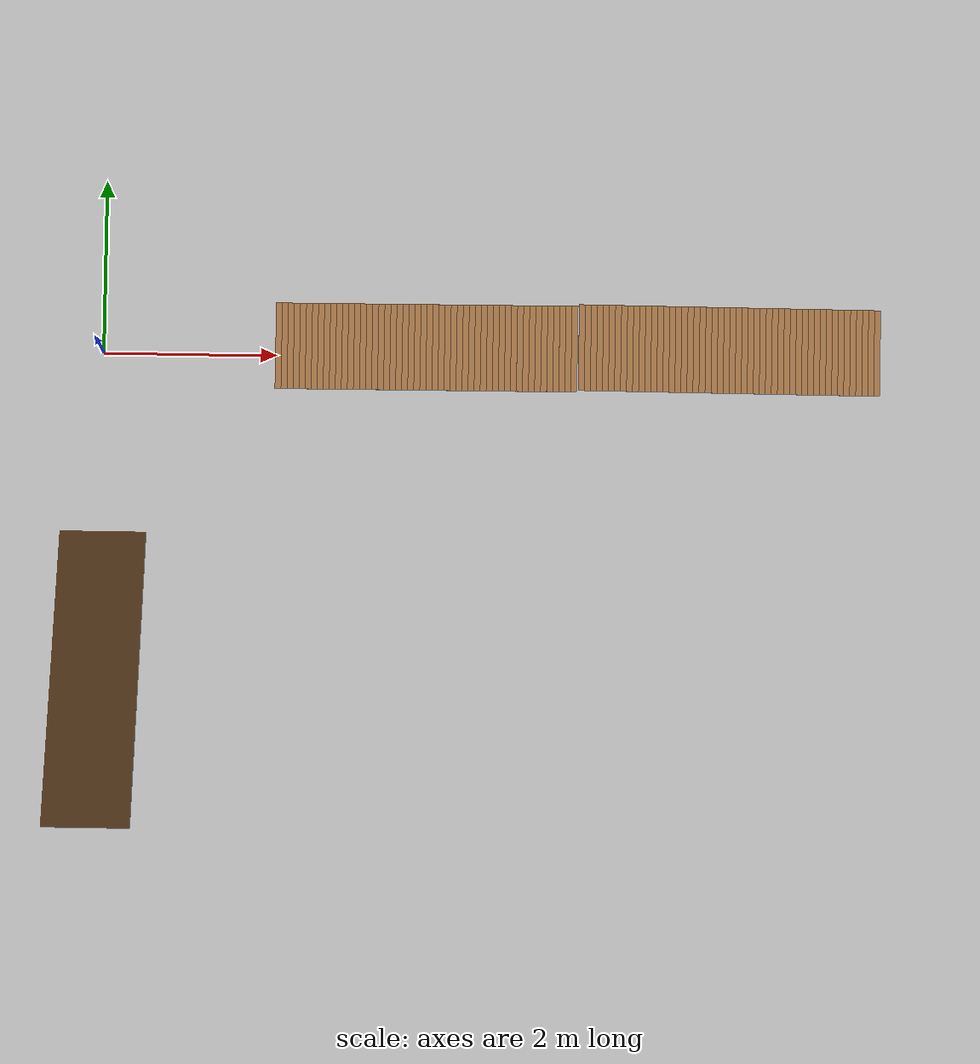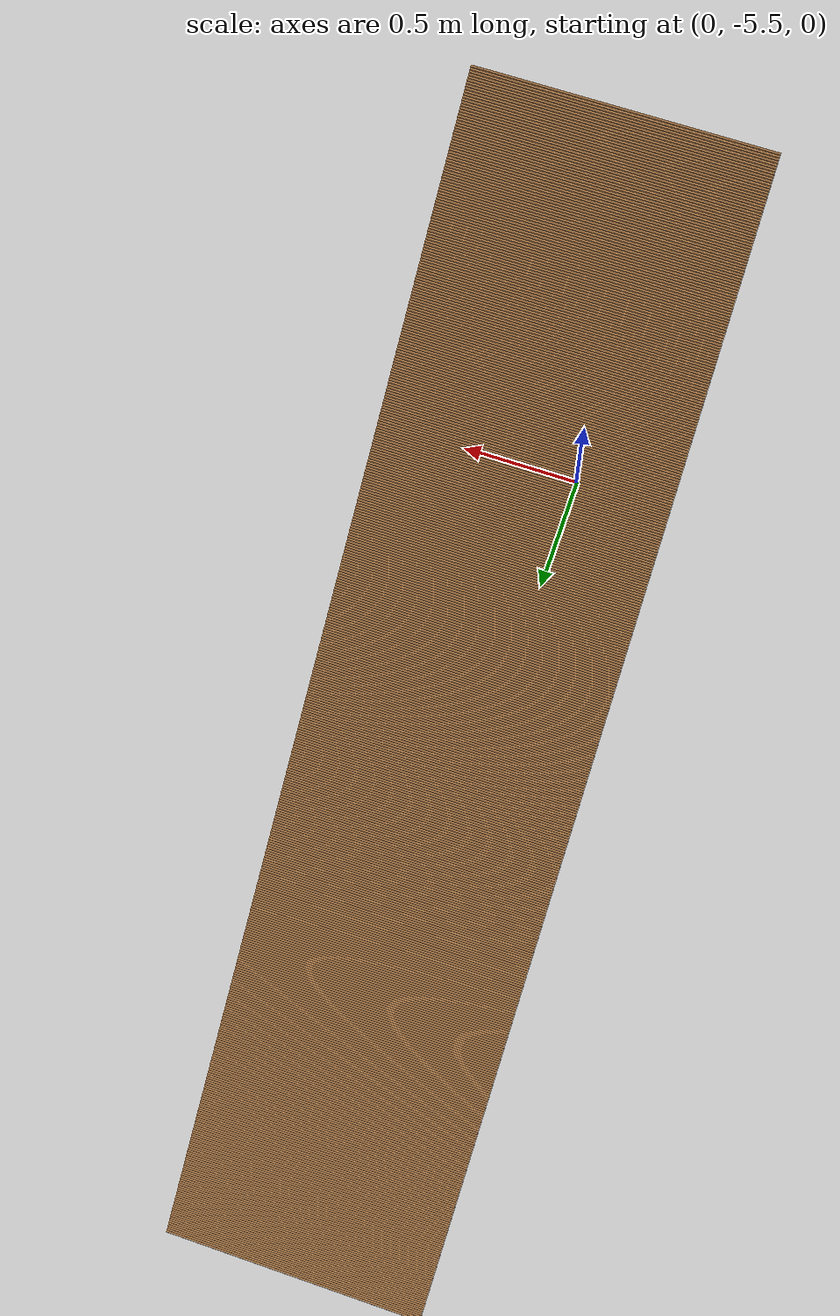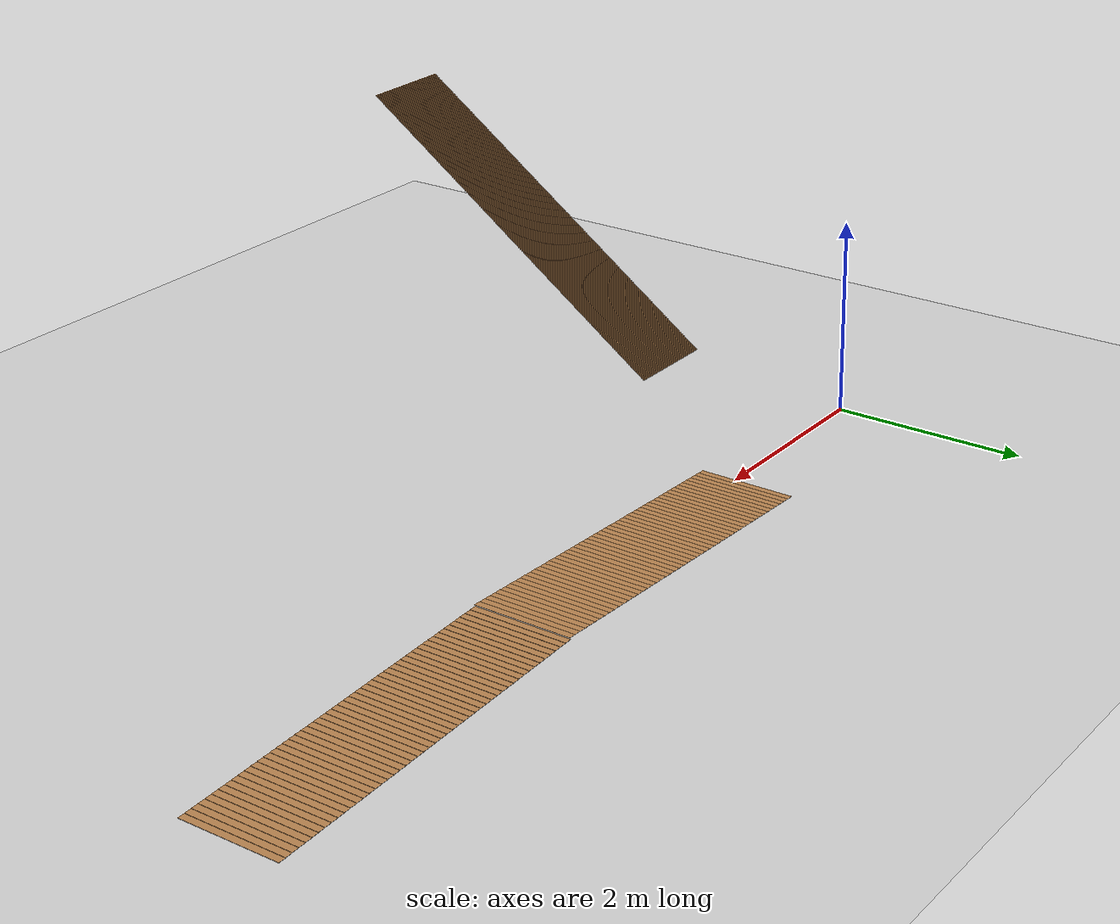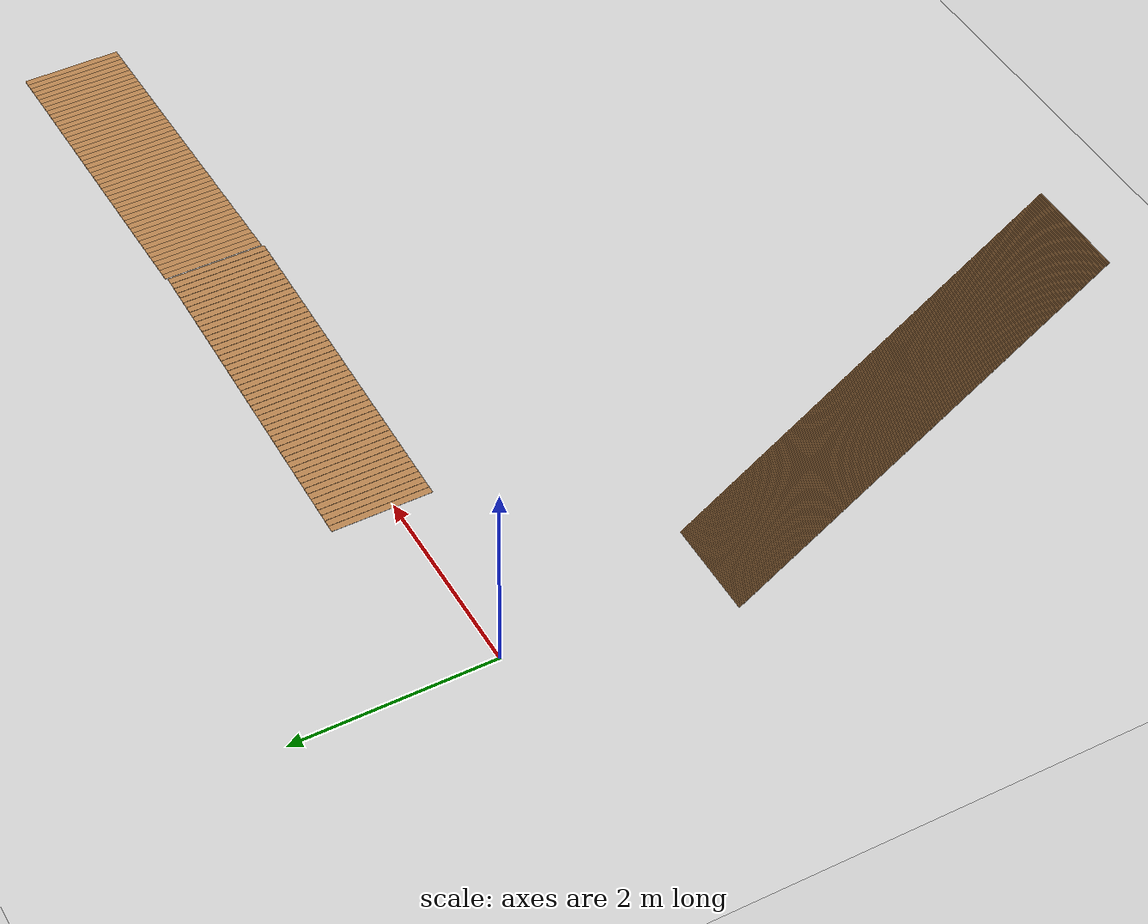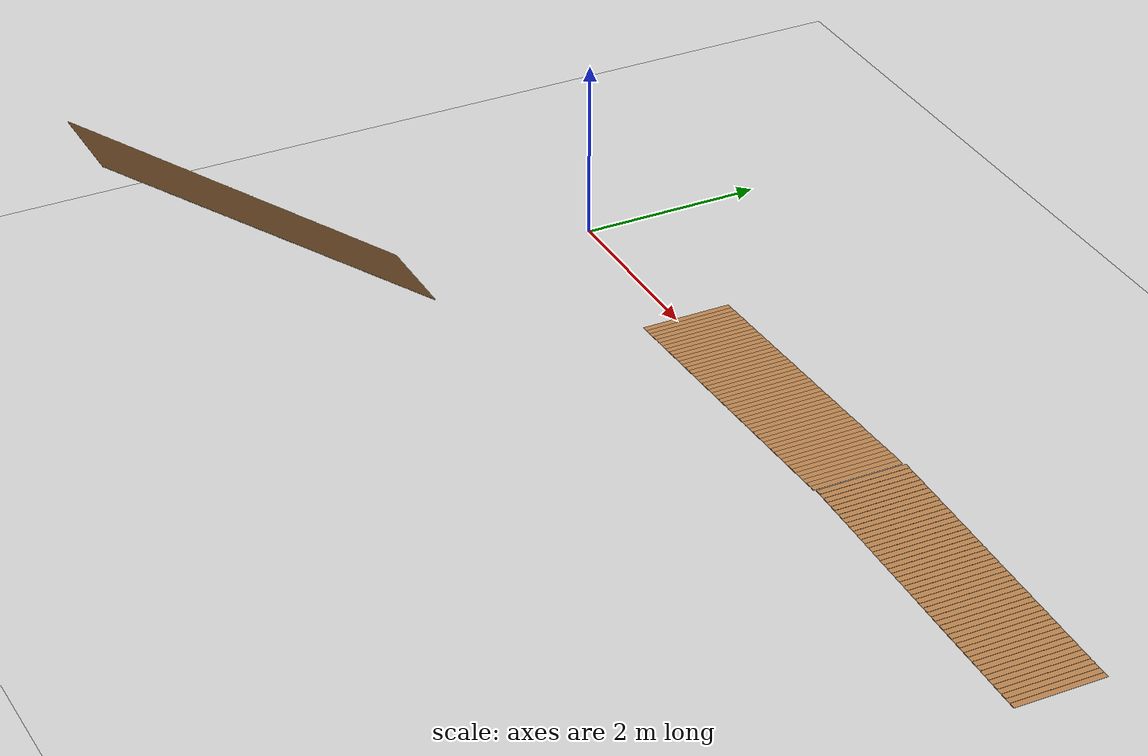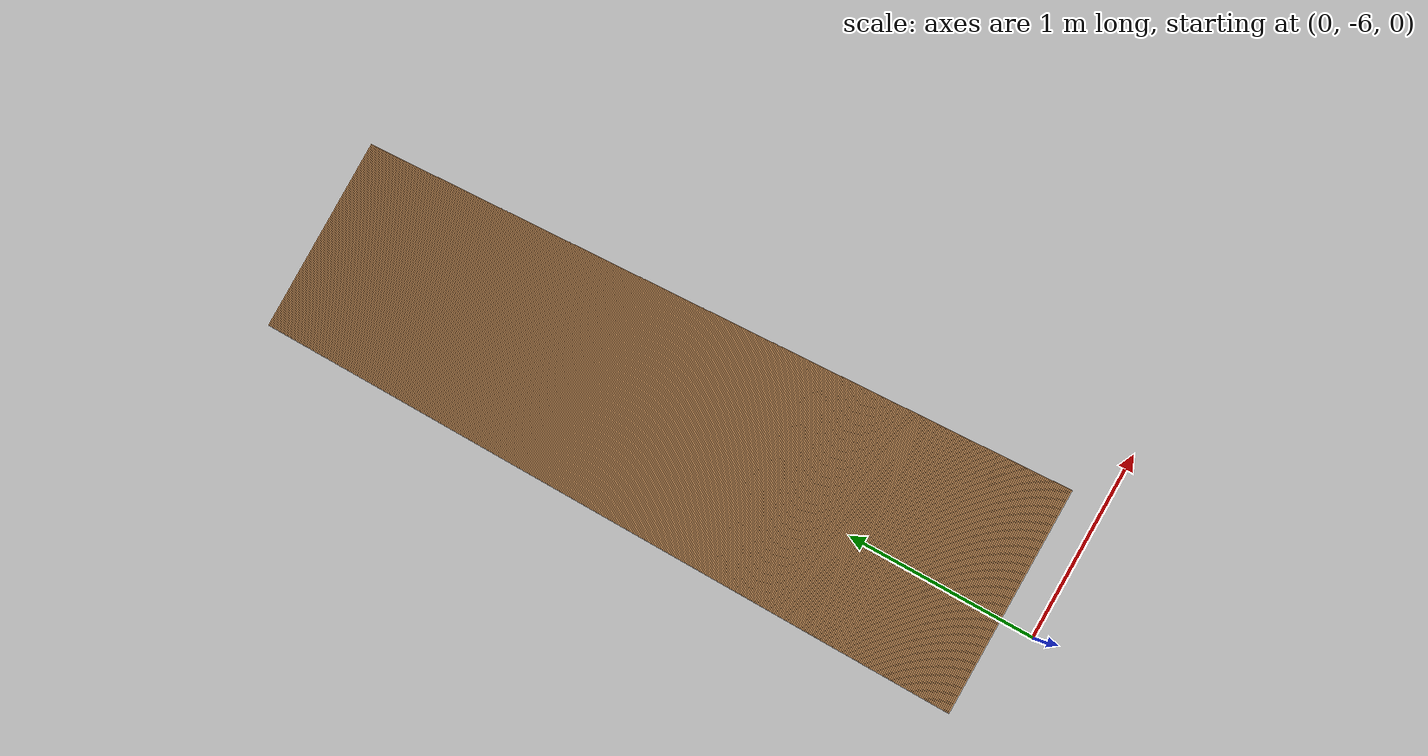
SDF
<sdf version="1.6">
 <world name="default">
  <light name="sun" type="directional">
   <pose>0 0 10 0 -0 0</pose>
   <diffuse>0.8 0.8 0.8 1</diffuse>
   <specular>0.2 0.2 0.2 1</specular>
   <attenuation>
    <range>1000</range>
    <constant>0.9</constant>
    <linear>0.01</linear>
    <quadratic>0.001</quadratic>
   </attenuation>
   <direction>-0.5 0.1 -0.9</direction>
  </light>
  <model name="ground_plane">
   <static>1</static>
   <link name="link">
    <collision name="collision">
     <geometry><plane><normal>0 0 1</normal><size>100 100</size></plane></geometry>
     <surface>
      <contact><collide_bitmask>65535</collide_bitmask></contact>
      <friction><ode><mu>100</mu><mu2>50</mu2></ode></friction>
     </surface>
    </collision>
    <visual name="visual">
     <cast_shadows>0</cast_shadows>
     <geometry><plane><normal>0 0 1</normal><size>100 100</size></plane></geometry>
     <material>
      <script><uri>file://media/materials/scripts/gazebo.material</uri><name>Gazebo/Grey</name></script>
     </material>
    </visual>
   </link>
  </model>
  <gravity>0 0 -9.8</gravity>
  <magnetic_field>6e-06 2.3e-05 -4.2e-05</magnetic_field>
  <atmosphere type="adiabatic"/>
  <physics name="default_physics" default="0" type="ode">
   <max_step_size>0.001</max_step_size>
   <real_time_factor>1</real_time_factor>
   <real_time_update_rate>1000</real_time_update_rate>
  </physics>
  <scene><ambient>0.4 0.4 0.4 1</ambient><background>0.7 0.7 0.7 1</background><shadows>1</shadows></scene>
  <audio><device>default</device></audio>
  <spherical_coordinates>
   <surface_model>EARTH_WGS84</surface_model>
   <latitude_deg>0</latitude_deg>
   <longitude_deg>0</longitude_deg>
   <elevation>0</elevation>
   <heading_deg>0</heading_deg>
  </spherical_coordinates>
  <model name="lamp">
   <pose>5.48739 0.130038 0 0 -0 0</pose>
   <link name="Stairs_1">
    <visual name="Stairs_1_Visual_0">
     <pose>-3.47239 -0.010038 0.0015 0 -0 1.5708</pose>
     <geometry><box><size>1 0.07 0.003</size></box></geometry>
     <material>
      <script><uri>file://media/materials/scripts/gazebo.material</uri><name>Gazebo/Wood</name></script>
      <ambient>1 1 1 1</ambient>
     </material>
     <meta><layer>0</layer></meta>
    </visual>
    <collision name="Stairs_1_Collision_0">
     <geometry><box><size>1 0.07 0.003</size></box></geometry>
     <pose>-3.47239 -0.010038 0.0015 0 -0 1.5708</pose>
    </collision>
    <visual name="Stairs_1_Visual_1">
     <pose>-3.40239 -0.010038 0.0045 0 -0 1.5708</pose>
     <geometry><box><size>1 0.07 0.003</size></box></geometry>
     <material>
      <script><uri>file://media/materials/scripts/gazebo.material</uri><name>Gazebo/Wood</name></script>
      <ambient>1 1 1 1</ambient>
     </material>
     <meta><layer>0</layer></meta>
    </visual>
    <collision name="Stairs_1_Collision_1">
     <geometry><box><size>1 0.07 0.003</size></box></geometry>
     <pose>-3.40239 -0.010038 0.0045 0 -0 1.5708</pose>
    </collision>
    <visual name="Stairs_1_Visual_2">
     <pose>-3.33239 -0.010038 0.0075 0 -0 1.5708</pose>
     <geometry><box><size>1 0.07 0.003</size></box></geometry>
     <material>
      <script><uri>file://media/materials/scripts/gazebo.material</uri><name>Gazebo/Wood</name></script>
      <ambient>1 1 1 1</ambient>
     </material>
     <meta><layer>0</layer></meta>
    </visual>
    <collision name="Stairs_1_Collision_2">
     <geometry><box><size>1 0.07 0.003</size></box></geometry>
     <pose>-3.33239 -0.010038 0.0075 0 -0 1.5708</pose>
    </collision>
    <visual name="Stairs_1_Visual_3">
     <pose>-3.26239 -0.010038 0.0105 0 -0 1.5708</pose>
     <geometry><box><size>1 0.07 0.003</size></box></geometry>
     <material>
      <script><uri>file://media/materials/scripts/gazebo.material</uri><name>Gazebo/Wood</name></script>
      <ambient>1 1 1 1</ambient>
     </material>
     <meta><layer>0</layer></meta>
    </visual>
    <collision name="Stairs_1_Collision_3">
     <geometry><box><size>1 0.07 0.003</size></box></geometry>
     <pose>-3.26239 -0.010038 0.0105 0 -0 1.5708</pose>
    </collision>
    <visual name="Stairs_1_Visual_4">
     <pose>-3.19239 -0.010038 0.0135 0 -0 1.5708</pose>
     <geometry><box><size>1 0.07 0.003</size></box></geometry>
     <material>
      <script><uri>file://media/materials/scripts/gazebo.material</uri><name>Gazebo/Wood</name></script>
      <ambient>1 1 1 1</ambient>
     </material>
     <meta><layer>0</layer></meta>
    </visual>
    <collision name="Stairs_1_Collision_4">
     <geometry><box><size>1 0.07 0.003</size></box></geometry>
     <pose>-3.19239 -0.010038 0.0135 0 -0 1.5708</pose>
    </collision>
    <visual name="Stairs_1_Visual_5">
     <pose>-3.12239 -0.010038 0.0165 0 -0 1.5708</pose>
     <geometry><box><size>1 0.07 0.003</size></box></geometry>
     <material>
      <script><uri>file://media/materials/scripts/gazebo.material</uri><name>Gazebo/Wood</name></script>
      <ambient>1 1 1 1</ambient>
     </material>
     <meta><layer>0</layer></meta>
    </visual>
    <collision name="Stairs_1_Collision_5">
     <geometry><box><size>1 0.07 0.003</size></box></geometry>
     <pose>-3.12239 -0.010038 0.0165 0 -0 1.5708</pose>
    </collision>
    <visual name="Stairs_1_Visual_6">
     <pose>-3.05239 -0.010038 0.0195 0 -0 1.5708</pose>
     <geometry><box><size>1 0.07 0.003</size></box></geometry>
     <material>
      <script><uri>file://media/materials/scripts/gazebo.material</uri><name>Gazebo/Wood</name></script>
      <ambient>1 1 1 1</ambient>
     </material>
     <meta><layer>0</layer></meta>
    </visual>
    <collision name="Stairs_1_Collision_6">
     <geometry><box><size>1 0.07 0.003</size></box></geometry>
     <pose>-3.05239 -0.010038 0.0195 0 -0 1.5708</pose>
    </collision>
    <visual name="Stairs_1_Visual_7">
     <pose>-2.98239 -0.010038 0.0225 0 -0 1.5708</pose>
     <geometry><box><size>1 0.07 0.003</size></box></geometry>
     <material>
      <script><uri>file://media/materials/scripts/gazebo.material</uri><name>Gazebo/Wood</name></script>
      <ambient>1 1 1 1</ambient>
     </material>
     <meta><layer>0</layer></meta>
    </visual>
    <collision name="Stairs_1_Collision_7">
     <geometry><box><size>1 0.07 0.003</size></box></geometry>
     <pose>-2.98239 -0.010038 0.0225 0 -0 1.5708</pose>
    </collision>
    <visual name="Stairs_1_Visual_8">
     <pose>-2.91239 -0.010038 0.0255 0 -0 1.5708</pose>
     <geometry><box><size>1 0.07 0.003</size></box></geometry>
     <material>
      <script><uri>file://media/materials/scripts/gazebo.material</uri><name>Gazebo/Wood</name></script>
      <ambient>1 1 1 1</ambient>
     </material>
     <meta><layer>0</layer></meta>
    </visual>
    <collision name="Stairs_1_Collision_8">
     <geometry><box><size>1 0.07 0.003</size></box></geometry>
     <pose>-2.91239 -0.010038 0.0255 0 -0 1.5708</pose>
    </collision>
    <visual name="Stairs_1_Visual_9">
     <pose>-2.84239 -0.010038 0.0285 0 -0 1.5708</pose>
     <geometry><box><size>1 0.07 0.003</size></box></geometry>
     <material>
      <script><uri>file://media/materials/scripts/gazebo.material</uri><name>Gazebo/Wood</name></script>
      <ambient>1 1 1 1</ambient>
     </material>
     <meta><layer>0</layer></meta>
    </visual>
    <collision name="Stairs_1_Collision_9">
     <geometry><box><size>1 0.07 0.003</size></box></geometry>
     <pose>-2.84239 -0.010038 0.0285 0 -0 1.5708</pose>
    </collision>
    <visual name="Stairs_1_Visual_10">
     <pose>-2.77239 -0.010038 0.0315 0 -0 1.5708</pose>
     <geometry><box><size>1 0.07 0.003</size></box></geometry>
     <material>
      <script><uri>file://media/materials/scripts/gazebo.material</uri><name>Gazebo/Wood</name></script>
      <ambient>1 1 1 1</ambient>
     </material>
     <meta><layer>0</layer></meta>
    </visual>
    <collision name="Stairs_1_Collision_10">
     <geometry><box><size>1 0.07 0.003</size></box></geometry>
     <pose>-2.77239 -0.010038 0.0315 0 -0 1.5708</pose>
    </collision>
    <visual name="Stairs_1_Visual_11">
     <pose>-2.70239 -0.010038 0.0345 0 -0 1.5708</pose>
     <geometry><box><size>1 0.07 0.003</size></box></geometry>
     <material>
      <script><uri>file://media/materials/scripts/gazebo.material</uri><name>Gazebo/Wood</name></script>
      <ambient>1 1 1 1</ambient>
     </material>
     <meta><layer>0</layer></meta>
    </visual>
    <collision name="Stairs_1_Collision_11">
     <geometry><box><size>1 0.07 0.003</size></box></geometry>
     <pose>-2.70239 -0.010038 0.0345 0 -0 1.5708</pose>
    </collision>
    <visual name="Stairs_1_Visual_12">
     <pose>-2.63239 -0.010038 0.0375 0 -0 1.5708</pose>
     <geometry><box><size>1 0.07 0.003</size></box></geometry>
     <material>
      <script><uri>file://media/materials/scripts/gazebo.material</uri><name>Gazebo/Wood</name></script>
      <ambient>1 1 1 1</ambient>
     </material>
     <meta><layer>0</layer></meta>
    </visual>
    <collision name="Stairs_1_Collision_12">
     <geometry><box><size>1 0.07 0.003</size></box></geometry>
     <pose>-2.63239 -0.010038 0.0375 0 -0 1.5708</pose>
    </collision>
    <visual name="Stairs_1_Visual_13">
     <pose>-2.56239 -0.010038 0.0405 0 -0 1.5708</pose>
     <geometry><box><size>1 0.07 0.003</size></box></geometry>
     <material>
      <script><uri>file://media/materials/scripts/gazebo.material</uri><name>Gazebo/Wood</name></script>
      <ambient>1 1 1 1</ambient>
     </material>
     <meta><layer>0</layer></meta>
    </visual>
    <collision name="Stairs_1_Collision_13">
     <geometry><box><size>1 0.07 0.003</size></box></geometry>
     <pose>-2.56239 -0.010038 0.0405 0 -0 1.5708</pose>
    </collision>
    <visual name="Stairs_1_Visual_14">
     <pose>-2.49239 -0.010038 0.0435 0 -0 1.5708</pose>
     <geometry><box><size>1 0.07 0.003</size></box></geometry>
     <material>
      <script><uri>file://media/materials/scripts/gazebo.material</uri><name>Gazebo/Wood</name></script>
      <ambient>1 1 1 1</ambient>
     </material>
     <meta><layer>0</layer></meta>
    </visual>
    <collision name="Stairs_1_Collision_14">
     <geometry><box><size>1 0.07 0.003</size></box></geometry>
     <pose>-2.49239 -0.010038 0.0435 0 -0 1.5708</pose>
    </collision>
    <visual name="Stairs_1_Visual_15">
     <pose>-2.42239 -0.010038 0.0465 0 -0 1.5708</pose>
     <geometry><box><size>1 0.07 0.003</size></box></geometry>
     <material>
      <script><uri>file://media/materials/scripts/gazebo.material</uri><name>Gazebo/Wood</name></script>
      <ambient>1 1 1 1</ambient>
     </material>
     <meta><layer>0</layer></meta>
    </visual>
    <collision name="Stairs_1_Collision_15">
     <geometry><box><size>1 0.07 0.003</size></box></geometry>
     <pose>-2.42239 -0.010038 0.0465 0 -0 1.5708</pose>
    </collision>
    <visual name="Stairs_1_Visual_16">
     <pose>-2.35239 -0.010038 0.0495 0 -0 1.5708</pose>
     <geometry><box><size>1 0.07 0.003</size></box></geometry>
     <material>
      <script><uri>file://media/materials/scripts/gazebo.material</uri><name>Gazebo/Wood</name></script>
      <ambient>1 1 1 1</ambient>
     </material>
     <meta><layer>0</layer></meta>
    </visual>
    <collision name="Stairs_1_Collision_16">
     <geometry><box><size>1 0.07 0.003</size></box></geometry>
     <pose>-2.35239 -0.010038 0.0495 0 -0 1.5708</pose>
    </collision>
    <visual name="Stairs_1_Visual_17">
     <pose>-2.28239 -0.010038 0.0525 0 -0 1.5708</pose>
     <geometry><box><size>1 0.07 0.003</size></box></geometry>
     <material>
      <script><uri>file://media/materials/scripts/gazebo.material</uri><name>Gazebo/Wood</name></script>
      <ambient>1 1 1 1</ambient>
     </material>
     <meta><layer>0</layer></meta>
    </visual>
    <collision name="Stairs_1_Collision_17">
     <geometry><box><size>1 0.07 0.003</size></box></geometry>
     <pose>-2.28239 -0.010038 0.0525 0 -0 1.5708</pose>
    </collision>
    <visual name="Stairs_1_Visual_18">
     <pose>-2.21239 -0.010038 0.0555 0 -0 1.5708</pose>
     <geometry><box><size>1 0.07 0.003</size></box></geometry>
     <material>
      <script><uri>file://media/materials/scripts/gazebo.material</uri><name>Gazebo/Wood</name></script>
      <ambient>1 1 1 1</ambient>
     </material>
     <meta><layer>0</layer></meta>
    </visual>
    <collision name="Stairs_1_Collision_18">
     <geometry><box><size>1 0.07 0.003</size></box></geometry>
     <pose>-2.21239 -0.010038 0.0555 0 -0 1.5708</pose>
    </collision>
    <visual name="Stairs_1_Visual_19">
     <pose>-2.14239 -0.010038 0.0585 0 -0 1.5708</pose>
     <geometry><box><size>1 0.07 0.003</size></box></geometry>
     <material>
      <script><uri>file://media/materials/scripts/gazebo.material</uri><name>Gazebo/Wood</name></script>
      <ambient>1 1 1 1</ambient>
     </material>
     <meta><layer>0</layer></meta>
    </visual>
    <collision name="Stairs_1_Collision_19">
     <geometry><box><size>1 0.07 0.003</size></box></geometry>
     <pose>-2.14239 -0.010038 0.0585 0 -0 1.5708</pose>
    </collision>
    <visual name="Stairs_1_Visual_20">
     <pose>-2.07239 -0.010038 0.0615 0 -0 1.5708</pose>
     <geometry><box><size>1 0.07 0.003</size></box></geometry>
     <material>
      <script><uri>file://media/materials/scripts/gazebo.material</uri><name>Gazebo/Wood</name></script>
      <ambient>1 1 1 1</ambient>
     </material>
     <meta><layer>0</layer></meta>
    </visual>
    <collision name="Stairs_1_Collision_20">
     <geometry><box><size>1 0.07 0.003</size></box></geometry>
     <pose>-2.07239 -0.010038 0.0615 0 -0 1.5708</pose>
    </collision>
    <visual name="Stairs_1_Visual_21">
     <pose>-2.00239 -0.010038 0.0645 0 -0 1.5708</pose>
     <geometry><box><size>1 0.07 0.003</size></box></geometry>
     <material>
      <script><uri>file://media/materials/scripts/gazebo.material</uri><name>Gazebo/Wood</name></script>
      <ambient>1 1 1 1</ambient>
     </material>
     <meta><layer>0</layer></meta>
    </visual>
    <collision name="Stairs_1_Collision_21">
     <geometry><box><size>1 0.07 0.003</size></box></geometry>
     <pose>-2.00239 -0.010038 0.0645 0 -0 1.5708</pose>
    </collision>
    <visual name="Stairs_1_Visual_22">
     <pose>-1.93239 -0.010038 0.0675 0 -0 1.5708</pose>
     <geometry><box><size>1 0.07 0.003</size></box></geometry>
     <material>
      <script><uri>file://media/materials/scripts/gazebo.material</uri><name>Gazebo/Wood</name></script>
      <ambient>1 1 1 1</ambient>
     </material>
     <meta><layer>0</layer></meta>
    </visual>
    <collision name="Stairs_1_Collision_22">
     <geometry><box><size>1 0.07 0.003</size></box></geometry>
     <pose>-1.93239 -0.010038 0.0675 0 -0 1.5708</pose>
    </collision>
    <visual name="Stairs_1_Visual_23">
     <pose>-1.86239 -0.010038 0.0705 0 -0 1.5708</pose>
     <geometry><box><size>1 0.07 0.003</size></box></geometry>
     <material>
      <script><uri>file://media/materials/scripts/gazebo.material</uri><name>Gazebo/Wood</name></script>
      <ambient>1 1 1 1</ambient>
     </material>
     <meta><layer>0</layer></meta>
    </visual>
    <collision name="Stairs_1_Collision_23">
     <geometry><box><size>1 0.07 0.003</size></box></geometry>
     <pose>-1.86239 -0.010038 0.0705 0 -0 1.5708</pose>
    </collision>
    <visual name="Stairs_1_Visual_24">
     <pose>-1.79239 -0.010038 0.0735 0 -0 1.5708</pose>
     <geometry><box><size>1 0.07 0.003</size></box></geometry>
     <material>
      <script><uri>file://media/materials/scripts/gazebo.material</uri><name>Gazebo/Wood</name></script>
      <ambient>1 1 1 1</ambient>
     </material>
     <meta><layer>0</layer></meta>
    </visual>
    <collision name="Stairs_1_Collision_24">
     <geometry><box><size>1 0.07 0.003</size></box></geometry>
     <pose>-1.79239 -0.010038 0.0735 0 -0 1.5708</pose>
    </collision>
    <visual name="Stairs_1_Visual_25">
     <pose>-1.72239 -0.010038 0.0765 0 -0 1.5708</pose>
     <geometry><box><size>1 0.07 0.003</size></box></geometry>
     <material>
      <script><uri>file://media/materials/scripts/gazebo.material</uri><name>Gazebo/Wood</name></script>
      <ambient>1 1 1 1</ambient>
     </material>
     <meta><layer>0</layer></meta>
    </visual>
    <collision name="Stairs_1_Collision_25">
     <geometry><box><size>1 0.07 0.003</size></box></geometry>
     <pose>-1.72239 -0.010038 0.0765 0 -0 1.5708</pose>
    </collision>
    <visual name="Stairs_1_Visual_26">
     <pose>-1.65239 -0.010038 0.0795 0 -0 1.5708</pose>
     <geometry><box><size>1 0.07 0.003</size></box></geometry>
     <material>
      <script><uri>file://media/materials/scripts/gazebo.material</uri><name>Gazebo/Wood</name></script>
      <ambient>1 1 1 1</ambient>
     </material>
     <meta><layer>0</layer></meta>
    </visual>
    <collision name="Stairs_1_Collision_26">
     <geometry><box><size>1 0.07 0.003</size></box></geometry>
     <pose>-1.65239 -0.010038 0.0795 0 -0 1.5708</pose>
    </collision>
    <visual name="Stairs_1_Visual_27">
     <pose>-1.58239 -0.010038 0.0825 0 -0 1.5708</pose>
     <geometry><box><size>1 0.07 0.003</size></box></geometry>
     <material>
      <script><uri>file://media/materials/scripts/gazebo.material</uri><name>Gazebo/Wood</name></script>
      <ambient>1 1 1 1</ambient>
     </material>
     <meta><layer>0</layer></meta>
    </visual>
    <collision name="Stairs_1_Collision_27">
     <geometry><box><size>1 0.07 0.003</size></box></geometry>
     <pose>-1.58239 -0.010038 0.0825 0 -0 1.5708</pose>
    </collision>
    <visual name="Stairs_1_Visual_28">
     <pose>-1.51239 -0.010037 0.0855 0 -0 1.5708</pose>
     <geometry><box><size>1 0.07 0.003</size></box></geometry>
     <material>
      <script><uri>file://media/materials/scripts/gazebo.material</uri><name>Gazebo/Wood</name></script>
      <ambient>1 1 1 1</ambient>
     </material>
     <meta><layer>0</layer></meta>
    </visual>
    <collision name="Stairs_1_Collision_28">
     <geometry><box><size>1 0.07 0.003</size></box></geometry>
     <pose>-1.51239 -0.010037 0.0855 0 -0 1.5708</pose>
    </collision>
    <visual name="Stairs_1_Visual_29">
     <pose>-1.44239 -0.010037 0.0885 0 -0 1.5708</pose>
     <geometry><box><size>1 0.07 0.003</size></box></geometry>
     <material>
      <script><uri>file://media/materials/scripts/gazebo.material</uri><name>Gazebo/Wood</name></script>
      <ambient>1 1 1 1</ambient>
     </material>
     <meta><layer>0</layer></meta>
    </visual>
    <collision name="Stairs_1_Collision_29">
     <geometry><box><size>1 0.07 0.003</size></box></geometry>
     <pose>-1.44239 -0.010037 0.0885 0 -0 1.5708</pose>
    </collision>
    <visual name="Stairs_1_Visual_30">
     <pose>-1.37239 -0.010037 0.0915 0 -0 1.5708</pose>
     <geometry><box><size>1 0.07 0.003</size></box></geometry>
     <material>
      <script><uri>file://media/materials/scripts/gazebo.material</uri><name>Gazebo/Wood</name></script>
      <ambient>1 1 1 1</ambient>
     </material>
     <meta><layer>0</layer></meta>
    </visual>
    <collision name="Stairs_1_Collision_30">
     <geometry><box><size>1 0.07 0.003</size></box></geometry>
     <pose>-1.37239 -0.010037 0.0915 0 -0 1.5708</pose>
    </collision>
    <visual name="Stairs_1_Visual_31">
     <pose>-1.30239 -0.010037 0.0945 0 -0 1.5708</pose>
     <geometry><box><size>1 0.07 0.003</size></box></geometry>
     <material>
      <script><uri>file://media/materials/scripts/gazebo.material</uri><name>Gazebo/Wood</name></script>
      <ambient>1 1 1 1</ambient>
     </material>
     <meta><layer>0</layer></meta>
    </visual>
    <collision name="Stairs_1_Collision_31">
     <geometry><box><size>1 0.07 0.003</size></box></geometry>
     <pose>-1.30239 -0.010037 0.0945 0 -0 1.5708</pose>
    </collision>
    <visual name="Stairs_1_Visual_32">
     <pose>-1.23239 -0.010037 0.0975 0 -0 1.5708</pose>
     <geometry><box><size>1 0.07 0.003</size></box></geometry>
     <material>
      <script><uri>file://media/materials/scripts/gazebo.material</uri><name>Gazebo/Wood</name></script>
      <ambient>1 1 1 1</ambient>
     </material>
     <meta><layer>0</layer></meta>
    </visual>
    <collision name="Stairs_1_Collision_32">
     <geometry><box><size>1 0.07 0.003</size></box></geometry>
     <pose>-1.23239 -0.010037 0.0975 0 -0 1.5708</pose>
    </collision>
    <visual name="Stairs_1_Visual_33">
     <pose>-1.16239 -0.010037 0.1005 0 -0 1.5708</pose>
     <geometry><box><size>1 0.07 0.003</size></box></geometry>
     <material>
      <script><uri>file://media/materials/scripts/gazebo.material</uri><name>Gazebo/Wood</name></script>
      <ambient>1 1 1 1</ambient>
     </material>
     <meta><layer>0</layer></meta>
    </visual>
    <collision name="Stairs_1_Collision_33">
     <geometry><box><size>1 0.07 0.003</size></box></geometry>
     <pose>-1.16239 -0.010037 0.1005 0 -0 1.5708</pose>
    </collision>
    <visual name="Stairs_1_Visual_34">
     <pose>-1.09239 -0.010037 0.1035 0 -0 1.5708</pose>
     <geometry><box><size>1 0.07 0.003</size></box></geometry>
     <material>
      <script><uri>file://media/materials/scripts/gazebo.material</uri><name>Gazebo/Wood</name></script>
      <ambient>1 1 1 1</ambient>
     </material>
     <meta><layer>0</layer></meta>
    </visual>
    <collision name="Stairs_1_Collision_34">
     <geometry><box><size>1 0.07 0.003</size></box></geometry>
     <pose>-1.09239 -0.010037 0.1035 0 -0 1.5708</pose>
    </collision>
    <visual name="Stairs_1_Visual_35">
     <pose>-1.02239 -0.010037 0.1065 0 -0 1.5708</pose>
     <geometry><box><size>1 0.07 0.003</size></box></geometry>
     <material>
      <script><uri>file://media/materials/scripts/gazebo.material</uri><name>Gazebo/Wood</name></script>
      <ambient>1 1 1 1</ambient>
     </material>
     <meta><layer>0</layer></meta>
    </visual>
    <collision name="Stairs_1_Collision_35">
     <geometry><box><size>1 0.07 0.003</size></box></geometry>
     <pose>-1.02239 -0.010037 0.1065 0 -0 1.5708</pose>
    </collision>
    <visual name="Stairs_1_Visual_36">
     <pose>-0.952387 -0.010037 0.1095 0 -0 1.5708</pose>
     <geometry><box><size>1 0.07 0.003</size></box></geometry>
     <material>
      <script><uri>file://media/materials/scripts/gazebo.material</uri><name>Gazebo/Wood</name></script>
      <ambient>1 1 1 1</ambient>
     </material>
     <meta><layer>0</layer></meta>
    </visual>
    <collision name="Stairs_1_Collision_36">
     <geometry><box><size>1 0.07 0.003</size></box></geometry>
     <pose>-0.952387 -0.010037 0.1095 0 -0 1.5708</pose>
    </collision>
    <visual name="Stairs_1_Visual_37">
     <pose>-0.882387 -0.010037 0.1125 0 -0 1.5708</pose>
     <geometry><box><size>1 0.07 0.003</size></box></geometry>
     <material>
      <script><uri>file://media/materials/scripts/gazebo.material</uri><name>Gazebo/Wood</name></script>
      <ambient>1 1 1 1</ambient>
     </material>
     <meta><layer>0</layer></meta>
    </visual>
    <collision name="Stairs_1_Collision_37">
     <geometry><box><size>1 0.07 0.003</size></box></geometry>
     <pose>-0.882387 -0.010037 0.1125 0 -0 1.5708</pose>
    </collision>
    <visual name="Stairs_1_Visual_38">
     <pose>-0.812387 -0.010037 0.1155 0 -0 1.5708</pose>
     <geometry><box><size>1 0.07 0.003</size></box></geometry>
     <material>
      <script><uri>file://media/materials/scripts/gazebo.material</uri><name>Gazebo/Wood</name></script>
      <ambient>1 1 1 1</ambient>
     </material>
     <meta><layer>0</layer></meta>
    </visual>
    <collision name="Stairs_1_Collision_38">
     <geometry><box><size>1 0.07 0.003</size></box></geometry>
     <pose>-0.812387 -0.010037 0.1155 0 -0 1.5708</pose>
    </collision>
    <visual name="Stairs_1_Visual_39">
     <pose>-0.742387 -0.010037 0.1185 0 -0 1.5708</pose>
     <geometry><box><size>1 0.07 0.003</size></box></geometry>
     <material>
      <script><uri>file://media/materials/scripts/gazebo.material</uri><name>Gazebo/Wood</name></script>
      <ambient>1 1 1 1</ambient>
     </material>
     <meta><layer>0</layer></meta>
    </visual>
    <collision name="Stairs_1_Collision_39">
     <geometry><box><size>1 0.07 0.003</size></box></geometry>
     <pose>-0.742387 -0.010037 0.1185 0 -0 1.5708</pose>
    </collision>
    <visual name="Stairs_1_Visual_40">
     <pose>-0.672387 -0.010037 0.1215 0 -0 1.5708</pose>
     <geometry><box><size>1 0.07 0.003</size></box></geometry>
     <material>
      <script><uri>file://media/materials/scripts/gazebo.material</uri><name>Gazebo/Wood</name></script>
      <ambient>1 1 1 1</ambient>
     </material>
     <meta><layer>0</layer></meta>
    </visual>
    <collision name="Stairs_1_Collision_40">
     <geometry><box><size>1 0.07 0.003</size></box></geometry>
     <pose>-0.672387 -0.010037 0.1215 0 -0 1.5708</pose>
    </collision>
    <visual name="Stairs_1_Visual_41">
     <pose>-0.602387 -0.010037 0.1245 0 -0 1.5708</pose>
     <geometry><box><size>1 0.07 0.003</size></box></geometry>
     <material>
      <script><uri>file://media/materials/scripts/gazebo.material</uri><name>Gazebo/Wood</name></script>
      <ambient>1 1 1 1</ambient>
     </material>
     <meta><layer>0</layer></meta>
    </visual>
    <collision name="Stairs_1_Collision_41">
     <geometry><box><size>1 0.07 0.003</size></box></geometry>
     <pose>-0.602387 -0.010037 0.1245 0 -0 1.5708</pose>
    </collision>
    <visual name="Stairs_1_Visual_42">
     <pose>-0.532387 -0.010037 0.1275 0 -0 1.5708</pose>
     <geometry><box><size>1 0.07 0.003</size></box></geometry>
     <material>
      <script><uri>file://media/materials/scripts/gazebo.material</uri><name>Gazebo/Wood</name></script>
      <ambient>1 1 1 1</ambient>
     </material>
     <meta><layer>0</layer></meta>
    </visual>
    <collision name="Stairs_1_Collision_42">
     <geometry><box><size>1 0.07 0.003</size></box></geometry>
     <pose>-0.532387 -0.010037 0.1275 0 -0 1.5708</pose>
    </collision>
    <visual name="Stairs_1_Visual_43">
     <pose>-0.462387 -0.010037 0.1305 0 -0 1.5708</pose>
     <geometry><box><size>1 0.07 0.003</size></box></geometry>
     <material>
      <script><uri>file://media/materials/scripts/gazebo.material</uri><name>Gazebo/Wood</name></script>
      <ambient>1 1 1 1</ambient>
     </material>
     <meta><layer>0</layer></meta>
    </visual>
    <collision name="Stairs_1_Collision_43">
     <geometry><box><size>1 0.07 0.003</size></box></geometry>
     <pose>-0.462387 -0.010037 0.1305 0 -0 1.5708</pose>
    </collision>
    <visual name="Stairs_1_Visual_44">
     <pose>-0.392387 -0.010037 0.1335 0 -0 1.5708</pose>
     <geometry><box><size>1 0.07 0.003</size></box></geometry>
     <material>
      <script><uri>file://media/materials/scripts/gazebo.material</uri><name>Gazebo/Wood</name></script>
      <ambient>1 1 1 1</ambient>
     </material>
     <meta><layer>0</layer></meta>
    </visual>
    <collision name="Stairs_1_Collision_44">
     <geometry><box><size>1 0.07 0.003</size></box></geometry>
     <pose>-0.392387 -0.010037 0.1335 0 -0 1.5708</pose>
    </collision>
    <visual name="Stairs_1_Visual_45">
     <pose>-0.322387 -0.010037 0.1365 0 -0 1.5708</pose>
     <geometry><box><size>1 0.07 0.003</size></box></geometry>
     <material>
      <script><uri>file://media/materials/scripts/gazebo.material</uri><name>Gazebo/Wood</name></script>
      <ambient>1 1 1 1</ambient>
     </material>
     <meta><layer>0</layer></meta>
    </visual>
    <collision name="Stairs_1_Collision_45">
     <geometry><box><size>1 0.07 0.003</size></box></geometry>
     <pose>-0.322387 -0.010037 0.1365 0 -0 1.5708</pose>
    </collision>
    <visual name="Stairs_1_Visual_46">
     <pose>-0.252387 -0.010037 0.1395 0 -0 1.5708</pose>
     <geometry><box><size>1 0.07 0.003</size></box></geometry>
     <material>
      <script><uri>file://media/materials/scripts/gazebo.material</uri><name>Gazebo/Wood</name></script>
      <ambient>1 1 1 1</ambient>
     </material>
     <meta><layer>0</layer></meta>
    </visual>
    <collision name="Stairs_1_Collision_46">
     <geometry><box><size>1 0.07 0.003</size></box></geometry>
     <pose>-0.252387 -0.010037 0.1395 0 -0 1.5708</pose>
    </collision>
    <visual name="Stairs_1_Visual_47">
     <pose>-0.182387 -0.010037 0.1425 0 -0 1.5708</pose>
     <geometry><box><size>1 0.07 0.003</size></box></geometry>
     <material>
      <script><uri>file://media/materials/scripts/gazebo.material</uri><name>Gazebo/Wood</name></script>
      <ambient>1 1 1 1</ambient>
     </material>
     <meta><layer>0</layer></meta>
    </visual>
    <collision name="Stairs_1_Collision_47">
     <geometry><box><size>1 0.07 0.003</size></box></geometry>
     <pose>-0.182387 -0.010037 0.1425 0 -0 1.5708</pose>
    </collision>
    <visual name="Stairs_1_Visual_48">
     <pose>-0.112387 -0.010037 0.1455 0 -0 1.5708</pose>
     <geometry><box><size>1 0.07 0.003</size></box></geometry>
     <material>
      <script><uri>file://media/materials/scripts/gazebo.material</uri><name>Gazebo/Wood</name></script>
      <ambient>1 1 1 1</ambient>
     </material>
     <meta><layer>0</layer></meta>
    </visual>
    <collision name="Stairs_1_Collision_48">
     <geometry><box><size>1 0.07 0.003</size></box></geometry>
     <pose>-0.112387 -0.010037 0.1455 0 -0 1.5708</pose>
    </collision>
    <visual name="Stairs_1_Visual_49">
     <pose>-0.042387 -0.010037 0.1485 0 -0 1.5708</pose>
     <geometry><box><size>1 0.07 0.003</size></box></geometry>
     <material>
      <script><uri>file://media/materials/scripts/gazebo.material</uri><name>Gazebo/Wood</name></script>
      <ambient>1 1 1 1</ambient>
     </material>
     <meta><layer>0</layer></meta>
    </visual>
    <collision name="Stairs_1_Collision_49">
     <geometry><box><size>1 0.07 0.003</size></box></geometry>
     <pose>-0.042387 -0.010037 0.1485 0 -0 1.5708</pose>
    </collision>
   </link>
   <link name="Stairs_3">
    <visual name="Stairs_3_Visual_0">
     <pose>3.47239 0.010037 0.0015 0 0 -1.5708</pose>
     <geometry><box><size>1 0.07 0.003</size></box></geometry>
     <material>
      <script><uri>file://media/materials/scripts/gazebo.material</uri><name>Gazebo/Wood</name></script>
      <ambient>1 1 1 1</ambient>
     </material>
     <meta><layer>0</layer></meta>
    </visual>
    <collision name="Stairs_3_Collision_0">
     <geometry><box><size>1 0.07 0.003</size></box></geometry>
     <pose>3.47239 0.010037 0.0015 0 0 -1.5708</pose>
    </collision>
    <visual name="Stairs_3_Visual_1">
     <pose>3.40239 0.010037 0.0045 0 0 -1.5708</pose>
     <geometry><box><size>1 0.07 0.003</size></box></geometry>
     <material>
      <script><uri>file://media/materials/scripts/gazebo.material</uri><name>Gazebo/Wood</name></script>
      <ambient>1 1 1 1</ambient>
     </material>
     <meta><layer>0</layer></meta>
    </visual>
    <collision name="Stairs_3_Collision_1">
     <geometry><box><size>1 0.07 0.003</size></box></geometry>
     <pose>3.40239 0.010037 0.0045 0 0 -1.5708</pose>
    </collision>
    <visual name="Stairs_3_Visual_2">
     <pose>3.33239 0.010037 0.0075 0 0 -1.5708</pose>
     <geometry><box><size>1 0.07 0.003</size></box></geometry>
     <material>
      <script><uri>file://media/materials/scripts/gazebo.material</uri><name>Gazebo/Wood</name></script>
      <ambient>1 1 1 1</ambient>
     </material>
     <meta><layer>0</layer></meta>
    </visual>
    <collision name="Stairs_3_Collision_2">
     <geometry><box><size>1 0.07 0.003</size></box></geometry>
     <pose>3.33239 0.010037 0.0075 0 0 -1.5708</pose>
    </collision>
    <visual name="Stairs_3_Visual_3">
     <pose>3.26239 0.010037 0.0105 0 0 -1.5708</pose>
     <geometry><box><size>1 0.07 0.003</size></box></geometry>
     <material>
      <script><uri>file://media/materials/scripts/gazebo.material</uri><name>Gazebo/Wood</name></script>
      <ambient>1 1 1 1</ambient>
     </material>
     <meta><layer>0</layer></meta>
    </visual>
    <collision name="Stairs_3_Collision_3">
     <geometry><box><size>1 0.07 0.003</size></box></geometry>
     <pose>3.26239 0.010037 0.0105 0 0 -1.5708</pose>
    </collision>
    <visual name="Stairs_3_Visual_4">
     <pose>3.19239 0.010037 0.0135 0 0 -1.5708</pose>
     <geometry><box><size>1 0.07 0.003</size></box></geometry>
     <material>
      <script><uri>file://media/materials/scripts/gazebo.material</uri><name>Gazebo/Wood</name></script>
      <ambient>1 1 1 1</ambient>
     </material>
     <meta><layer>0</layer></meta>
    </visual>
    <collision name="Stairs_3_Collision_4">
     <geometry><box><size>1 0.07 0.003</size></box></geometry>
     <pose>3.19239 0.010037 0.0135 0 0 -1.5708</pose>
    </collision>
    <visual name="Stairs_3_Visual_5">
     <pose>3.12239 0.010037 0.0165 0 0 -1.5708</pose>
     <geometry><box><size>1 0.07 0.003</size></box></geometry>
     <material>
      <script><uri>file://media/materials/scripts/gazebo.material</uri><name>Gazebo/Wood</name></script>
      <ambient>1 1 1 1</ambient>
     </material>
     <meta><layer>0</layer></meta>
    </visual>
    <collision name="Stairs_3_Collision_5">
     <geometry><box><size>1 0.07 0.003</size></box></geometry>
     <pose>3.12239 0.010037 0.0165 0 0 -1.5708</pose>
    </collision>
    <visual name="Stairs_3_Visual_6">
     <pose>3.05239 0.010037 0.0195 0 0 -1.5708</pose>
     <geometry><box><size>1 0.07 0.003</size></box></geometry>
     <material>
      <script><uri>file://media/materials/scripts/gazebo.material</uri><name>Gazebo/Wood</name></script>
      <ambient>1 1 1 1</ambient>
     </material>
     <meta><layer>0</layer></meta>
    </visual>
    <collision name="Stairs_3_Collision_6">
     <geometry><box><size>1 0.07 0.003</size></box></geometry>
     <pose>3.05239 0.010037 0.0195 0 0 -1.5708</pose>
    </collision>
    <visual name="Stairs_3_Visual_7">
     <pose>2.98239 0.010037 0.0225 0 0 -1.5708</pose>
     <geometry><box><size>1 0.07 0.003</size></box></geometry>
     <material>
      <script><uri>file://media/materials/scripts/gazebo.material</uri><name>Gazebo/Wood</name></script>
      <ambient>1 1 1 1</ambient>
     </material>
     <meta><layer>0</layer></meta>
    </visual>
    <collision name="Stairs_3_Collision_7">
     <geometry><box><size>1 0.07 0.003</size></box></geometry>
     <pose>2.98239 0.010037 0.0225 0 0 -1.5708</pose>
    </collision>
    <visual name="Stairs_3_Visual_8">
     <pose>2.91239 0.010037 0.0255 0 0 -1.5708</pose>
     <geometry><box><size>1 0.07 0.003</size></box></geometry>
     <material>
      <script><uri>file://media/materials/scripts/gazebo.material</uri><name>Gazebo/Wood</name></script>
      <ambient>1 1 1 1</ambient>
     </material>
     <meta><layer>0</layer></meta>
    </visual>
    <collision name="Stairs_3_Collision_8">
     <geometry><box><size>1 0.07 0.003</size></box></geometry>
     <pose>2.91239 0.010037 0.0255 0 0 -1.5708</pose>
    </collision>
    <visual name="Stairs_3_Visual_9">
     <pose>2.84239 0.010037 0.0285 0 0 -1.5708</pose>
     <geometry><box><size>1 0.07 0.003</size></box></geometry>
     <material>
      <script><uri>file://media/materials/scripts/gazebo.material</uri><name>Gazebo/Wood</name></script>
      <ambient>1 1 1 1</ambient>
     </material>
     <meta><layer>0</layer></meta>
    </visual>
    <collision name="Stairs_3_Collision_9">
     <geometry><box><size>1 0.07 0.003</size></box></geometry>
     <pose>2.84239 0.010037 0.0285 0 0 -1.5708</pose>
    </collision>
    <visual name="Stairs_3_Visual_10">
     <pose>2.77239 0.010037 0.0315 0 0 -1.5708</pose>
     <geometry><box><size>1 0.07 0.003</size></box></geometry>
     <material>
      <script><uri>file://media/materials/scripts/gazebo.material</uri><name>Gazebo/Wood</name></script>
      <ambient>1 1 1 1</ambient>
     </material>
     <meta><layer>0</layer></meta>
    </visual>
    <collision name="Stairs_3_Collision_10">
     <geometry><box><size>1 0.07 0.003</size></box></geometry>
     <pose>2.77239 0.010037 0.0315 0 0 -1.5708</pose>
    </collision>
    <visual name="Stairs_3_Visual_11">
     <pose>2.70239 0.010037 0.0345 0 0 -1.5708</pose>
     <geometry><box><size>1 0.07 0.003</size></box></geometry>
     <material>
      <script><uri>file://media/materials/scripts/gazebo.material</uri><name>Gazebo/Wood</name></script>
      <ambient>1 1 1 1</ambient>
     </material>
     <meta><layer>0</layer></meta>
    </visual>
    <collision name="Stairs_3_Collision_11">
     <geometry><box><size>1 0.07 0.003</size></box></geometry>
     <pose>2.70239 0.010037 0.0345 0 0 -1.5708</pose>
    </collision>
    <visual name="Stairs_3_Visual_12">
     <pose>2.63239 0.010037 0.0375 0 0 -1.5708</pose>
     <geometry><box><size>1 0.07 0.003</size></box></geometry>
     <material>
      <script><uri>file://media/materials/scripts/gazebo.material</uri><name>Gazebo/Wood</name></script>
      <ambient>1 1 1 1</ambient>
     </material>
     <meta><layer>0</layer></meta>
    </visual>
    <collision name="Stairs_3_Collision_12">
     <geometry><box><size>1 0.07 0.003</size></box></geometry>
     <pose>2.63239 0.010037 0.0375 0 0 -1.5708</pose>
    </collision>
    <visual name="Stairs_3_Visual_13">
     <pose>2.56239 0.010037 0.0405 0 0 -1.5708</pose>
     <geometry><box><size>1 0.07 0.003</size></box></geometry>
     <material>
      <script><uri>file://media/materials/scripts/gazebo.material</uri><name>Gazebo/Wood</name></script>
      <ambient>1 1 1 1</ambient>
     </material>
     <meta><layer>0</layer></meta>
    </visual>
    <collision name="Stairs_3_Collision_13">
     <geometry><box><size>1 0.07 0.003</size></box></geometry>
     <pose>2.56239 0.010037 0.0405 0 0 -1.5708</pose>
    </collision>
    <visual name="Stairs_3_Visual_14">
     <pose>2.49239 0.010037 0.0435 0 0 -1.5708</pose>
     <geometry><box><size>1 0.07 0.003</size></box></geometry>
     <material>
      <script><uri>file://media/materials/scripts/gazebo.material</uri><name>Gazebo/Wood</name></script>
      <ambient>1 1 1 1</ambient>
     </material>
     <meta><layer>0</layer></meta>
    </visual>
    <collision name="Stairs_3_Collision_14">
     <geometry><box><size>1 0.07 0.003</size></box></geometry>
     <pose>2.49239 0.010037 0.0435 0 0 -1.5708</pose>
    </collision>
    <visual name="Stairs_3_Visual_15">
     <pose>2.42239 0.010037 0.0465 0 0 -1.5708</pose>
     <geometry><box><size>1 0.07 0.003</size></box></geometry>
     <material>
      <script><uri>file://media/materials/scripts/gazebo.material</uri><name>Gazebo/Wood</name></script>
      <ambient>1 1 1 1</ambient>
     </material>
     <meta><layer>0</layer></meta>
    </visual>
    <collision name="Stairs_3_Collision_15">
     <geometry><box><size>1 0.07 0.003</size></box></geometry>
     <pose>2.42239 0.010037 0.0465 0 0 -1.5708</pose>
    </collision>
    <visual name="Stairs_3_Visual_16">
     <pose>2.35239 0.010037 0.0495 0 0 -1.5708</pose>
     <geometry><box><size>1 0.07 0.003</size></box></geometry>
     <material>
      <script><uri>file://media/materials/scripts/gazebo.material</uri><name>Gazebo/Wood</name></script>
      <ambient>1 1 1 1</ambient>
     </material>
     <meta><layer>0</layer></meta>
    </visual>
    <collision name="Stairs_3_Collision_16">
     <geometry><box><size>1 0.07 0.003</size></box></geometry>
     <pose>2.35239 0.010037 0.0495 0 0 -1.5708</pose>
    </collision>
    <visual name="Stairs_3_Visual_17">
     <pose>2.28239 0.010037 0.0525 0 0 -1.5708</pose>
     <geometry><box><size>1 0.07 0.003</size></box></geometry>
     <material>
      <script><uri>file://media/materials/scripts/gazebo.material</uri><name>Gazebo/Wood</name></script>
      <ambient>1 1 1 1</ambient>
     </material>
     <meta><layer>0</layer></meta>
    </visual>
    <collision name="Stairs_3_Collision_17">
     <geometry><box><size>1 0.07 0.003</size></box></geometry>
     <pose>2.28239 0.010037 0.0525 0 0 -1.5708</pose>
    </collision>
    <visual name="Stairs_3_Visual_18">
     <pose>2.21239 0.010037 0.0555 0 0 -1.5708</pose>
     <geometry><box><size>1 0.07 0.003</size></box></geometry>
     <material>
      <script><uri>file://media/materials/scripts/gazebo.material</uri><name>Gazebo/Wood</name></script>
      <ambient>1 1 1 1</ambient>
     </material>
     <meta><layer>0</layer></meta>
    </visual>
    <collision name="Stairs_3_Collision_18">
     <geometry><box><size>1 0.07 0.003</size></box></geometry>
     <pose>2.21239 0.010037 0.0555 0 0 -1.5708</pose>
    </collision>
    <visual name="Stairs_3_Visual_19">
     <pose>2.14239 0.010037 0.0585 0 0 -1.5708</pose>
     <geometry><box><size>1 0.07 0.003</size></box></geometry>
     <material>
      <script><uri>file://media/materials/scripts/gazebo.material</uri><name>Gazebo/Wood</name></script>
      <ambient>1 1 1 1</ambient>
     </material>
     <meta><layer>0</layer></meta>
    </visual>
    <collision name="Stairs_3_Collision_19">
     <geometry><box><size>1 0.07 0.003</size></box></geometry>
     <pose>2.14239 0.010037 0.0585 0 0 -1.5708</pose>
    </collision>
    <visual name="Stairs_3_Visual_20">
     <pose>2.07239 0.010037 0.0615 0 0 -1.5708</pose>
     <geometry><box><size>1 0.07 0.003</size></box></geometry>
     <material>
      <script><uri>file://media/materials/scripts/gazebo.material</uri><name>Gazebo/Wood</name></script>
      <ambient>1 1 1 1</ambient>
     </material>
     <meta><layer>0</layer></meta>
    </visual>
    <collision name="Stairs_3_Collision_20">
     <geometry><box><size>1 0.07 0.003</size></box></geometry>
     <pose>2.07239 0.010037 0.0615 0 0 -1.5708</pose>
    </collision>
    <visual name="Stairs_3_Visual_21">
     <pose>2.00239 0.010037 0.0645 0 0 -1.5708</pose>
     <geometry><box><size>1 0.07 0.003</size></box></geometry>
     <material>
      <script><uri>file://media/materials/scripts/gazebo.material</uri><name>Gazebo/Wood</name></script>
      <ambient>1 1 1 1</ambient>
     </material>
     <meta><layer>0</layer></meta>
    </visual>
    <collision name="Stairs_3_Collision_21">
     <geometry><box><size>1 0.07 0.003</size></box></geometry>
     <pose>2.00239 0.010037 0.0645 0 0 -1.5708</pose>
    </collision>
    <visual name="Stairs_3_Visual_22">
     <pose>1.93239 0.010037 0.0675 0 0 -1.5708</pose>
     <geometry><box><size>1 0.07 0.003</size></box></geometry>
     <material>
      <script><uri>file://media/materials/scripts/gazebo.material</uri><name>Gazebo/Wood</name></script>
      <ambient>1 1 1 1</ambient>
     </material>
     <meta><layer>0</layer></meta>
    </visual>
    <collision name="Stairs_3_Collision_22">
     <geometry><box><size>1 0.07 0.003</size></box></geometry>
     <pose>1.93239 0.010037 0.0675 0 0 -1.5708</pose>
    </collision>
    <visual name="Stairs_3_Visual_23">
     <pose>1.86239 0.010037 0.0705 0 0 -1.5708</pose>
     <geometry><box><size>1 0.07 0.003</size></box></geometry>
     <material>
      <script><uri>file://media/materials/scripts/gazebo.material</uri><name>Gazebo/Wood</name></script>
      <ambient>1 1 1 1</ambient>
     </material>
     <meta><layer>0</layer></meta>
    </visual>
    <collision name="Stairs_3_Collision_23">
     <geometry><box><size>1 0.07 0.003</size></box></geometry>
     <pose>1.86239 0.010037 0.0705 0 0 -1.5708</pose>
    </collision>
    <visual name="Stairs_3_Visual_24">
     <pose>1.79239 0.010037 0.0735 0 0 -1.5708</pose>
     <geometry><box><size>1 0.07 0.003</size></box></geometry>
     <material>
      <script><uri>file://media/materials/scripts/gazebo.material</uri><name>Gazebo/Wood</name></script>
      <ambient>1 1 1 1</ambient>
     </material>
     <meta><layer>0</layer></meta>
    </visual>
    <collision name="Stairs_3_Collision_24">
     <geometry><box><size>1 0.07 0.003</size></box></geometry>
     <pose>1.79239 0.010037 0.0735 0 0 -1.5708</pose>
    </collision>
    <visual name="Stairs_3_Visual_25">
     <pose>1.72239 0.010037 0.0765 0 0 -1.5708</pose>
     <geometry><box><size>1 0.07 0.003</size></box></geometry>
     <material>
      <script><uri>file://media/materials/scripts/gazebo.material</uri><name>Gazebo/Wood</name></script>
      <ambient>1 1 1 1</ambient>
     </material>
     <meta><layer>0</layer></meta>
    </visual>
    <collision name="Stairs_3_Collision_25">
     <geometry><box><size>1 0.07 0.003</size></box></geometry>
     <pose>1.72239 0.010037 0.0765 0 0 -1.5708</pose>
    </collision>
    <visual name="Stairs_3_Visual_26">
     <pose>1.65239 0.010037 0.0795 0 0 -1.5708</pose>
     <geometry><box><size>1 0.07 0.003</size></box></geometry>
     <material>
      <script><uri>file://media/materials/scripts/gazebo.material</uri><name>Gazebo/Wood</name></script>
      <ambient>1 1 1 1</ambient>
     </material>
     <meta><layer>0</layer></meta>
    </visual>
    <collision name="Stairs_3_Collision_26">
     <geometry><box><size>1 0.07 0.003</size></box></geometry>
     <pose>1.65239 0.010037 0.0795 0 0 -1.5708</pose>
    </collision>
    <visual name="Stairs_3_Visual_27">
     <pose>1.58239 0.010037 0.0825 0 0 -1.5708</pose>
     <geometry><box><size>1 0.07 0.003</size></box></geometry>
     <material>
      <script><uri>file://media/materials/scripts/gazebo.material</uri><name>Gazebo/Wood</name></script>
      <ambient>1 1 1 1</ambient>
     </material>
     <meta><layer>0</layer></meta>
    </visual>
    <collision name="Stairs_3_Collision_27">
     <geometry><box><size>1 0.07 0.003</size></box></geometry>
     <pose>1.58239 0.010037 0.0825 0 0 -1.5708</pose>
    </collision>
    <visual name="Stairs_3_Visual_28">
     <pose>1.51239 0.010038 0.0855 0 0 -1.5708</pose>
     <geometry><box><size>1 0.07 0.003</size></box></geometry>
     <material>
      <script><uri>file://media/materials/scripts/gazebo.material</uri><name>Gazebo/Wood</name></script>
      <ambient>1 1 1 1</ambient>
     </material>
     <meta><layer>0</layer></meta>
    </visual>
    <collision name="Stairs_3_Collision_28">
     <geometry><box><size>1 0.07 0.003</size></box></geometry>
     <pose>1.51239 0.010038 0.0855 0 0 -1.5708</pose>
    </collision>
    <visual name="Stairs_3_Visual_29">
     <pose>1.44239 0.010038 0.0885 0 0 -1.5708</pose>
     <geometry><box><size>1 0.07 0.003</size></box></geometry>
     <material>
      <script><uri>file://media/materials/scripts/gazebo.material</uri><name>Gazebo/Wood</name></script>
      <ambient>1 1 1 1</ambient>
     </material>
     <meta><layer>0</layer></meta>
    </visual>
    <collision name="Stairs_3_Collision_29">
     <geometry><box><size>1 0.07 0.003</size></box></geometry>
     <pose>1.44239 0.010038 0.0885 0 0 -1.5708</pose>
    </collision>
    <visual name="Stairs_3_Visual_30">
     <pose>1.37239 0.010038 0.0915 0 0 -1.5708</pose>
     <geometry><box><size>1 0.07 0.003</size></box></geometry>
     <material>
      <script><uri>file://media/materials/scripts/gazebo.material</uri><name>Gazebo/Wood</name></script>
      <ambient>1 1 1 1</ambient>
     </material>
     <meta><layer>0</layer></meta>
    </visual>
    <collision name="Stairs_3_Collision_30">
     <geometry><box><size>1 0.07 0.003</size></box></geometry>
     <pose>1.37239 0.010038 0.0915 0 0 -1.5708</pose>
    </collision>
    <visual name="Stairs_3_Visual_31">
     <pose>1.30239 0.010038 0.0945 0 0 -1.5708</pose>
     <geometry><box><size>1 0.07 0.003</size></box></geometry>
     <material>
      <script><uri>file://media/materials/scripts/gazebo.material</uri><name>Gazebo/Wood</name></script>
      <ambient>1 1 1 1</ambient>
     </material>
     <meta><layer>0</layer></meta>
    </visual>
    <collision name="Stairs_3_Collision_31">
     <geometry><box><size>1 0.07 0.003</size></box></geometry>
     <pose>1.30239 0.010038 0.0945 0 0 -1.5708</pose>
    </collision>
    <visual name="Stairs_3_Visual_32">
     <pose>1.23239 0.010038 0.0975 0 0 -1.5708</pose>
     <geometry><box><size>1 0.07 0.003</size></box></geometry>
     <material>
      <script><uri>file://media/materials/scripts/gazebo.material</uri><name>Gazebo/Wood</name></script>
      <ambient>1 1 1 1</ambient>
     </material>
     <meta><layer>0</layer></meta>
    </visual>
    <collision name="Stairs_3_Collision_32">
     <geometry><box><size>1 0.07 0.003</size></box></geometry>
     <pose>1.23239 0.010038 0.0975 0 0 -1.5708</pose>
    </collision>
    <visual name="Stairs_3_Visual_33">
     <pose>1.16239 0.010038 0.1005 0 0 -1.5708</pose>
     <geometry><box><size>1 0.07 0.003</size></box></geometry>
     <material>
      <script><uri>file://media/materials/scripts/gazebo.material</uri><name>Gazebo/Wood</name></script>
      <ambient>1 1 1 1</ambient>
     </material>
     <meta><layer>0</layer></meta>
    </visual>
    <collision name="Stairs_3_Collision_33">
     <geometry><box><size>1 0.07 0.003</size></box></geometry>
     <pose>1.16239 0.010038 0.1005 0 0 -1.5708</pose>
    </collision>
    <visual name="Stairs_3_Visual_34">
     <pose>1.09239 0.010038 0.1035 0 0 -1.5708</pose>
     <geometry><box><size>1 0.07 0.003</size></box></geometry>
     <material>
      <script><uri>file://media/materials/scripts/gazebo.material</uri><name>Gazebo/Wood</name></script>
      <ambient>1 1 1 1</ambient>
     </material>
     <meta><layer>0</layer></meta>
    </visual>
    <collision name="Stairs_3_Collision_34">
     <geometry><box><size>1 0.07 0.003</size></box></geometry>
     <pose>1.09239 0.010038 0.1035 0 0 -1.5708</pose>
    </collision>
    <visual name="Stairs_3_Visual_35">
     <pose>1.02239 0.010038 0.1065 0 0 -1.5708</pose>
     <geometry><box><size>1 0.07 0.003</size></box></geometry>
     <material>
      <script><uri>file://media/materials/scripts/gazebo.material</uri><name>Gazebo/Wood</name></script>
      <ambient>1 1 1 1</ambient>
     </material>
     <meta><layer>0</layer></meta>
    </visual>
    <collision name="Stairs_3_Collision_35">
     <geometry><box><size>1 0.07 0.003</size></box></geometry>
     <pose>1.02239 0.010038 0.1065 0 0 -1.5708</pose>
    </collision>
    <visual name="Stairs_3_Visual_36">
     <pose>0.952387 0.010038 0.1095 0 0 -1.5708</pose>
     <geometry><box><size>1 0.07 0.003</size></box></geometry>
     <material>
      <script><uri>file://media/materials/scripts/gazebo.material</uri><name>Gazebo/Wood</name></script>
      <ambient>1 1 1 1</ambient>
     </material>
     <meta><layer>0</layer></meta>
    </visual>
    <collision name="Stairs_3_Collision_36">
     <geometry><box><size>1 0.07 0.003</size></box></geometry>
     <pose>0.952387 0.010038 0.1095 0 0 -1.5708</pose>
    </collision>
    <visual name="Stairs_3_Visual_37">
     <pose>0.882388 0.010038 0.1125 0 0 -1.5708</pose>
     <geometry><box><size>1 0.07 0.003</size></box></geometry>
     <material>
      <script><uri>file://media/materials/scripts/gazebo.material</uri><name>Gazebo/Wood</name></script>
      <ambient>1 1 1 1</ambient>
     </material>
     <meta><layer>0</layer></meta>
    </visual>
    <collision name="Stairs_3_Collision_37">
     <geometry><box><size>1 0.07 0.003</size></box></geometry>
     <pose>0.882388 0.010038 0.1125 0 0 -1.5708</pose>
    </collision>
    <visual name="Stairs_3_Visual_38">
     <pose>0.812387 0.010038 0.1155 0 0 -1.5708</pose>
     <geometry><box><size>1 0.07 0.003</size></box></geometry>
     <material>
      <script><uri>file://media/materials/scripts/gazebo.material</uri><name>Gazebo/Wood</name></script>
      <ambient>1 1 1 1</ambient>
     </material>
     <meta><layer>0</layer></meta>
    </visual>
    <collision name="Stairs_3_Collision_38">
     <geometry><box><size>1 0.07 0.003</size></box></geometry>
     <pose>0.812387 0.010038 0.1155 0 0 -1.5708</pose>
    </collision>
    <visual name="Stairs_3_Visual_39">
     <pose>0.742387 0.010038 0.1185 0 0 -1.5708</pose>
     <geometry><box><size>1 0.07 0.003</size></box></geometry>
     <material>
      <script><uri>file://media/materials/scripts/gazebo.material</uri><name>Gazebo/Wood</name></script>
      <ambient>1 1 1 1</ambient>
     </material>
     <meta><layer>0</layer></meta>
    </visual>
    <collision name="Stairs_3_Collision_39">
     <geometry><box><size>1 0.07 0.003</size></box></geometry>
     <pose>0.742387 0.010038 0.1185 0 0 -1.5708</pose>
    </collision>
    <visual name="Stairs_3_Visual_40">
     <pose>0.672387 0.010038 0.1215 0 0 -1.5708</pose>
     <geometry><box><size>1 0.07 0.003</size></box></geometry>
     <material>
      <script><uri>file://media/materials/scripts/gazebo.material</uri><name>Gazebo/Wood</name></script>
      <ambient>1 1 1 1</ambient>
     </material>
     <meta><layer>0</layer></meta>
    </visual>
    <collision name="Stairs_3_Collision_40">
     <geometry><box><size>1 0.07 0.003</size></box></geometry>
     <pose>0.672387 0.010038 0.1215 0 0 -1.5708</pose>
    </collision>
    <visual name="Stairs_3_Visual_41">
     <pose>0.602387 0.010038 0.1245 0 0 -1.5708</pose>
     <geometry><box><size>1 0.07 0.003</size></box></geometry>
     <material>
      <script><uri>file://media/materials/scripts/gazebo.material</uri><name>Gazebo/Wood</name></script>
      <ambient>1 1 1 1</ambient>
     </material>
     <meta><layer>0</layer></meta>
    </visual>
    <collision name="Stairs_3_Collision_41">
     <geometry><box><size>1 0.07 0.003</size></box></geometry>
     <pose>0.602387 0.010038 0.1245 0 0 -1.5708</pose>
    </collision>
    <visual name="Stairs_3_Visual_42">
     <pose>0.532387 0.010038 0.1275 0 0 -1.5708</pose>
     <geometry><box><size>1 0.07 0.003</size></box></geometry>
     <material>
      <script><uri>file://media/materials/scripts/gazebo.material</uri><name>Gazebo/Wood</name></script>
      <ambient>1 1 1 1</ambient>
     </material>
     <meta><layer>0</layer></meta>
    </visual>
    <collision name="Stairs_3_Collision_42">
     <geometry><box><size>1 0.07 0.003</size></box></geometry>
     <pose>0.532387 0.010038 0.1275 0 0 -1.5708</pose>
    </collision>
    <visual name="Stairs_3_Visual_43">
     <pose>0.462387 0.010038 0.1305 0 0 -1.5708</pose>
     <geometry><box><size>1 0.07 0.003</size></box></geometry>
     <material>
      <script><uri>file://media/materials/scripts/gazebo.material</uri><name>Gazebo/Wood</name></script>
      <ambient>1 1 1 1</ambient>
     </material>
     <meta><layer>0</layer></meta>
    </visual>
    <collision name="Stairs_3_Collision_43">
     <geometry><box><size>1 0.07 0.003</size></box></geometry>
     <pose>0.462387 0.010038 0.1305 0 0 -1.5708</pose>
    </collision>
    <visual name="Stairs_3_Visual_44">
     <pose>0.392387 0.010038 0.1335 0 0 -1.5708</pose>
     <geometry><box><size>1 0.07 0.003</size></box></geometry>
     <material>
      <script><uri>file://media/materials/scripts/gazebo.material</uri><name>Gazebo/Wood</name></script>
      <ambient>1 1 1 1</ambient>
     </material>
     <meta><layer>0</layer></meta>
    </visual>
    <collision name="Stairs_3_Collision_44">
     <geometry><box><size>1 0.07 0.003</size></box></geometry>
     <pose>0.392387 0.010038 0.1335 0 0 -1.5708</pose>
    </collision>
    <visual name="Stairs_3_Visual_45">
     <pose>0.322387 0.010038 0.1365 0 0 -1.5708</pose>
     <geometry><box><size>1 0.07 0.003</size></box></geometry>
     <material>
      <script><uri>file://media/materials/scripts/gazebo.material</uri><name>Gazebo/Wood</name></script>
      <ambient>1 1 1 1</ambient>
     </material>
     <meta><layer>0</layer></meta>
    </visual>
    <collision name="Stairs_3_Collision_45">
     <geometry><box><size>1 0.07 0.003</size></box></geometry>
     <pose>0.322387 0.010038 0.1365 0 0 -1.5708</pose>
    </collision>
    <visual name="Stairs_3_Visual_46">
     <pose>0.252387 0.010038 0.1395 0 0 -1.5708</pose>
     <geometry><box><size>1 0.07 0.003</size></box></geometry>
     <material>
      <script><uri>file://media/materials/scripts/gazebo.material</uri><name>Gazebo/Wood</name></script>
      <ambient>1 1 1 1</ambient>
     </material>
     <meta><layer>0</layer></meta>
    </visual>
    <collision name="Stairs_3_Collision_46">
     <geometry><box><size>1 0.07 0.003</size></box></geometry>
     <pose>0.252387 0.010038 0.1395 0 0 -1.5708</pose>
    </collision>
    <visual name="Stairs_3_Visual_47">
     <pose>0.182387 0.010038 0.1425 0 0 -1.5708</pose>
     <geometry><box><size>1 0.07 0.003</size></box></geometry>
     <material>
      <script><uri>file://media/materials/scripts/gazebo.material</uri><name>Gazebo/Wood</name></script>
      <ambient>1 1 1 1</ambient>
     </material>
     <meta><layer>0</layer></meta>
    </visual>
    <collision name="Stairs_3_Collision_47">
     <geometry><box><size>1 0.07 0.003</size></box></geometry>
     <pose>0.182387 0.010038 0.1425 0 0 -1.5708</pose>
    </collision>
    <visual name="Stairs_3_Visual_48">
     <pose>0.112387 0.010038 0.1455 0 0 -1.5708</pose>
     <geometry><box><size>1 0.07 0.003</size></box></geometry>
     <material>
      <script><uri>file://media/materials/scripts/gazebo.material</uri><name>Gazebo/Wood</name></script>
      <ambient>1 1 1 1</ambient>
     </material>
     <meta><layer>0</layer></meta>
    </visual>
    <collision name="Stairs_3_Collision_48">
     <geometry><box><size>1 0.07 0.003</size></box></geometry>
     <pose>0.112387 0.010038 0.1455 0 0 -1.5708</pose>
    </collision>
    <visual name="Stairs_3_Visual_49">
     <pose>0.042387 0.010038 0.1485 0 0 -1.5708</pose>
     <geometry><box><size>1 0.07 0.003</size></box></geometry>
     <material>
      <script><uri>file://media/materials/scripts/gazebo.material</uri><name>Gazebo/Wood</name></script>
      <ambient>1 1 1 1</ambient>
     </material>
     <meta><layer>0</layer></meta>
    </visual>
    <collision name="Stairs_3_Collision_49">
     <geometry><box><size>1 0.07 0.003</size></box></geometry>
     <pose>0.042387 0.010038 0.1485 0 0 -1.5708</pose>
    </collision>
   </link>
   <static>1</static>
  </model>
  <model name="Untitled_1">
   <pose>0.020619 -3.8241 0 0 -0 0</pose>
   <link name="Stairs_9">
    <visual name="Stairs_9_Visual_0">
     <pose>0 1.7465 0.0025 0 -0 0</pose>
     <geometry><box><size>1 0.007 0.005</size></box></geometry>
     <material>
      <script><uri>file://media/materials/scripts/gazebo.material</uri><name>Gazebo/Wood</name></script>
      <ambient>1 1 1 1</ambient>
     </material>
     <meta><layer>0</layer></meta>
    </visual>
    <collision name="Stairs_9_Collision_0">
     <geometry><box><size>1 0.007 0.005</size></box></geometry>
     <pose>0 1.7465 0.0025 0 -0 0</pose>
    </collision>
    <visual name="Stairs_9_Visual_1">
     <pose>0 1.7395 0.0075 0 -0 0</pose>
     <geometry><box><size>1 0.007 0.005</size></box></geometry>
     <material>
      <script><uri>file://media/materials/scripts/gazebo.material</uri><name>Gazebo/Wood</name></script>
      <ambient>1 1 1 1</ambient>
     </material>
     <meta><layer>0</layer></meta>
    </visual>
    <collision name="Stairs_9_Collision_1">
     <geometry><box><size>1 0.007 0.005</size></box></geometry>
     <pose>0 1.7395 0.0075 0 -0 0</pose>
    </collision>
    <visual name="Stairs_9_Visual_2">
     <pose>0 1.7325 0.0125 0 -0 0</pose>
     <geometry><box><size>1 0.007 0.005</size></box></geometry>
     <material>
      <script><uri>file://media/materials/scripts/gazebo.material</uri><name>Gazebo/Wood</name></script>
      <ambient>1 1 1 1</ambient>
     </material>
     <meta><layer>0</layer></meta>
    </visual>
    <collision name="Stairs_9_Collision_2">
     <geometry><box><size>1 0.007 0.005</size></box></geometry>
     <pose>0 1.7325 0.0125 0 -0 0</pose>
    </collision>
    <visual name="Stairs_9_Visual_3">
     <pose>0 1.7255 0.0175 0 -0 0</pose>
     <geometry><box><size>1 0.007 0.005</size></box></geometry>
     <material>
      <script><uri>file://media/materials/scripts/gazebo.material</uri><name>Gazebo/Wood</name></script>
      <ambient>1 1 1 1</ambient>
     </material>
     <meta><layer>0</layer></meta>
    </visual>
    <collision name="Stairs_9_Collision_3">
     <geometry><box><size>1 0.007 0.005</size></box></geometry>
     <pose>0 1.7255 0.0175 0 -0 0</pose>
    </collision>
    <visual name="Stairs_9_Visual_4">
     <pose>0 1.7185 0.0225 0 -0 0</pose>
     <geometry><box><size>1 0.007 0.005</size></box></geometry>
     <material>
      <script><uri>file://media/materials/scripts/gazebo.material</uri><name>Gazebo/Wood</name></script>
      <ambient>1 1 1 1</ambient>
     </material>
     <meta><layer>0</layer></meta>
    </visual>
    <collision name="Stairs_9_Collision_4">
     <geometry><box><size>1 0.007 0.005</size></box></geometry>
     <pose>0 1.7185 0.0225 0 -0 0</pose>
    </collision>
    <visual name="Stairs_9_Visual_5">
     <pose>0 1.7115 0.0275 0 -0 0</pose>
     <geometry><box><size>1 0.007 0.005</size></box></geometry>
     <material>
      <script><uri>file://media/materials/scripts/gazebo.material</uri><name>Gazebo/Wood</name></script>
      <ambient>1 1 1 1</ambient>
     </material>
     <meta><layer>0</layer></meta>
    </visual>
    <collision name="Stairs_9_Collision_5">
     <geometry><box><size>1 0.007 0.005</size></box></geometry>
     <pose>0 1.7115 0.0275 0 -0 0</pose>
    </collision>
    <visual name="Stairs_9_Visual_6">
     <pose>0 1.7045 0.0325 0 -0 0</pose>
     <geometry><box><size>1 0.007 0.005</size></box></geometry>
     <material>
      <script><uri>file://media/materials/scripts/gazebo.material</uri><name>Gazebo/Wood</name></script>
      <ambient>1 1 1 1</ambient>
     </material>
     <meta><layer>0</layer></meta>
    </visual>
    <collision name="Stairs_9_Collision_6">
     <geometry><box><size>1 0.007 0.005</size></box></geometry>
     <pose>0 1.7045 0.0325 0 -0 0</pose>
    </collision>
    <visual name="Stairs_9_Visual_7">
     <pose>0 1.6975 0.0375 0 -0 0</pose>
     <geometry><box><size>1 0.007 0.005</size></box></geometry>
     <material>
      <script><uri>file://media/materials/scripts/gazebo.material</uri><name>Gazebo/Wood</name></script>
      <ambient>1 1 1 1</ambient>
     </material>
     <meta><layer>0</layer></meta>
    </visual>
    <collision name="Stairs_9_Collision_7">
     <geometry><box><size>1 0.007 0.005</size></box></geometry>
     <pose>0 1.6975 0.0375 0 -0 0</pose>
    </collision>
    <visual name="Stairs_9_Visual_8">
     <pose>0 1.6905 0.0425 0 -0 0</pose>
     <geometry><box><size>1 0.007 0.005</size></box></geometry>
     <material>
      <script><uri>file://media/materials/scripts/gazebo.material</uri><name>Gazebo/Wood</name></script>
      <ambient>1 1 1 1</ambient>
     </material>
     <meta><layer>0</layer></meta>
    </visual>
    <collision name="Stairs_9_Collision_8">
     <geometry><box><size>1 0.007 0.005</size></box></geometry>
     <pose>0 1.6905 0.0425 0 -0 0</pose>
    </collision>
    <visual name="Stairs_9_Visual_9">
     <pose>0 1.6835 0.0475 0 -0 0</pose>
     <geometry><box><size>1 0.007 0.005</size></box></geometry>
     <material>
      <script><uri>file://media/materials/scripts/gazebo.material</uri><name>Gazebo/Wood</name></script>
      <ambient>1 1 1 1</ambient>
     </material>
     <meta><layer>0</layer></meta>
    </visual>
    <collision name="Stairs_9_Collision_9">
     <geometry><box><size>1 0.007 0.005</size></box></geometry>
     <pose>0 1.6835 0.0475 0 -0 0</pose>
    </collision>
    <visual name="Stairs_9_Visual_10">
     <pose>0 1.6765 0.0525 0 -0 0</pose>
     <geometry><box><size>1 0.007 0.005</size></box></geometry>
     <material>
      <script><uri>file://media/materials/scripts/gazebo.material</uri><name>Gazebo/Wood</name></script>
      <ambient>1 1 1 1</ambient>
     </material>
     <meta><layer>0</layer></meta>
    </visual>
    <collision name="Stairs_9_Collision_10">
     <geometry><box><size>1 0.007 0.005</size></box></geometry>
     <pose>0 1.6765 0.0525 0 -0 0</pose>
    </collision>
    <visual name="Stairs_9_Visual_11">
     <pose>0 1.6695 0.0575 0 -0 0</pose>
     <geometry><box><size>1 0.007 0.005</size></box></geometry>
     <material>
      <script><uri>file://media/materials/scripts/gazebo.material</uri><name>Gazebo/Wood</name></script>
      <ambient>1 1 1 1</ambient>
     </material>
     <meta><layer>0</layer></meta>
    </visual>
    <collision name="Stairs_9_Collision_11">
     <geometry><box><size>1 0.007 0.005</size></box></geometry>
     <pose>0 1.6695 0.0575 0 -0 0</pose>
    </collision>
    <visual name="Stairs_9_Visual_12">
     <pose>0 1.6625 0.0625 0 -0 0</pose>
     <geometry><box><size>1 0.007 0.005</size></box></geometry>
     <material>
      <script><uri>file://media/materials/scripts/gazebo.material</uri><name>Gazebo/Wood</name></script>
      <ambient>1 1 1 1</ambient>
     </material>
     <meta><layer>0</layer></meta>
    </visual>
    <collision name="Stairs_9_Collision_12">
     <geometry><box><size>1 0.007 0.005</size></box></geometry>
     <pose>0 1.6625 0.0625 0 -0 0</pose>
    </collision>
    <visual name="Stairs_9_Visual_13">
     <pose>0 1.6555 0.0675 0 -0 0</pose>
     <geometry><box><size>1 0.007 0.005</size></box></geometry>
     <material>
      <script><uri>file://media/materials/scripts/gazebo.material</uri><name>Gazebo/Wood</name></script>
      <ambient>1 1 1 1</ambient>
     </material>
     <meta><layer>0</layer></meta>
    </visual>
    <collision name="Stairs_9_Collision_13">
     <geometry><box><size>1 0.007 0.005</size></box></geometry>
     <pose>0 1.6555 0.0675 0 -0 0</pose>
    </collision>
    <visual name="Stairs_9_Visual_14">
     <pose>0 1.6485 0.0725 0 -0 0</pose>
     <geometry><box><size>1 0.007 0.005</size></box></geometry>
     <material>
      <script><uri>file://media/materials/scripts/gazebo.material</uri><name>Gazebo/Wood</name></script>
      <ambient>1 1 1 1</ambient>
     </material>
     <meta><layer>0</layer></meta>
    </visual>
    <collision name="Stairs_9_Collision_14">
     <geometry><box><size>1 0.007 0.005</size></box></geometry>
     <pose>0 1.6485 0.0725 0 -0 0</pose>
    </collision>
    <visual name="Stairs_9_Visual_15">
     <pose>0 1.6415 0.0775 0 -0 0</pose>
     <geometry><box><size>1 0.007 0.005</size></box></geometry>
     <material>
      <script><uri>file://media/materials/scripts/gazebo.material</uri><name>Gazebo/Wood</name></script>
      <ambient>1 1 1 1</ambient>
     </material>
     <meta><layer>0</layer></meta>
    </visual>
    <collision name="Stairs_9_Collision_15">
     <geometry><box><size>1 0.007 0.005</size></box></geometry>
     <pose>0 1.6415 0.0775 0 -0 0</pose>
    </collision>
    <visual name="Stairs_9_Visual_16">
     <pose>0 1.6345 0.0825 0 -0 0</pose>
     <geometry><box><size>1 0.007 0.005</size></box></geometry>
     <material>
      <script><uri>file://media/materials/scripts/gazebo.material</uri><name>Gazebo/Wood</name></script>
      <ambient>1 1 1 1</ambient>
     </material>
     <meta><layer>0</layer></meta>
    </visual>
    <collision name="Stairs_9_Collision_16">
     <geometry><box><size>1 0.007 0.005</size></box></geometry>
     <pose>0 1.6345 0.0825 0 -0 0</pose>
    </collision>
    <visual name="Stairs_9_Visual_17">
     <pose>0 1.6275 0.0875 0 -0 0</pose>
     <geometry><box><size>1 0.007 0.005</size></box></geometry>
     <material>
      <script><uri>file://media/materials/scripts/gazebo.material</uri><name>Gazebo/Wood</name></script>
      <ambient>1 1 1 1</ambient>
     </material>
     <meta><layer>0</layer></meta>
    </visual>
    <collision name="Stairs_9_Collision_17">
     <geometry><box><size>1 0.007 0.005</size></box></geometry>
     <pose>0 1.6275 0.0875 0 -0 0</pose>
    </collision>
    <visual name="Stairs_9_Visual_18">
     <pose>0 1.6205 0.0925 0 -0 0</pose>
     <geometry><box><size>1 0.007 0.005</size></box></geometry>
     <material>
      <script><uri>file://media/materials/scripts/gazebo.material</uri><name>Gazebo/Wood</name></script>
      <ambient>1 1 1 1</ambient>
     </material>
     <meta><layer>0</layer></meta>
    </visual>
    <collision name="Stairs_9_Collision_18">
     <geometry><box><size>1 0.007 0.005</size></box></geometry>
     <pose>0 1.6205 0.0925 0 -0 0</pose>
    </collision>
    <visual name="Stairs_9_Visual_19">
     <pose>0 1.6135 0.0975 0 -0 0</pose>
     <geometry><box><size>1 0.007 0.005</size></box></geometry>
     <material>
      <script><uri>file://media/materials/scripts/gazebo.material</uri><name>Gazebo/Wood</name></script>
      <ambient>1 1 1 1</ambient>
     </material>
     <meta><layer>0</layer></meta>
    </visual>
    <collision name="Stairs_9_Collision_19">
     <geometry><box><size>1 0.007 0.005</size></box></geometry>
     <pose>0 1.6135 0.0975 0 -0 0</pose>
    </collision>
    <visual name="Stairs_9_Visual_20">
     <pose>0 1.6065 0.1025 0 -0 0</pose>
     <geometry><box><size>1 0.007 0.005</size></box></geometry>
     <material>
      <script><uri>file://media/materials/scripts/gazebo.material</uri><name>Gazebo/Wood</name></script>
      <ambient>1 1 1 1</ambient>
     </material>
     <meta><layer>0</layer></meta>
    </visual>
    <collision name="Stairs_9_Collision_20">
     <geometry><box><size>1 0.007 0.005</size></box></geometry>
     <pose>0 1.6065 0.1025 0 -0 0</pose>
    </collision>
    <visual name="Stairs_9_Visual_21">
     <pose>0 1.5995 0.1075 0 -0 0</pose>
     <geometry><box><size>1 0.007 0.005</size></box></geometry>
     <material>
      <script><uri>file://media/materials/scripts/gazebo.material</uri><name>Gazebo/Wood</name></script>
      <ambient>1 1 1 1</ambient>
     </material>
     <meta><layer>0</layer></meta>
    </visual>
    <collision name="Stairs_9_Collision_21">
     <geometry><box><size>1 0.007 0.005</size></box></geometry>
     <pose>0 1.5995 0.1075 0 -0 0</pose>
    </collision>
    <visual name="Stairs_9_Visual_22">
     <pose>0 1.5925 0.1125 0 -0 0</pose>
     <geometry><box><size>1 0.007 0.005</size></box></geometry>
     <material>
      <script><uri>file://media/materials/scripts/gazebo.material</uri><name>Gazebo/Wood</name></script>
      <ambient>1 1 1 1</ambient>
     </material>
     <meta><layer>0</layer></meta>
    </visual>
    <collision name="Stairs_9_Collision_22">
     <geometry><box><size>1 0.007 0.005</size></box></geometry>
     <pose>0 1.5925 0.1125 0 -0 0</pose>
    </collision>
    <visual name="Stairs_9_Visual_23">
     <pose>0 1.5855 0.1175 0 -0 0</pose>
     <geometry><box><size>1 0.007 0.005</size></box></geometry>
     <material>
      <script><uri>file://media/materials/scripts/gazebo.material</uri><name>Gazebo/Wood</name></script>
      <ambient>1 1 1 1</ambient>
     </material>
     <meta><layer>0</layer></meta>
    </visual>
    <collision name="Stairs_9_Collision_23">
     <geometry><box><size>1 0.007 0.005</size></box></geometry>
     <pose>0 1.5855 0.1175 0 -0 0</pose>
    </collision>
    <visual name="Stairs_9_Visual_24">
     <pose>0 1.5785 0.1225 0 -0 0</pose>
     <geometry><box><size>1 0.007 0.005</size></box></geometry>
     <material>
      <script><uri>file://media/materials/scripts/gazebo.material</uri><name>Gazebo/Wood</name></script>
      <ambient>1 1 1 1</ambient>
     </material>
     <meta><layer>0</layer></meta>
    </visual>
    <collision name="Stairs_9_Collision_24">
     <geometry><box><size>1 0.007 0.005</size></box></geometry>
     <pose>0 1.5785 0.1225 0 -0 0</pose>
    </collision>
    <visual name="Stairs_9_Visual_25">
     <pose>0 1.5715 0.1275 0 -0 0</pose>
     <geometry><box><size>1 0.007 0.005</size></box></geometry>
     <material>
      <script><uri>file://media/materials/scripts/gazebo.material</uri><name>Gazebo/Wood</name></script>
      <ambient>1 1 1 1</ambient>
     </material>
     <meta><layer>0</layer></meta>
    </visual>
    <collision name="Stairs_9_Collision_25">
     <geometry><box><size>1 0.007 0.005</size></box></geometry>
     <pose>0 1.5715 0.1275 0 -0 0</pose>
    </collision>
    <visual name="Stairs_9_Visual_26">
     <pose>0 1.5645 0.1325 0 -0 0</pose>
     <geometry><box><size>1 0.007 0.005</size></box></geometry>
     <material>
      <script><uri>file://media/materials/scripts/gazebo.material</uri><name>Gazebo/Wood</name></script>
      <ambient>1 1 1 1</ambient>
     </material>
     <meta><layer>0</layer></meta>
    </visual>
    <collision name="Stairs_9_Collision_26">
     <geometry><box><size>1 0.007 0.005</size></box></geometry>
     <pose>0 1.5645 0.1325 0 -0 0</pose>
    </collision>
    <visual name="Stairs_9_Visual_27">
     <pose>0 1.5575 0.1375 0 -0 0</pose>
     <geometry><box><size>1 0.007 0.005</size></box></geometry>
     <material>
      <script><uri>file://media/materials/scripts/gazebo.material</uri><name>Gazebo/Wood</name></script>
      <ambient>1 1 1 1</ambient>
     </material>
     <meta><layer>0</layer></meta>
    </visual>
    <collision name="Stairs_9_Collision_27">
     <geometry><box><size>1 0.007 0.005</size></box></geometry>
     <pose>0 1.5575 0.1375 0 -0 0</pose>
    </collision>
    <visual name="Stairs_9_Visual_28">
     <pose>0 1.5505 0.1425 0 -0 0</pose>
     <geometry><box><size>1 0.007 0.005</size></box></geometry>
     <material>
      <script><uri>file://media/materials/scripts/gazebo.material</uri><name>Gazebo/Wood</name></script>
      <ambient>1 1 1 1</ambient>
     </material>
     <meta><layer>0</layer></meta>
    </visual>
    <collision name="Stairs_9_Collision_28">
     <geometry><box><size>1 0.007 0.005</size></box></geometry>
     <pose>0 1.5505 0.1425 0 -0 0</pose>
    </collision>
    <visual name="Stairs_9_Visual_29">
     <pose>0 1.5435 0.1475 0 -0 0</pose>
     <geometry><box><size>1 0.007 0.005</size></box></geometry>
     <material>
      <script><uri>file://media/materials/scripts/gazebo.material</uri><name>Gazebo/Wood</name></script>
      <ambient>1 1 1 1</ambient>
     </material>
     <meta><layer>0</layer></meta>
    </visual>
    <collision name="Stairs_9_Collision_29">
     <geometry><box><size>1 0.007 0.005</size></box></geometry>
     <pose>0 1.5435 0.1475 0 -0 0</pose>
    </collision>
    <visual name="Stairs_9_Visual_30">
     <pose>0 1.5365 0.1525 0 -0 0</pose>
     <geometry><box><size>1 0.007 0.005</size></box></geometry>
     <material>
      <script><uri>file://media/materials/scripts/gazebo.material</uri><name>Gazebo/Wood</name></script>
      <ambient>1 1 1 1</ambient>
     </material>
     <meta><layer>0</layer></meta>
    </visual>
    <collision name="Stairs_9_Collision_30">
     <geometry><box><size>1 0.007 0.005</size></box></geometry>
     <pose>0 1.5365 0.1525 0 -0 0</pose>
    </collision>
    <visual name="Stairs_9_Visual_31">
     <pose>0 1.5295 0.1575 0 -0 0</pose>
     <geometry><box><size>1 0.007 0.005</size></box></geometry>
     <material>
      <script><uri>file://media/materials/scripts/gazebo.material</uri><name>Gazebo/Wood</name></script>
      <ambient>1 1 1 1</ambient>
     </material>
     <meta><layer>0</layer></meta>
    </visual>
    <collision name="Stairs_9_Collision_31">
     <geometry><box><size>1 0.007 0.005</size></box></geometry>
     <pose>0 1.5295 0.1575 0 -0 0</pose>
    </collision>
    <visual name="Stairs_9_Visual_32">
     <pose>0 1.5225 0.1625 0 -0 0</pose>
     <geometry><box><size>1 0.007 0.005</size></box></geometry>
     <material>
      <script><uri>file://media/materials/scripts/gazebo.material</uri><name>Gazebo/Wood</name></script>
      <ambient>1 1 1 1</ambient>
     </material>
     <meta><layer>0</layer></meta>
    </visual>
    <collision name="Stairs_9_Collision_32">
     <geometry><box><size>1 0.007 0.005</size></box></geometry>
     <pose>0 1.5225 0.1625 0 -0 0</pose>
    </collision>
    <visual name="Stairs_9_Visual_33">
     <pose>0 1.5155 0.1675 0 -0 0</pose>
     <geometry><box><size>1 0.007 0.005</size></box></geometry>
     <material>
      <script><uri>file://media/materials/scripts/gazebo.material</uri><name>Gazebo/Wood</name></script>
      <ambient>1 1 1 1</ambient>
     </material>
     <meta><layer>0</layer></meta>
    </visual>
    <collision name="Stairs_9_Collision_33">
     <geometry><box><size>1 0.007 0.005</size></box></geometry>
     <pose>0 1.5155 0.1675 0 -0 0</pose>
    </collision>
    <visual name="Stairs_9_Visual_34">
     <pose>0 1.5085 0.1725 0 -0 0</pose>
     <geometry><box><size>1 0.007 0.005</size></box></geometry>
     <material>
      <script><uri>file://media/materials/scripts/gazebo.material</uri><name>Gazebo/Wood</name></script>
      <ambient>1 1 1 1</ambient>
     </material>
     <meta><layer>0</layer></meta>
    </visual>
    <collision name="Stairs_9_Collision_34">
     <geometry><box><size>1 0.007 0.005</size></box></geometry>
     <pose>0 1.5085 0.1725 0 -0 0</pose>
    </collision>
    <visual name="Stairs_9_Visual_35">
     <pose>0 1.5015 0.1775 0 -0 0</pose>
     <geometry><box><size>1 0.007 0.005</size></box></geometry>
     <material>
      <script><uri>file://media/materials/scripts/gazebo.material</uri><name>Gazebo/Wood</name></script>
      <ambient>1 1 1 1</ambient>
     </material>
     <meta><layer>0</layer></meta>
    </visual>
    <collision name="Stairs_9_Collision_35">
     <geometry><box><size>1 0.007 0.005</size></box></geometry>
     <pose>0 1.5015 0.1775 0 -0 0</pose>
    </collision>
    <visual name="Stairs_9_Visual_36">
     <pose>0 1.4945 0.1825 0 -0 0</pose>
     <geometry><box><size>1 0.007 0.005</size></box></geometry>
     <material>
      <script><uri>file://media/materials/scripts/gazebo.material</uri><name>Gazebo/Wood</name></script>
      <ambient>1 1 1 1</ambient>
     </material>
     <meta><layer>0</layer></meta>
    </visual>
    <collision name="Stairs_9_Collision_36">
     <geometry><box><size>1 0.007 0.005</size></box></geometry>
     <pose>0 1.4945 0.1825 0 -0 0</pose>
    </collision>
    <visual name="Stairs_9_Visual_37">
     <pose>0 1.4875 0.1875 0 -0 0</pose>
     <geometry><box><size>1 0.007 0.005</size></box></geometry>
     <material>
      <script><uri>file://media/materials/scripts/gazebo.material</uri><name>Gazebo/Wood</name></script>
      <ambient>1 1 1 1</ambient>
     </material>
     <meta><layer>0</layer></meta>
    </visual>
    <collision name="Stairs_9_Collision_37">
     <geometry><box><size>1 0.007 0.005</size></box></geometry>
     <pose>0 1.4875 0.1875 0 -0 0</pose>
    </collision>
    <visual name="Stairs_9_Visual_38">
     <pose>0 1.4805 0.1925 0 -0 0</pose>
     <geometry><box><size>1 0.007 0.005</size></box></geometry>
     <material>
      <script><uri>file://media/materials/scripts/gazebo.material</uri><name>Gazebo/Wood</name></script>
      <ambient>1 1 1 1</ambient>
     </material>
     <meta><layer>0</layer></meta>
    </visual>
    <collision name="Stairs_9_Collision_38">
     <geometry><box><size>1 0.007 0.005</size></box></geometry>
     <pose>0 1.4805 0.1925 0 -0 0</pose>
    </collision>
    <visual name="Stairs_9_Visual_39">
     <pose>0 1.4735 0.1975 0 -0 0</pose>
     <geometry><box><size>1 0.007 0.005</size></box></geometry>
     <material>
      <script><uri>file://media/materials/scripts/gazebo.material</uri><name>Gazebo/Wood</name></script>
      <ambient>1 1 1 1</ambient>
     </material>
     <meta><layer>0</layer></meta>
    </visual>
    <collision name="Stairs_9_Collision_39">
     <geometry><box><size>1 0.007 0.005</size></box></geometry>
     <pose>0 1.4735 0.1975 0 -0 0</pose>
    </collision>
    <visual name="Stairs_9_Visual_40">
     <pose>0 1.4665 0.2025 0 -0 0</pose>
     <geometry><box><size>1 0.007 0.005</size></box></geometry>
     <material>
      <script><uri>file://media/materials/scripts/gazebo.material</uri><name>Gazebo/Wood</name></script>
      <ambient>1 1 1 1</ambient>
     </material>
     <meta><layer>0</layer></meta>
    </visual>
    <collision name="Stairs_9_Collision_40">
     <geometry><box><size>1 0.007 0.005</size></box></geometry>
     <pose>0 1.4665 0.2025 0 -0 0</pose>
    </collision>
    <visual name="Stairs_9_Visual_41">
     <pose>0 1.4595 0.2075 0 -0 0</pose>
     <geometry><box><size>1 0.007 0.005</size></box></geometry>
     <material>
      <script><uri>file://media/materials/scripts/gazebo.material</uri><name>Gazebo/Wood</name></script>
      <ambient>1 1 1 1</ambient>
     </material>
     <meta><layer>0</layer></meta>
    </visual>
    <collision name="Stairs_9_Collision_41">
     <geometry><box><size>1 0.007 0.005</size></box></geometry>
     <pose>0 1.4595 0.2075 0 -0 0</pose>
    </collision>
    <visual name="Stairs_9_Visual_42">
     <pose>0 1.4525 0.2125 0 -0 0</pose>
     <geometry><box><size>1 0.007 0.005</size></box></geometry>
     <material>
      <script><uri>file://media/materials/scripts/gazebo.material</uri><name>Gazebo/Wood</name></script>
      <ambient>1 1 1 1</ambient>
     </material>
     <meta><layer>0</layer></meta>
    </visual>
    <collision name="Stairs_9_Collision_42">
     <geometry><box><size>1 0.007 0.005</size></box></geometry>
     <pose>0 1.4525 0.2125 0 -0 0</pose>
    </collision>
    <visual name="Stairs_9_Visual_43">
     <pose>0 1.4455 0.2175 0 -0 0</pose>
     <geometry><box><size>1 0.007 0.005</size></box></geometry>
     <material>
      <script><uri>file://media/materials/scripts/gazebo.material</uri><name>Gazebo/Wood</name></script>
      <ambient>1 1 1 1</ambient>
     </material>
     <meta><layer>0</layer></meta>
    </visual>
    <collision name="Stairs_9_Collision_43">
     <geometry><box><size>1 0.007 0.005</size></box></geometry>
     <pose>0 1.4455 0.2175 0 -0 0</pose>
    </collision>
    <visual name="Stairs_9_Visual_44">
     <pose>0 1.4385 0.2225 0 -0 0</pose>
     <geometry><box><size>1 0.007 0.005</size></box></geometry>
     <material>
      <script><uri>file://media/materials/scripts/gazebo.material</uri><name>Gazebo/Wood</name></script>
      <ambient>1 1 1 1</ambient>
     </material>
     <meta><layer>0</layer></meta>
    </visual>
    <collision name="Stairs_9_Collision_44">
     <geometry><box><size>1 0.007 0.005</size></box></geometry>
     <pose>0 1.4385 0.2225 0 -0 0</pose>
    </collision>
    <visual name="Stairs_9_Visual_45">
     <pose>0 1.4315 0.2275 0 -0 0</pose>
     <geometry><box><size>1 0.007 0.005</size></box></geometry>
     <material>
      <script><uri>file://media/materials/scripts/gazebo.material</uri><name>Gazebo/Wood</name></script>
      <ambient>1 1 1 1</ambient>
     </material>
     <meta><layer>0</layer></meta>
    </visual>
    <collision name="Stairs_9_Collision_45">
     <geometry><box><size>1 0.007 0.005</size></box></geometry>
     <pose>0 1.4315 0.2275 0 -0 0</pose>
    </collision>
    <visual name="Stairs_9_Visual_46">
     <pose>0 1.4245 0.2325 0 -0 0</pose>
     <geometry><box><size>1 0.007 0.005</size></box></geometry>
     <material>
      <script><uri>file://media/materials/scripts/gazebo.material</uri><name>Gazebo/Wood</name></script>
      <ambient>1 1 1 1</ambient>
     </material>
     <meta><layer>0</layer></meta>
    </visual>
    <collision name="Stairs_9_Collision_46">
     <geometry><box><size>1 0.007 0.005</size></box></geometry>
     <pose>0 1.4245 0.2325 0 -0 0</pose>
    </collision>
    <visual name="Stairs_9_Visual_47">
     <pose>0 1.4175 0.2375 0 -0 0</pose>
     <geometry><box><size>1 0.007 0.005</size></box></geometry>
     <material>
      <script><uri>file://media/materials/scripts/gazebo.material</uri><name>Gazebo/Wood</name></script>
      <ambient>1 1 1 1</ambient>
     </material>
     <meta><layer>0</layer></meta>
    </visual>
    <collision name="Stairs_9_Collision_47">
     <geometry><box><size>1 0.007 0.005</size></box></geometry>
     <pose>0 1.4175 0.2375 0 -0 0</pose>
    </collision>
    <visual name="Stairs_9_Visual_48">
     <pose>0 1.4105 0.2425 0 -0 0</pose>
     <geometry><box><size>1 0.007 0.005</size></box></geometry>
     <material>
      <script><uri>file://media/materials/scripts/gazebo.material</uri><name>Gazebo/Wood</name></script>
      <ambient>1 1 1 1</ambient>
     </material>
     <meta><layer>0</layer></meta>
    </visual>
    <collision name="Stairs_9_Collision_48">
     <geometry><box><size>1 0.007 0.005</size></box></geometry>
     <pose>0 1.4105 0.2425 0 -0 0</pose>
    </collision>
    <visual name="Stairs_9_Visual_49">
     <pose>0 1.4035 0.2475 0 -0 0</pose>
     <geometry><box><size>1 0.007 0.005</size></box></geometry>
     <material>
      <script><uri>file://media/materials/scripts/gazebo.material</uri><name>Gazebo/Wood</name></script>
      <ambient>1 1 1 1</ambient>
     </material>
     <meta><layer>0</layer></meta>
    </visual>
    <collision name="Stairs_9_Collision_49">
     <geometry><box><size>1 0.007 0.005</size></box></geometry>
     <pose>0 1.4035 0.2475 0 -0 0</pose>
    </collision>
    <visual name="Stairs_9_Visual_50">
     <pose>0 1.3965 0.2525 0 -0 0</pose>
     <geometry><box><size>1 0.007 0.005</size></box></geometry>
     <material>
      <script><uri>file://media/materials/scripts/gazebo.material</uri><name>Gazebo/Wood</name></script>
      <ambient>1 1 1 1</ambient>
     </material>
     <meta><layer>0</layer></meta>
    </visual>
    <collision name="Stairs_9_Collision_50">
     <geometry><box><size>1 0.007 0.005</size></box></geometry>
     <pose>0 1.3965 0.2525 0 -0 0</pose>
    </collision>
    <visual name="Stairs_9_Visual_51">
     <pose>0 1.3895 0.2575 0 -0 0</pose>
     <geometry><box><size>1 0.007 0.005</size></box></geometry>
     <material>
      <script><uri>file://media/materials/scripts/gazebo.material</uri><name>Gazebo/Wood</name></script>
      <ambient>1 1 1 1</ambient>
     </material>
     <meta><layer>0</layer></meta>
    </visual>
    <collision name="Stairs_9_Collision_51">
     <geometry><box><size>1 0.007 0.005</size></box></geometry>
     <pose>0 1.3895 0.2575 0 -0 0</pose>
    </collision>
    <visual name="Stairs_9_Visual_52">
     <pose>0 1.3825 0.2625 0 -0 0</pose>
     <geometry><box><size>1 0.007 0.005</size></box></geometry>
     <material>
      <script><uri>file://media/materials/scripts/gazebo.material</uri><name>Gazebo/Wood</name></script>
      <ambient>1 1 1 1</ambient>
     </material>
     <meta><layer>0</layer></meta>
    </visual>
    <collision name="Stairs_9_Collision_52">
     <geometry><box><size>1 0.007 0.005</size></box></geometry>
     <pose>0 1.3825 0.2625 0 -0 0</pose>
    </collision>
    <visual name="Stairs_9_Visual_53">
     <pose>0 1.3755 0.2675 0 -0 0</pose>
     <geometry><box><size>1 0.007 0.005</size></box></geometry>
     <material>
      <script><uri>file://media/materials/scripts/gazebo.material</uri><name>Gazebo/Wood</name></script>
      <ambient>1 1 1 1</ambient>
     </material>
     <meta><layer>0</layer></meta>
    </visual>
    <collision name="Stairs_9_Collision_53">
     <geometry><box><size>1 0.007 0.005</size></box></geometry>
     <pose>0 1.3755 0.2675 0 -0 0</pose>
    </collision>
    <visual name="Stairs_9_Visual_54">
     <pose>0 1.3685 0.2725 0 -0 0</pose>
     <geometry><box><size>1 0.007 0.005</size></box></geometry>
     <material>
      <script><uri>file://media/materials/scripts/gazebo.material</uri><name>Gazebo/Wood</name></script>
      <ambient>1 1 1 1</ambient>
     </material>
     <meta><layer>0</layer></meta>
    </visual>
    <collision name="Stairs_9_Collision_54">
     <geometry><box><size>1 0.007 0.005</size></box></geometry>
     <pose>0 1.3685 0.2725 0 -0 0</pose>
    </collision>
    <visual name="Stairs_9_Visual_55">
     <pose>0 1.3615 0.2775 0 -0 0</pose>
     <geometry><box><size>1 0.007 0.005</size></box></geometry>
     <material>
      <script><uri>file://media/materials/scripts/gazebo.material</uri><name>Gazebo/Wood</name></script>
      <ambient>1 1 1 1</ambient>
     </material>
     <meta><layer>0</layer></meta>
    </visual>
    <collision name="Stairs_9_Collision_55">
     <geometry><box><size>1 0.007 0.005</size></box></geometry>
     <pose>0 1.3615 0.2775 0 -0 0</pose>
    </collision>
    <visual name="Stairs_9_Visual_56">
     <pose>0 1.3545 0.2825 0 -0 0</pose>
     <geometry><box><size>1 0.007 0.005</size></box></geometry>
     <material>
      <script><uri>file://media/materials/scripts/gazebo.material</uri><name>Gazebo/Wood</name></script>
      <ambient>1 1 1 1</ambient>
     </material>
     <meta><layer>0</layer></meta>
    </visual>
    <collision name="Stairs_9_Collision_56">
     <geometry><box><size>1 0.007 0.005</size></box></geometry>
     <pose>0 1.3545 0.2825 0 -0 0</pose>
    </collision>
    <visual name="Stairs_9_Visual_57">
     <pose>0 1.3475 0.2875 0 -0 0</pose>
     <geometry><box><size>1 0.007 0.005</size></box></geometry>
     <material>
      <script><uri>file://media/materials/scripts/gazebo.material</uri><name>Gazebo/Wood</name></script>
      <ambient>1 1 1 1</ambient>
     </material>
     <meta><layer>0</layer></meta>
    </visual>
    <collision name="Stairs_9_Collision_57">
     <geometry><box><size>1 0.007 0.005</size></box></geometry>
     <pose>0 1.3475 0.2875 0 -0 0</pose>
    </collision>
    <visual name="Stairs_9_Visual_58">
     <pose>0 1.3405 0.2925 0 -0 0</pose>
     <geometry><box><size>1 0.007 0.005</size></box></geometry>
     <material>
      <script><uri>file://media/materials/scripts/gazebo.material</uri><name>Gazebo/Wood</name></script>
      <ambient>1 1 1 1</ambient>
     </material>
     <meta><layer>0</layer></meta>
    </visual>
    <collision name="Stairs_9_Collision_58">
     <geometry><box><size>1 0.007 0.005</size></box></geometry>
     <pose>0 1.3405 0.2925 0 -0 0</pose>
    </collision>
    <visual name="Stairs_9_Visual_59">
     <pose>0 1.3335 0.2975 0 -0 0</pose>
     <geometry><box><size>1 0.007 0.005</size></box></geometry>
     <material>
      <script><uri>file://media/materials/scripts/gazebo.material</uri><name>Gazebo/Wood</name></script>
      <ambient>1 1 1 1</ambient>
     </material>
     <meta><layer>0</layer></meta>
    </visual>
    <collision name="Stairs_9_Collision_59">
     <geometry><box><size>1 0.007 0.005</size></box></geometry>
     <pose>0 1.3335 0.2975 0 -0 0</pose>
    </collision>
    <visual name="Stairs_9_Visual_60">
     <pose>0 1.3265 0.3025 0 -0 0</pose>
     <geometry><box><size>1 0.007 0.005</size></box></geometry>
     <material>
      <script><uri>file://media/materials/scripts/gazebo.material</uri><name>Gazebo/Wood</name></script>
      <ambient>1 1 1 1</ambient>
     </material>
     <meta><layer>0</layer></meta>
    </visual>
    <collision name="Stairs_9_Collision_60">
     <geometry><box><size>1 0.007 0.005</size></box></geometry>
     <pose>0 1.3265 0.3025 0 -0 0</pose>
    </collision>
    <visual name="Stairs_9_Visual_61">
     <pose>0 1.3195 0.3075 0 -0 0</pose>
     <geometry><box><size>1 0.007 0.005</size></box></geometry>
     <material>
      <script><uri>file://media/materials/scripts/gazebo.material</uri><name>Gazebo/Wood</name></script>
      <ambient>1 1 1 1</ambient>
     </material>
     <meta><layer>0</layer></meta>
    </visual>
    <collision name="Stairs_9_Collision_61">
     <geometry><box><size>1 0.007 0.005</size></box></geometry>
     <pose>0 1.3195 0.3075 0 -0 0</pose>
    </collision>
    <visual name="Stairs_9_Visual_62">
     <pose>0 1.3125 0.3125 0 -0 0</pose>
     <geometry><box><size>1 0.007 0.005</size></box></geometry>
     <material>
      <script><uri>file://media/materials/scripts/gazebo.material</uri><name>Gazebo/Wood</name></script>
      <ambient>1 1 1 1</ambient>
     </material>
     <meta><layer>0</layer></meta>
    </visual>
    <collision name="Stairs_9_Collision_62">
     <geometry><box><size>1 0.007 0.005</size></box></geometry>
     <pose>0 1.3125 0.3125 0 -0 0</pose>
    </collision>
    <visual name="Stairs_9_Visual_63">
     <pose>0 1.3055 0.3175 0 -0 0</pose>
     <geometry><box><size>1 0.007 0.005</size></box></geometry>
     <material>
      <script><uri>file://media/materials/scripts/gazebo.material</uri><name>Gazebo/Wood</name></script>
      <ambient>1 1 1 1</ambient>
     </material>
     <meta><layer>0</layer></meta>
    </visual>
    <collision name="Stairs_9_Collision_63">
     <geometry><box><size>1 0.007 0.005</size></box></geometry>
     <pose>0 1.3055 0.3175 0 -0 0</pose>
    </collision>
    <visual name="Stairs_9_Visual_64">
     <pose>0 1.2985 0.3225 0 -0 0</pose>
     <geometry><box><size>1 0.007 0.005</size></box></geometry>
     <material>
      <script><uri>file://media/materials/scripts/gazebo.material</uri><name>Gazebo/Wood</name></script>
      <ambient>1 1 1 1</ambient>
     </material>
     <meta><layer>0</layer></meta>
    </visual>
    <collision name="Stairs_9_Collision_64">
     <geometry><box><size>1 0.007 0.005</size></box></geometry>
     <pose>0 1.2985 0.3225 0 -0 0</pose>
    </collision>
    <visual name="Stairs_9_Visual_65">
     <pose>0 1.2915 0.3275 0 -0 0</pose>
     <geometry><box><size>1 0.007 0.005</size></box></geometry>
     <material>
      <script><uri>file://media/materials/scripts/gazebo.material</uri><name>Gazebo/Wood</name></script>
      <ambient>1 1 1 1</ambient>
     </material>
     <meta><layer>0</layer></meta>
    </visual>
    <collision name="Stairs_9_Collision_65">
     <geometry><box><size>1 0.007 0.005</size></box></geometry>
     <pose>0 1.2915 0.3275 0 -0 0</pose>
    </collision>
    <visual name="Stairs_9_Visual_66">
     <pose>0 1.2845 0.3325 0 -0 0</pose>
     <geometry><box><size>1 0.007 0.005</size></box></geometry>
     <material>
      <script><uri>file://media/materials/scripts/gazebo.material</uri><name>Gazebo/Wood</name></script>
      <ambient>1 1 1 1</ambient>
     </material>
     <meta><layer>0</layer></meta>
    </visual>
    <collision name="Stairs_9_Collision_66">
     <geometry><box><size>1 0.007 0.005</size></box></geometry>
     <pose>0 1.2845 0.3325 0 -0 0</pose>
    </collision>
    <visual name="Stairs_9_Visual_67">
     <pose>0 1.2775 0.3375 0 -0 0</pose>
     <geometry><box><size>1 0.007 0.005</size></box></geometry>
     <material>
      <script><uri>file://media/materials/scripts/gazebo.material</uri><name>Gazebo/Wood</name></script>
      <ambient>1 1 1 1</ambient>
     </material>
     <meta><layer>0</layer></meta>
    </visual>
    <collision name="Stairs_9_Collision_67">
     <geometry><box><size>1 0.007 0.005</size></box></geometry>
     <pose>0 1.2775 0.3375 0 -0 0</pose>
    </collision>
    <visual name="Stairs_9_Visual_68">
     <pose>0 1.2705 0.3425 0 -0 0</pose>
     <geometry><box><size>1 0.007 0.005</size></box></geometry>
     <material>
      <script><uri>file://media/materials/scripts/gazebo.material</uri><name>Gazebo/Wood</name></script>
      <ambient>1 1 1 1</ambient>
     </material>
     <meta><layer>0</layer></meta>
    </visual>
    <collision name="Stairs_9_Collision_68">
     <geometry><box><size>1 0.007 0.005</size></box></geometry>
     <pose>0 1.2705 0.3425 0 -0 0</pose>
    </collision>
    <visual name="Stairs_9_Visual_69">
     <pose>0 1.2635 0.3475 0 -0 0</pose>
     <geometry><box><size>1 0.007 0.005</size></box></geometry>
     <material>
      <script><uri>file://media/materials/scripts/gazebo.material</uri><name>Gazebo/Wood</name></script>
      <ambient>1 1 1 1</ambient>
     </material>
     <meta><layer>0</layer></meta>
    </visual>
    <collision name="Stairs_9_Collision_69">
     <geometry><box><size>1 0.007 0.005</size></box></geometry>
     <pose>0 1.2635 0.3475 0 -0 0</pose>
    </collision>
    <visual name="Stairs_9_Visual_70">
     <pose>0 1.2565 0.3525 0 -0 0</pose>
     <geometry><box><size>1 0.007 0.005</size></box></geometry>
     <material>
      <script><uri>file://media/materials/scripts/gazebo.material</uri><name>Gazebo/Wood</name></script>
      <ambient>1 1 1 1</ambient>
     </material>
     <meta><layer>0</layer></meta>
    </visual>
    <collision name="Stairs_9_Collision_70">
     <geometry><box><size>1 0.007 0.005</size></box></geometry>
     <pose>0 1.2565 0.3525 0 -0 0</pose>
    </collision>
    <visual name="Stairs_9_Visual_71">
     <pose>0 1.2495 0.3575 0 -0 0</pose>
     <geometry><box><size>1 0.007 0.005</size></box></geometry>
     <material>
      <script><uri>file://media/materials/scripts/gazebo.material</uri><name>Gazebo/Wood</name></script>
      <ambient>1 1 1 1</ambient>
     </material>
     <meta><layer>0</layer></meta>
    </visual>
    <collision name="Stairs_9_Collision_71">
     <geometry><box><size>1 0.007 0.005</size></box></geometry>
     <pose>0 1.2495 0.3575 0 -0 0</pose>
    </collision>
    <visual name="Stairs_9_Visual_72">
     <pose>0 1.2425 0.3625 0 -0 0</pose>
     <geometry><box><size>1 0.007 0.005</size></box></geometry>
     <material>
      <script><uri>file://media/materials/scripts/gazebo.material</uri><name>Gazebo/Wood</name></script>
      <ambient>1 1 1 1</ambient>
     </material>
     <meta><layer>0</layer></meta>
    </visual>
    <collision name="Stairs_9_Collision_72">
     <geometry><box><size>1 0.007 0.005</size></box></geometry>
     <pose>0 1.2425 0.3625 0 -0 0</pose>
    </collision>
    <visual name="Stairs_9_Visual_73">
     <pose>0 1.2355 0.3675 0 -0 0</pose>
     <geometry><box><size>1 0.007 0.005</size></box></geometry>
     <material>
      <script><uri>file://media/materials/scripts/gazebo.material</uri><name>Gazebo/Wood</name></script>
      <ambient>1 1 1 1</ambient>
     </material>
     <meta><layer>0</layer></meta>
    </visual>
    <collision name="Stairs_9_Collision_73">
     <geometry><box><size>1 0.007 0.005</size></box></geometry>
     <pose>0 1.2355 0.3675 0 -0 0</pose>
    </collision>
    <visual name="Stairs_9_Visual_74">
     <pose>0 1.2285 0.3725 0 -0 0</pose>
     <geometry><box><size>1 0.007 0.005</size></box></geometry>
     <material>
      <script><uri>file://media/materials/scripts/gazebo.material</uri><name>Gazebo/Wood</name></script>
      <ambient>1 1 1 1</ambient>
     </material>
     <meta><layer>0</layer></meta>
    </visual>
    <collision name="Stairs_9_Collision_74">
     <geometry><box><size>1 0.007 0.005</size></box></geometry>
     <pose>0 1.2285 0.3725 0 -0 0</pose>
    </collision>
    <visual name="Stairs_9_Visual_75">
     <pose>0 1.2215 0.3775 0 -0 0</pose>
     <geometry><box><size>1 0.007 0.005</size></box></geometry>
     <material>
      <script><uri>file://media/materials/scripts/gazebo.material</uri><name>Gazebo/Wood</name></script>
      <ambient>1 1 1 1</ambient>
     </material>
     <meta><layer>0</layer></meta>
    </visual>
    <collision name="Stairs_9_Collision_75">
     <geometry><box><size>1 0.007 0.005</size></box></geometry>
     <pose>0 1.2215 0.3775 0 -0 0</pose>
    </collision>
    <visual name="Stairs_9_Visual_76">
     <pose>0 1.2145 0.3825 0 -0 0</pose>
     <geometry><box><size>1 0.007 0.005</size></box></geometry>
     <material>
      <script><uri>file://media/materials/scripts/gazebo.material</uri><name>Gazebo/Wood</name></script>
      <ambient>1 1 1 1</ambient>
     </material>
     <meta><layer>0</layer></meta>
    </visual>
    <collision name="Stairs_9_Collision_76">
     <geometry><box><size>1 0.007 0.005</size></box></geometry>
     <pose>0 1.2145 0.3825 0 -0 0</pose>
    </collision>
    <visual name="Stairs_9_Visual_77">
     <pose>0 1.2075 0.3875 0 -0 0</pose>
     <geometry><box><size>1 0.007 0.005</size></box></geometry>
     <material>
      <script><uri>file://media/materials/scripts/gazebo.material</uri><name>Gazebo/Wood</name></script>
      <ambient>1 1 1 1</ambient>
     </material>
     <meta><layer>0</layer></meta>
    </visual>
    <collision name="Stairs_9_Collision_77">
     <geometry><box><size>1 0.007 0.005</size></box></geometry>
     <pose>0 1.2075 0.3875 0 -0 0</pose>
    </collision>
    <visual name="Stairs_9_Visual_78">
     <pose>0 1.2005 0.3925 0 -0 0</pose>
     <geometry><box><size>1 0.007 0.005</size></box></geometry>
     <material>
      <script><uri>file://media/materials/scripts/gazebo.material</uri><name>Gazebo/Wood</name></script>
      <ambient>1 1 1 1</ambient>
     </material>
     <meta><layer>0</layer></meta>
    </visual>
    <collision name="Stairs_9_Collision_78">
     <geometry><box><size>1 0.007 0.005</size></box></geometry>
     <pose>0 1.2005 0.3925 0 -0 0</pose>
    </collision>
    <visual name="Stairs_9_Visual_79">
     <pose>0 1.1935 0.3975 0 -0 0</pose>
     <geometry><box><size>1 0.007 0.005</size></box></geometry>
     <material>
      <script><uri>file://media/materials/scripts/gazebo.material</uri><name>Gazebo/Wood</name></script>
      <ambient>1 1 1 1</ambient>
     </material>
     <meta><layer>0</layer></meta>
    </visual>
    <collision name="Stairs_9_Collision_79">
     <geometry><box><size>1 0.007 0.005</size></box></geometry>
     <pose>0 1.1935 0.3975 0 -0 0</pose>
    </collision>
    <visual name="Stairs_9_Visual_80">
     <pose>0 1.1865 0.4025 0 -0 0</pose>
     <geometry><box><size>1 0.007 0.005</size></box></geometry>
     <material>
      <script><uri>file://media/materials/scripts/gazebo.material</uri><name>Gazebo/Wood</name></script>
      <ambient>1 1 1 1</ambient>
     </material>
     <meta><layer>0</layer></meta>
    </visual>
    <collision name="Stairs_9_Collision_80">
     <geometry><box><size>1 0.007 0.005</size></box></geometry>
     <pose>0 1.1865 0.4025 0 -0 0</pose>
    </collision>
    <visual name="Stairs_9_Visual_81">
     <pose>0 1.1795 0.4075 0 -0 0</pose>
     <geometry><box><size>1 0.007 0.005</size></box></geometry>
     <material>
      <script><uri>file://media/materials/scripts/gazebo.material</uri><name>Gazebo/Wood</name></script>
      <ambient>1 1 1 1</ambient>
     </material>
     <meta><layer>0</layer></meta>
    </visual>
    <collision name="Stairs_9_Collision_81">
     <geometry><box><size>1 0.007 0.005</size></box></geometry>
     <pose>0 1.1795 0.4075 0 -0 0</pose>
    </collision>
    <visual name="Stairs_9_Visual_82">
     <pose>0 1.1725 0.4125 0 -0 0</pose>
     <geometry><box><size>1 0.007 0.005</size></box></geometry>
     <material>
      <script><uri>file://media/materials/scripts/gazebo.material</uri><name>Gazebo/Wood</name></script>
      <ambient>1 1 1 1</ambient>
     </material>
     <meta><layer>0</layer></meta>
    </visual>
    <collision name="Stairs_9_Collision_82">
     <geometry><box><size>1 0.007 0.005</size></box></geometry>
     <pose>0 1.1725 0.4125 0 -0 0</pose>
    </collision>
    <visual name="Stairs_9_Visual_83">
     <pose>0 1.1655 0.4175 0 -0 0</pose>
     <geometry><box><size>1 0.007 0.005</size></box></geometry>
     <material>
      <script><uri>file://media/materials/scripts/gazebo.material</uri><name>Gazebo/Wood</name></script>
      <ambient>1 1 1 1</ambient>
     </material>
     <meta><layer>0</layer></meta>
    </visual>
    <collision name="Stairs_9_Collision_83">
     <geometry><box><size>1 0.007 0.005</size></box></geometry>
     <pose>0 1.1655 0.4175 0 -0 0</pose>
    </collision>
    <visual name="Stairs_9_Visual_84">
     <pose>0 1.1585 0.4225 0 -0 0</pose>
     <geometry><box><size>1 0.007 0.005</size></box></geometry>
     <material>
      <script><uri>file://media/materials/scripts/gazebo.material</uri><name>Gazebo/Wood</name></script>
      <ambient>1 1 1 1</ambient>
     </material>
     <meta><layer>0</layer></meta>
    </visual>
    <collision name="Stairs_9_Collision_84">
     <geometry><box><size>1 0.007 0.005</size></box></geometry>
     <pose>0 1.1585 0.4225 0 -0 0</pose>
    </collision>
    <visual name="Stairs_9_Visual_85">
     <pose>0 1.1515 0.4275 0 -0 0</pose>
     <geometry><box><size>1 0.007 0.005</size></box></geometry>
     <material>
      <script><uri>file://media/materials/scripts/gazebo.material</uri><name>Gazebo/Wood</name></script>
      <ambient>1 1 1 1</ambient>
     </material>
     <meta><layer>0</layer></meta>
    </visual>
    <collision name="Stairs_9_Collision_85">
     <geometry><box><size>1 0.007 0.005</size></box></geometry>
     <pose>0 1.1515 0.4275 0 -0 0</pose>
    </collision>
    <visual name="Stairs_9_Visual_86">
     <pose>0 1.1445 0.4325 0 -0 0</pose>
     <geometry><box><size>1 0.007 0.005</size></box></geometry>
     <material>
      <script><uri>file://media/materials/scripts/gazebo.material</uri><name>Gazebo/Wood</name></script>
      <ambient>1 1 1 1</ambient>
     </material>
     <meta><layer>0</layer></meta>
    </visual>
    <collision name="Stairs_9_Collision_86">
     <geometry><box><size>1 0.007 0.005</size></box></geometry>
     <pose>0 1.1445 0.4325 0 -0 0</pose>
    </collision>
    <visual name="Stairs_9_Visual_87">
     <pose>0 1.1375 0.4375 0 -0 0</pose>
     <geometry><box><size>1 0.007 0.005</size></box></geometry>
     <material>
      <script><uri>file://media/materials/scripts/gazebo.material</uri><name>Gazebo/Wood</name></script>
      <ambient>1 1 1 1</ambient>
     </material>
     <meta><layer>0</layer></meta>
    </visual>
    <collision name="Stairs_9_Collision_87">
     <geometry><box><size>1 0.007 0.005</size></box></geometry>
     <pose>0 1.1375 0.4375 0 -0 0</pose>
    </collision>
    <visual name="Stairs_9_Visual_88">
     <pose>0 1.1305 0.4425 0 -0 0</pose>
     <geometry><box><size>1 0.007 0.005</size></box></geometry>
     <material>
      <script><uri>file://media/materials/scripts/gazebo.material</uri><name>Gazebo/Wood</name></script>
      <ambient>1 1 1 1</ambient>
     </material>
     <meta><layer>0</layer></meta>
    </visual>
    <collision name="Stairs_9_Collision_88">
     <geometry><box><size>1 0.007 0.005</size></box></geometry>
     <pose>0 1.1305 0.4425 0 -0 0</pose>
    </collision>
    <visual name="Stairs_9_Visual_89">
     <pose>0 1.1235 0.4475 0 -0 0</pose>
     <geometry><box><size>1 0.007 0.005</size></box></geometry>
     <material>
      <script><uri>file://media/materials/scripts/gazebo.material</uri><name>Gazebo/Wood</name></script>
      <ambient>1 1 1 1</ambient>
     </material>
     <meta><layer>0</layer></meta>
    </visual>
    <collision name="Stairs_9_Collision_89">
     <geometry><box><size>1 0.007 0.005</size></box></geometry>
     <pose>0 1.1235 0.4475 0 -0 0</pose>
    </collision>
    <visual name="Stairs_9_Visual_90">
     <pose>0 1.1165 0.4525 0 -0 0</pose>
     <geometry><box><size>1 0.007 0.005</size></box></geometry>
     <material>
      <script><uri>file://media/materials/scripts/gazebo.material</uri><name>Gazebo/Wood</name></script>
      <ambient>1 1 1 1</ambient>
     </material>
     <meta><layer>0</layer></meta>
    </visual>
    <collision name="Stairs_9_Collision_90">
     <geometry><box><size>1 0.007 0.005</size></box></geometry>
     <pose>0 1.1165 0.4525 0 -0 0</pose>
    </collision>
    <visual name="Stairs_9_Visual_91">
     <pose>0 1.1095 0.4575 0 -0 0</pose>
     <geometry><box><size>1 0.007 0.005</size></box></geometry>
     <material>
      <script><uri>file://media/materials/scripts/gazebo.material</uri><name>Gazebo/Wood</name></script>
      <ambient>1 1 1 1</ambient>
     </material>
     <meta><layer>0</layer></meta>
    </visual>
    <collision name="Stairs_9_Collision_91">
     <geometry><box><size>1 0.007 0.005</size></box></geometry>
     <pose>0 1.1095 0.4575 0 -0 0</pose>
    </collision>
    <visual name="Stairs_9_Visual_92">
     <pose>0 1.1025 0.4625 0 -0 0</pose>
     <geometry><box><size>1 0.007 0.005</size></box></geometry>
     <material>
      <script><uri>file://media/materials/scripts/gazebo.material</uri><name>Gazebo/Wood</name></script>
      <ambient>1 1 1 1</ambient>
     </material>
     <meta><layer>0</layer></meta>
    </visual>
    <collision name="Stairs_9_Collision_92">
     <geometry><box><size>1 0.007 0.005</size></box></geometry>
     <pose>0 1.1025 0.4625 0 -0 0</pose>
    </collision>
    <visual name="Stairs_9_Visual_93">
     <pose>0 1.0955 0.4675 0 -0 0</pose>
     <geometry><box><size>1 0.007 0.005</size></box></geometry>
     <material>
      <script><uri>file://media/materials/scripts/gazebo.material</uri><name>Gazebo/Wood</name></script>
      <ambient>1 1 1 1</ambient>
     </material>
     <meta><layer>0</layer></meta>
    </visual>
    <collision name="Stairs_9_Collision_93">
     <geometry><box><size>1 0.007 0.005</size></box></geometry>
     <pose>0 1.0955 0.4675 0 -0 0</pose>
    </collision>
    <visual name="Stairs_9_Visual_94">
     <pose>0 1.0885 0.4725 0 -0 0</pose>
     <geometry><box><size>1 0.007 0.005</size></box></geometry>
     <material>
      <script><uri>file://media/materials/scripts/gazebo.material</uri><name>Gazebo/Wood</name></script>
      <ambient>1 1 1 1</ambient>
     </material>
     <meta><layer>0</layer></meta>
    </visual>
    <collision name="Stairs_9_Collision_94">
     <geometry><box><size>1 0.007 0.005</size></box></geometry>
     <pose>0 1.0885 0.4725 0 -0 0</pose>
    </collision>
    <visual name="Stairs_9_Visual_95">
     <pose>0 1.0815 0.4775 0 -0 0</pose>
     <geometry><box><size>1 0.007 0.005</size></box></geometry>
     <material>
      <script><uri>file://media/materials/scripts/gazebo.material</uri><name>Gazebo/Wood</name></script>
      <ambient>1 1 1 1</ambient>
     </material>
     <meta><layer>0</layer></meta>
    </visual>
    <collision name="Stairs_9_Collision_95">
     <geometry><box><size>1 0.007 0.005</size></box></geometry>
     <pose>0 1.0815 0.4775 0 -0 0</pose>
    </collision>
    <visual name="Stairs_9_Visual_96">
     <pose>0 1.0745 0.4825 0 -0 0</pose>
     <geometry><box><size>1 0.007 0.005</size></box></geometry>
     <material>
      <script><uri>file://media/materials/scripts/gazebo.material</uri><name>Gazebo/Wood</name></script>
      <ambient>1 1 1 1</ambient>
     </material>
     <meta><layer>0</layer></meta>
    </visual>
    <collision name="Stairs_9_Collision_96">
     <geometry><box><size>1 0.007 0.005</size></box></geometry>
     <pose>0 1.0745 0.4825 0 -0 0</pose>
    </collision>
    <visual name="Stairs_9_Visual_97">
     <pose>0 1.0675 0.4875 0 -0 0</pose>
     <geometry><box><size>1 0.007 0.005</size></box></geometry>
     <material>
      <script><uri>file://media/materials/scripts/gazebo.material</uri><name>Gazebo/Wood</name></script>
      <ambient>1 1 1 1</ambient>
     </material>
     <meta><layer>0</layer></meta>
    </visual>
    <collision name="Stairs_9_Collision_97">
     <geometry><box><size>1 0.007 0.005</size></box></geometry>
     <pose>0 1.0675 0.4875 0 -0 0</pose>
    </collision>
    <visual name="Stairs_9_Visual_98">
     <pose>0 1.0605 0.4925 0 -0 0</pose>
     <geometry><box><size>1 0.007 0.005</size></box></geometry>
     <material>
      <script><uri>file://media/materials/scripts/gazebo.material</uri><name>Gazebo/Wood</name></script>
      <ambient>1 1 1 1</ambient>
     </material>
     <meta><layer>0</layer></meta>
    </visual>
    <collision name="Stairs_9_Collision_98">
     <geometry><box><size>1 0.007 0.005</size></box></geometry>
     <pose>0 1.0605 0.4925 0 -0 0</pose>
    </collision>
    <visual name="Stairs_9_Visual_99">
     <pose>0 1.0535 0.4975 0 -0 0</pose>
     <geometry><box><size>1 0.007 0.005</size></box></geometry>
     <material>
      <script><uri>file://media/materials/scripts/gazebo.material</uri><name>Gazebo/Wood</name></script>
      <ambient>1 1 1 1</ambient>
     </material>
     <meta><layer>0</layer></meta>
    </visual>
    <collision name="Stairs_9_Collision_99">
     <geometry><box><size>1 0.007 0.005</size></box></geometry>
     <pose>0 1.0535 0.4975 0 -0 0</pose>
    </collision>
    <visual name="Stairs_9_Visual_100">
     <pose>0 1.0465 0.5025 0 -0 0</pose>
     <geometry><box><size>1 0.007 0.005</size></box></geometry>
     <material>
      <script><uri>file://media/materials/scripts/gazebo.material</uri><name>Gazebo/Wood</name></script>
      <ambient>1 1 1 1</ambient>
     </material>
     <meta><layer>0</layer></meta>
    </visual>
    <collision name="Stairs_9_Collision_100">
     <geometry><box><size>1 0.007 0.005</size></box></geometry>
     <pose>0 1.0465 0.5025 0 -0 0</pose>
    </collision>
    <visual name="Stairs_9_Visual_101">
     <pose>0 1.0395 0.5075 0 -0 0</pose>
     <geometry><box><size>1 0.007 0.005</size></box></geometry>
     <material>
      <script><uri>file://media/materials/scripts/gazebo.material</uri><name>Gazebo/Wood</name></script>
      <ambient>1 1 1 1</ambient>
     </material>
     <meta><layer>0</layer></meta>
    </visual>
    <collision name="Stairs_9_Collision_101">
     <geometry><box><size>1 0.007 0.005</size></box></geometry>
     <pose>0 1.0395 0.5075 0 -0 0</pose>
    </collision>
    <visual name="Stairs_9_Visual_102">
     <pose>0 1.0325 0.5125 0 -0 0</pose>
     <geometry><box><size>1 0.007 0.005</size></box></geometry>
     <material>
      <script><uri>file://media/materials/scripts/gazebo.material</uri><name>Gazebo/Wood</name></script>
      <ambient>1 1 1 1</ambient>
     </material>
     <meta><layer>0</layer></meta>
    </visual>
    <collision name="Stairs_9_Collision_102">
     <geometry><box><size>1 0.007 0.005</size></box></geometry>
     <pose>0 1.0325 0.5125 0 -0 0</pose>
    </collision>
    <visual name="Stairs_9_Visual_103">
     <pose>0 1.0255 0.5175 0 -0 0</pose>
     <geometry><box><size>1 0.007 0.005</size></box></geometry>
     <material>
      <script><uri>file://media/materials/scripts/gazebo.material</uri><name>Gazebo/Wood</name></script>
      <ambient>1 1 1 1</ambient>
     </material>
     <meta><layer>0</layer></meta>
    </visual>
    <collision name="Stairs_9_Collision_103">
     <geometry><box><size>1 0.007 0.005</size></box></geometry>
     <pose>0 1.0255 0.5175 0 -0 0</pose>
    </collision>
    <visual name="Stairs_9_Visual_104">
     <pose>0 1.0185 0.5225 0 -0 0</pose>
     <geometry><box><size>1 0.007 0.005</size></box></geometry>
     <material>
      <script><uri>file://media/materials/scripts/gazebo.material</uri><name>Gazebo/Wood</name></script>
      <ambient>1 1 1 1</ambient>
     </material>
     <meta><layer>0</layer></meta>
    </visual>
    <collision name="Stairs_9_Collision_104">
     <geometry><box><size>1 0.007 0.005</size></box></geometry>
     <pose>0 1.0185 0.5225 0 -0 0</pose>
    </collision>
    <visual name="Stairs_9_Visual_105">
     <pose>0 1.0115 0.5275 0 -0 0</pose>
     <geometry><box><size>1 0.007 0.005</size></box></geometry>
     <material>
      <script><uri>file://media/materials/scripts/gazebo.material</uri><name>Gazebo/Wood</name></script>
      <ambient>1 1 1 1</ambient>
     </material>
     <meta><layer>0</layer></meta>
    </visual>
    <collision name="Stairs_9_Collision_105">
     <geometry><box><size>1 0.007 0.005</size></box></geometry>
     <pose>0 1.0115 0.5275 0 -0 0</pose>
    </collision>
    <visual name="Stairs_9_Visual_106">
     <pose>0 1.0045 0.5325 0 -0 0</pose>
     <geometry><box><size>1 0.007 0.005</size></box></geometry>
     <material>
      <script><uri>file://media/materials/scripts/gazebo.material</uri><name>Gazebo/Wood</name></script>
      <ambient>1 1 1 1</ambient>
     </material>
     <meta><layer>0</layer></meta>
    </visual>
    <collision name="Stairs_9_Collision_106">
     <geometry><box><size>1 0.007 0.005</size></box></geometry>
     <pose>0 1.0045 0.5325 0 -0 0</pose>
    </collision>
    <visual name="Stairs_9_Visual_107">
     <pose>0 0.9975 0.5375 0 -0 0</pose>
     <geometry><box><size>1 0.007 0.005</size></box></geometry>
     <material>
      <script><uri>file://media/materials/scripts/gazebo.material</uri><name>Gazebo/Wood</name></script>
      <ambient>1 1 1 1</ambient>
     </material>
     <meta><layer>0</layer></meta>
    </visual>
    <collision name="Stairs_9_Collision_107">
     <geometry><box><size>1 0.007 0.005</size></box></geometry>
     <pose>0 0.9975 0.5375 0 -0 0</pose>
    </collision>
    <visual name="Stairs_9_Visual_108">
     <pose>0 0.9905 0.5425 0 -0 0</pose>
     <geometry><box><size>1 0.007 0.005</size></box></geometry>
     <material>
      <script><uri>file://media/materials/scripts/gazebo.material</uri><name>Gazebo/Wood</name></script>
      <ambient>1 1 1 1</ambient>
     </material>
     <meta><layer>0</layer></meta>
    </visual>
    <collision name="Stairs_9_Collision_108">
     <geometry><box><size>1 0.007 0.005</size></box></geometry>
     <pose>0 0.9905 0.5425 0 -0 0</pose>
    </collision>
    <visual name="Stairs_9_Visual_109">
     <pose>0 0.9835 0.5475 0 -0 0</pose>
     <geometry><box><size>1 0.007 0.005</size></box></geometry>
     <material>
      <script><uri>file://media/materials/scripts/gazebo.material</uri><name>Gazebo/Wood</name></script>
      <ambient>1 1 1 1</ambient>
     </material>
     <meta><layer>0</layer></meta>
    </visual>
    <collision name="Stairs_9_Collision_109">
     <geometry><box><size>1 0.007 0.005</size></box></geometry>
     <pose>0 0.9835 0.5475 0 -0 0</pose>
    </collision>
    <visual name="Stairs_9_Visual_110">
     <pose>0 0.9765 0.5525 0 -0 0</pose>
     <geometry><box><size>1 0.007 0.005</size></box></geometry>
     <material>
      <script><uri>file://media/materials/scripts/gazebo.material</uri><name>Gazebo/Wood</name></script>
      <ambient>1 1 1 1</ambient>
     </material>
     <meta><layer>0</layer></meta>
    </visual>
    <collision name="Stairs_9_Collision_110">
     <geometry><box><size>1 0.007 0.005</size></box></geometry>
     <pose>0 0.9765 0.5525 0 -0 0</pose>
    </collision>
    <visual name="Stairs_9_Visual_111">
     <pose>0 0.9695 0.5575 0 -0 0</pose>
     <geometry><box><size>1 0.007 0.005</size></box></geometry>
     <material>
      <script><uri>file://media/materials/scripts/gazebo.material</uri><name>Gazebo/Wood</name></script>
      <ambient>1 1 1 1</ambient>
     </material>
     <meta><layer>0</layer></meta>
    </visual>
    <collision name="Stairs_9_Collision_111">
     <geometry><box><size>1 0.007 0.005</size></box></geometry>
     <pose>0 0.9695 0.5575 0 -0 0</pose>
    </collision>
    <visual name="Stairs_9_Visual_112">
     <pose>0 0.9625 0.5625 0 -0 0</pose>
     <geometry><box><size>1 0.007 0.005</size></box></geometry>
     <material>
      <script><uri>file://media/materials/scripts/gazebo.material</uri><name>Gazebo/Wood</name></script>
      <ambient>1 1 1 1</ambient>
     </material>
     <meta><layer>0</layer></meta>
    </visual>
    <collision name="Stairs_9_Collision_112">
     <geometry><box><size>1 0.007 0.005</size></box></geometry>
     <pose>0 0.9625 0.5625 0 -0 0</pose>
    </collision>
    <visual name="Stairs_9_Visual_113">
     <pose>0 0.9555 0.5675 0 -0 0</pose>
     <geometry><box><size>1 0.007 0.005</size></box></geometry>
     <material>
      <script><uri>file://media/materials/scripts/gazebo.material</uri><name>Gazebo/Wood</name></script>
      <ambient>1 1 1 1</ambient>
     </material>
     <meta><layer>0</layer></meta>
    </visual>
    <collision name="Stairs_9_Collision_113">
     <geometry><box><size>1 0.007 0.005</size></box></geometry>
     <pose>0 0.9555 0.5675 0 -0 0</pose>
    </collision>
    <visual name="Stairs_9_Visual_114">
     <pose>0 0.9485 0.5725 0 -0 0</pose>
     <geometry><box><size>1 0.007 0.005</size></box></geometry>
     <material>
      <script><uri>file://media/materials/scripts/gazebo.material</uri><name>Gazebo/Wood</name></script>
      <ambient>1 1 1 1</ambient>
     </material>
     <meta><layer>0</layer></meta>
    </visual>
    <collision name="Stairs_9_Collision_114">
     <geometry><box><size>1 0.007 0.005</size></box></geometry>
     <pose>0 0.9485 0.5725 0 -0 0</pose>
    </collision>
    <visual name="Stairs_9_Visual_115">
     <pose>0 0.9415 0.5775 0 -0 0</pose>
     <geometry><box><size>1 0.007 0.005</size></box></geometry>
     <material>
      <script><uri>file://media/materials/scripts/gazebo.material</uri><name>Gazebo/Wood</name></script>
      <ambient>1 1 1 1</ambient>
     </material>
     <meta><layer>0</layer></meta>
    </visual>
    <collision name="Stairs_9_Collision_115">
     <geometry><box><size>1 0.007 0.005</size></box></geometry>
     <pose>0 0.9415 0.5775 0 -0 0</pose>
    </collision>
    <visual name="Stairs_9_Visual_116">
     <pose>0 0.9345 0.5825 0 -0 0</pose>
     <geometry><box><size>1 0.007 0.005</size></box></geometry>
     <material>
      <script><uri>file://media/materials/scripts/gazebo.material</uri><name>Gazebo/Wood</name></script>
      <ambient>1 1 1 1</ambient>
     </material>
     <meta><layer>0</layer></meta>
    </visual>
    <collision name="Stairs_9_Collision_116">
     <geometry><box><size>1 0.007 0.005</size></box></geometry>
     <pose>0 0.9345 0.5825 0 -0 0</pose>
    </collision>
    <visual name="Stairs_9_Visual_117">
     <pose>0 0.9275 0.5875 0 -0 0</pose>
     <geometry><box><size>1 0.007 0.005</size></box></geometry>
     <material>
      <script><uri>file://media/materials/scripts/gazebo.material</uri><name>Gazebo/Wood</name></script>
      <ambient>1 1 1 1</ambient>
     </material>
     <meta><layer>0</layer></meta>
    </visual>
    <collision name="Stairs_9_Collision_117">
     <geometry><box><size>1 0.007 0.005</size></box></geometry>
     <pose>0 0.9275 0.5875 0 -0 0</pose>
    </collision>
    <visual name="Stairs_9_Visual_118">
     <pose>0 0.9205 0.5925 0 -0 0</pose>
     <geometry><box><size>1 0.007 0.005</size></box></geometry>
     <material>
      <script><uri>file://media/materials/scripts/gazebo.material</uri><name>Gazebo/Wood</name></script>
      <ambient>1 1 1 1</ambient>
     </material>
     <meta><layer>0</layer></meta>
    </visual>
    <collision name="Stairs_9_Collision_118">
     <geometry><box><size>1 0.007 0.005</size></box></geometry>
     <pose>0 0.9205 0.5925 0 -0 0</pose>
    </collision>
    <visual name="Stairs_9_Visual_119">
     <pose>0 0.9135 0.5975 0 -0 0</pose>
     <geometry><box><size>1 0.007 0.005</size></box></geometry>
     <material>
      <script><uri>file://media/materials/scripts/gazebo.material</uri><name>Gazebo/Wood</name></script>
      <ambient>1 1 1 1</ambient>
     </material>
     <meta><layer>0</layer></meta>
    </visual>
    <collision name="Stairs_9_Collision_119">
     <geometry><box><size>1 0.007 0.005</size></box></geometry>
     <pose>0 0.9135 0.5975 0 -0 0</pose>
    </collision>
    <visual name="Stairs_9_Visual_120">
     <pose>0 0.9065 0.6025 0 -0 0</pose>
     <geometry><box><size>1 0.007 0.005</size></box></geometry>
     <material>
      <script><uri>file://media/materials/scripts/gazebo.material</uri><name>Gazebo/Wood</name></script>
      <ambient>1 1 1 1</ambient>
     </material>
     <meta><layer>0</layer></meta>
    </visual>
    <collision name="Stairs_9_Collision_120">
     <geometry><box><size>1 0.007 0.005</size></box></geometry>
     <pose>0 0.9065 0.6025 0 -0 0</pose>
    </collision>
    <visual name="Stairs_9_Visual_121">
     <pose>0 0.8995 0.6075 0 -0 0</pose>
     <geometry><box><size>1 0.007 0.005</size></box></geometry>
     <material>
      <script><uri>file://media/materials/scripts/gazebo.material</uri><name>Gazebo/Wood</name></script>
      <ambient>1 1 1 1</ambient>
     </material>
     <meta><layer>0</layer></meta>
    </visual>
    <collision name="Stairs_9_Collision_121">
     <geometry><box><size>1 0.007 0.005</size></box></geometry>
     <pose>0 0.8995 0.6075 0 -0 0</pose>
    </collision>
    <visual name="Stairs_9_Visual_122">
     <pose>0 0.8925 0.6125 0 -0 0</pose>
     <geometry><box><size>1 0.007 0.005</size></box></geometry>
     <material>
      <script><uri>file://media/materials/scripts/gazebo.material</uri><name>Gazebo/Wood</name></script>
      <ambient>1 1 1 1</ambient>
     </material>
     <meta><layer>0</layer></meta>
    </visual>
    <collision name="Stairs_9_Collision_122">
     <geometry><box><size>1 0.007 0.005</size></box></geometry>
     <pose>0 0.8925 0.6125 0 -0 0</pose>
    </collision>
    <visual name="Stairs_9_Visual_123">
     <pose>0 0.8855 0.6175 0 -0 0</pose>
     <geometry><box><size>1 0.007 0.005</size></box></geometry>
     <material>
      <script><uri>file://media/materials/scripts/gazebo.material</uri><name>Gazebo/Wood</name></script>
      <ambient>1 1 1 1</ambient>
     </material>
     <meta><layer>0</layer></meta>
    </visual>
    <collision name="Stairs_9_Collision_123">
     <geometry><box><size>1 0.007 0.005</size></box></geometry>
     <pose>0 0.8855 0.6175 0 -0 0</pose>
    </collision>
    <visual name="Stairs_9_Visual_124">
     <pose>0 0.8785 0.6225 0 -0 0</pose>
     <geometry><box><size>1 0.007 0.005</size></box></geometry>
     <material>
      <script><uri>file://media/materials/scripts/gazebo.material</uri><name>Gazebo/Wood</name></script>
      <ambient>1 1 1 1</ambient>
     </material>
     <meta><layer>0</layer></meta>
    </visual>
    <collision name="Stairs_9_Collision_124">
     <geometry><box><size>1 0.007 0.005</size></box></geometry>
     <pose>0 0.8785 0.6225 0 -0 0</pose>
    </collision>
    <visual name="Stairs_9_Visual_125">
     <pose>0 0.8715 0.6275 0 -0 0</pose>
     <geometry><box><size>1 0.007 0.005</size></box></geometry>
     <material>
      <script><uri>file://media/materials/scripts/gazebo.material</uri><name>Gazebo/Wood</name></script>
      <ambient>1 1 1 1</ambient>
     </material>
     <meta><layer>0</layer></meta>
    </visual>
    <collision name="Stairs_9_Collision_125">
     <geometry><box><size>1 0.007 0.005</size></box></geometry>
     <pose>0 0.8715 0.6275 0 -0 0</pose>
    </collision>
    <visual name="Stairs_9_Visual_126">
     <pose>0 0.8645 0.6325 0 -0 0</pose>
     <geometry><box><size>1 0.007 0.005</size></box></geometry>
     <material>
      <script><uri>file://media/materials/scripts/gazebo.material</uri><name>Gazebo/Wood</name></script>
      <ambient>1 1 1 1</ambient>
     </material>
     <meta><layer>0</layer></meta>
    </visual>
    <collision name="Stairs_9_Collision_126">
     <geometry><box><size>1 0.007 0.005</size></box></geometry>
     <pose>0 0.8645 0.6325 0 -0 0</pose>
    </collision>
    <visual name="Stairs_9_Visual_127">
     <pose>0 0.8575 0.6375 0 -0 0</pose>
     <geometry><box><size>1 0.007 0.005</size></box></geometry>
     <material>
      <script><uri>file://media/materials/scripts/gazebo.material</uri><name>Gazebo/Wood</name></script>
      <ambient>1 1 1 1</ambient>
     </material>
     <meta><layer>0</layer></meta>
    </visual>
    <collision name="Stairs_9_Collision_127">
     <geometry><box><size>1 0.007 0.005</size></box></geometry>
     <pose>0 0.8575 0.6375 0 -0 0</pose>
    </collision>
    <visual name="Stairs_9_Visual_128">
     <pose>0 0.8505 0.6425 0 -0 0</pose>
     <geometry><box><size>1 0.007 0.005</size></box></geometry>
     <material>
      <script><uri>file://media/materials/scripts/gazebo.material</uri><name>Gazebo/Wood</name></script>
      <ambient>1 1 1 1</ambient>
     </material>
     <meta><layer>0</layer></meta>
    </visual>
    <collision name="Stairs_9_Collision_128">
     <geometry><box><size>1 0.007 0.005</size></box></geometry>
     <pose>0 0.8505 0.6425 0 -0 0</pose>
    </collision>
    <visual name="Stairs_9_Visual_129">
     <pose>0 0.8435 0.6475 0 -0 0</pose>
     <geometry><box><size>1 0.007 0.005</size></box></geometry>
     <material>
      <script><uri>file://media/materials/scripts/gazebo.material</uri><name>Gazebo/Wood</name></script>
      <ambient>1 1 1 1</ambient>
     </material>
     <meta><layer>0</layer></meta>
    </visual>
    <collision name="Stairs_9_Collision_129">
     <geometry><box><size>1 0.007 0.005</size></box></geometry>
     <pose>0 0.8435 0.6475 0 -0 0</pose>
    </collision>
    <visual name="Stairs_9_Visual_130">
     <pose>0 0.8365 0.6525 0 -0 0</pose>
     <geometry><box><size>1 0.007 0.005</size></box></geometry>
     <material>
      <script><uri>file://media/materials/scripts/gazebo.material</uri><name>Gazebo/Wood</name></script>
      <ambient>1 1 1 1</ambient>
     </material>
     <meta><layer>0</layer></meta>
    </visual>
    <collision name="Stairs_9_Collision_130">
     <geometry><box><size>1 0.007 0.005</size></box></geometry>
     <pose>0 0.8365 0.6525 0 -0 0</pose>
    </collision>
    <visual name="Stairs_9_Visual_131">
     <pose>0 0.8295 0.6575 0 -0 0</pose>
     <geometry><box><size>1 0.007 0.005</size></box></geometry>
     <material>
      <script><uri>file://media/materials/scripts/gazebo.material</uri><name>Gazebo/Wood</name></script>
      <ambient>1 1 1 1</ambient>
     </material>
     <meta><layer>0</layer></meta>
    </visual>
    <collision name="Stairs_9_Collision_131">
     <geometry><box><size>1 0.007 0.005</size></box></geometry>
     <pose>0 0.8295 0.6575 0 -0 0</pose>
    </collision>
    <visual name="Stairs_9_Visual_132">
     <pose>0 0.8225 0.6625 0 -0 0</pose>
     <geometry><box><size>1 0.007 0.005</size></box></geometry>
     <material>
      <script><uri>file://media/materials/scripts/gazebo.material</uri><name>Gazebo/Wood</name></script>
      <ambient>1 1 1 1</ambient>
     </material>
     <meta><layer>0</layer></meta>
    </visual>
    <collision name="Stairs_9_Collision_132">
     <geometry><box><size>1 0.007 0.005</size></box></geometry>
     <pose>0 0.8225 0.6625 0 -0 0</pose>
    </collision>
    <visual name="Stairs_9_Visual_133">
     <pose>0 0.8155 0.6675 0 -0 0</pose>
     <geometry><box><size>1 0.007 0.005</size></box></geometry>
     <material>
      <script><uri>file://media/materials/scripts/gazebo.material</uri><name>Gazebo/Wood</name></script>
      <ambient>1 1 1 1</ambient>
     </material>
     <meta><layer>0</layer></meta>
    </visual>
    <collision name="Stairs_9_Collision_133">
     <geometry><box><size>1 0.007 0.005</size></box></geometry>
     <pose>0 0.8155 0.6675 0 -0 0</pose>
    </collision>
    <visual name="Stairs_9_Visual_134">
     <pose>0 0.8085 0.6725 0 -0 0</pose>
     <geometry><box><size>1 0.007 0.005</size></box></geometry>
     <material>
      <script><uri>file://media/materials/scripts/gazebo.material</uri><name>Gazebo/Wood</name></script>
      <ambient>1 1 1 1</ambient>
     </material>
     <meta><layer>0</layer></meta>
    </visual>
    <collision name="Stairs_9_Collision_134">
     <geometry><box><size>1 0.007 0.005</size></box></geometry>
     <pose>0 0.8085 0.6725 0 -0 0</pose>
    </collision>
    <visual name="Stairs_9_Visual_135">
     <pose>0 0.8015 0.6775 0 -0 0</pose>
     <geometry><box><size>1 0.007 0.005</size></box></geometry>
     <material>
      <script><uri>file://media/materials/scripts/gazebo.material</uri><name>Gazebo/Wood</name></script>
      <ambient>1 1 1 1</ambient>
     </material>
     <meta><layer>0</layer></meta>
    </visual>
    <collision name="Stairs_9_Collision_135">
     <geometry><box><size>1 0.007 0.005</size></box></geometry>
     <pose>0 0.8015 0.6775 0 -0 0</pose>
    </collision>
    <visual name="Stairs_9_Visual_136">
     <pose>0 0.7945 0.6825 0 -0 0</pose>
     <geometry><box><size>1 0.007 0.005</size></box></geometry>
     <material>
      <script><uri>file://media/materials/scripts/gazebo.material</uri><name>Gazebo/Wood</name></script>
      <ambient>1 1 1 1</ambient>
     </material>
     <meta><layer>0</layer></meta>
    </visual>
    <collision name="Stairs_9_Collision_136">
     <geometry><box><size>1 0.007 0.005</size></box></geometry>
     <pose>0 0.7945 0.6825 0 -0 0</pose>
    </collision>
    <visual name="Stairs_9_Visual_137">
     <pose>0 0.7875 0.6875 0 -0 0</pose>
     <geometry><box><size>1 0.007 0.005</size></box></geometry>
     <material>
      <script><uri>file://media/materials/scripts/gazebo.material</uri><name>Gazebo/Wood</name></script>
      <ambient>1 1 1 1</ambient>
     </material>
     <meta><layer>0</layer></meta>
    </visual>
    <collision name="Stairs_9_Collision_137">
     <geometry><box><size>1 0.007 0.005</size></box></geometry>
     <pose>0 0.7875 0.6875 0 -0 0</pose>
    </collision>
    <visual name="Stairs_9_Visual_138">
     <pose>0 0.7805 0.6925 0 -0 0</pose>
     <geometry><box><size>1 0.007 0.005</size></box></geometry>
     <material>
      <script><uri>file://media/materials/scripts/gazebo.material</uri><name>Gazebo/Wood</name></script>
      <ambient>1 1 1 1</ambient>
     </material>
     <meta><layer>0</layer></meta>
    </visual>
    <collision name="Stairs_9_Collision_138">
     <geometry><box><size>1 0.007 0.005</size></box></geometry>
     <pose>0 0.7805 0.6925 0 -0 0</pose>
    </collision>
    <visual name="Stairs_9_Visual_139">
     <pose>0 0.7735 0.6975 0 -0 0</pose>
     <geometry><box><size>1 0.007 0.005</size></box></geometry>
     <material>
      <script><uri>file://media/materials/scripts/gazebo.material</uri><name>Gazebo/Wood</name></script>
      <ambient>1 1 1 1</ambient>
     </material>
     <meta><layer>0</layer></meta>
    </visual>
    <collision name="Stairs_9_Collision_139">
     <geometry><box><size>1 0.007 0.005</size></box></geometry>
     <pose>0 0.7735 0.6975 0 -0 0</pose>
    </collision>
    <visual name="Stairs_9_Visual_140">
     <pose>0 0.7665 0.7025 0 -0 0</pose>
     <geometry><box><size>1 0.007 0.005</size></box></geometry>
     <material>
      <script><uri>file://media/materials/scripts/gazebo.material</uri><name>Gazebo/Wood</name></script>
      <ambient>1 1 1 1</ambient>
     </material>
     <meta><layer>0</layer></meta>
    </visual>
    <collision name="Stairs_9_Collision_140">
     <geometry><box><size>1 0.007 0.005</size></box></geometry>
     <pose>0 0.7665 0.7025 0 -0 0</pose>
    </collision>
    <visual name="Stairs_9_Visual_141">
     <pose>0 0.7595 0.7075 0 -0 0</pose>
     <geometry><box><size>1 0.007 0.005</size></box></geometry>
     <material>
      <script><uri>file://media/materials/scripts/gazebo.material</uri><name>Gazebo/Wood</name></script>
      <ambient>1 1 1 1</ambient>
     </material>
     <meta><layer>0</layer></meta>
    </visual>
    <collision name="Stairs_9_Collision_141">
     <geometry><box><size>1 0.007 0.005</size></box></geometry>
     <pose>0 0.7595 0.7075 0 -0 0</pose>
    </collision>
    <visual name="Stairs_9_Visual_142">
     <pose>0 0.7525 0.7125 0 -0 0</pose>
     <geometry><box><size>1 0.007 0.005</size></box></geometry>
     <material>
      <script><uri>file://media/materials/scripts/gazebo.material</uri><name>Gazebo/Wood</name></script>
      <ambient>1 1 1 1</ambient>
     </material>
     <meta><layer>0</layer></meta>
    </visual>
    <collision name="Stairs_9_Collision_142">
     <geometry><box><size>1 0.007 0.005</size></box></geometry>
     <pose>0 0.7525 0.7125 0 -0 0</pose>
    </collision>
    <visual name="Stairs_9_Visual_143">
     <pose>0 0.7455 0.7175 0 -0 0</pose>
     <geometry><box><size>1 0.007 0.005</size></box></geometry>
     <material>
      <script><uri>file://media/materials/scripts/gazebo.material</uri><name>Gazebo/Wood</name></script>
      <ambient>1 1 1 1</ambient>
     </material>
     <meta><layer>0</layer></meta>
    </visual>
    <collision name="Stairs_9_Collision_143">
     <geometry><box><size>1 0.007 0.005</size></box></geometry>
     <pose>0 0.7455 0.7175 0 -0 0</pose>
    </collision>
    <visual name="Stairs_9_Visual_144">
     <pose>0 0.7385 0.7225 0 -0 0</pose>
     <geometry><box><size>1 0.007 0.005</size></box></geometry>
     <material>
      <script><uri>file://media/materials/scripts/gazebo.material</uri><name>Gazebo/Wood</name></script>
      <ambient>1 1 1 1</ambient>
     </material>
     <meta><layer>0</layer></meta>
    </visual>
    <collision name="Stairs_9_Collision_144">
     <geometry><box><size>1 0.007 0.005</size></box></geometry>
     <pose>0 0.7385 0.7225 0 -0 0</pose>
    </collision>
    <visual name="Stairs_9_Visual_145">
     <pose>0 0.7315 0.7275 0 -0 0</pose>
     <geometry><box><size>1 0.007 0.005</size></box></geometry>
     <material>
      <script><uri>file://media/materials/scripts/gazebo.material</uri><name>Gazebo/Wood</name></script>
      <ambient>1 1 1 1</ambient>
     </material>
     <meta><layer>0</layer></meta>
    </visual>
    <collision name="Stairs_9_Collision_145">
     <geometry><box><size>1 0.007 0.005</size></box></geometry>
     <pose>0 0.7315 0.7275 0 -0 0</pose>
    </collision>
    <visual name="Stairs_9_Visual_146">
     <pose>0 0.7245 0.7325 0 -0 0</pose>
     <geometry><box><size>1 0.007 0.005</size></box></geometry>
     <material>
      <script><uri>file://media/materials/scripts/gazebo.material</uri><name>Gazebo/Wood</name></script>
      <ambient>1 1 1 1</ambient>
     </material>
     <meta><layer>0</layer></meta>
    </visual>
    <collision name="Stairs_9_Collision_146">
     <geometry><box><size>1 0.007 0.005</size></box></geometry>
     <pose>0 0.7245 0.7325 0 -0 0</pose>
    </collision>
    <visual name="Stairs_9_Visual_147">
     <pose>0 0.7175 0.7375 0 -0 0</pose>
     <geometry><box><size>1 0.007 0.005</size></box></geometry>
     <material>
      <script><uri>file://media/materials/scripts/gazebo.material</uri><name>Gazebo/Wood</name></script>
      <ambient>1 1 1 1</ambient>
     </material>
     <meta><layer>0</layer></meta>
    </visual>
    <collision name="Stairs_9_Collision_147">
     <geometry><box><size>1 0.007 0.005</size></box></geometry>
     <pose>0 0.7175 0.7375 0 -0 0</pose>
    </collision>
    <visual name="Stairs_9_Visual_148">
     <pose>0 0.7105 0.7425 0 -0 0</pose>
     <geometry><box><size>1 0.007 0.005</size></box></geometry>
     <material>
      <script><uri>file://media/materials/scripts/gazebo.material</uri><name>Gazebo/Wood</name></script>
      <ambient>1 1 1 1</ambient>
     </material>
     <meta><layer>0</layer></meta>
    </visual>
    <collision name="Stairs_9_Collision_148">
     <geometry><box><size>1 0.007 0.005</size></box></geometry>
     <pose>0 0.7105 0.7425 0 -0 0</pose>
    </collision>
    <visual name="Stairs_9_Visual_149">
     <pose>0 0.7035 0.7475 0 -0 0</pose>
     <geometry><box><size>1 0.007 0.005</size></box></geometry>
     <material>
      <script><uri>file://media/materials/scripts/gazebo.material</uri><name>Gazebo/Wood</name></script>
      <ambient>1 1 1 1</ambient>
     </material>
     <meta><layer>0</layer></meta>
    </visual>
    <collision name="Stairs_9_Collision_149">
     <geometry><box><size>1 0.007 0.005</size></box></geometry>
     <pose>0 0.7035 0.7475 0 -0 0</pose>
    </collision>
    <visual name="Stairs_9_Visual_150">
     <pose>0 0.6965 0.7525 0 -0 0</pose>
     <geometry><box><size>1 0.007 0.005</size></box></geometry>
     <material>
      <script><uri>file://media/materials/scripts/gazebo.material</uri><name>Gazebo/Wood</name></script>
      <ambient>1 1 1 1</ambient>
     </material>
     <meta><layer>0</layer></meta>
    </visual>
    <collision name="Stairs_9_Collision_150">
     <geometry><box><size>1 0.007 0.005</size></box></geometry>
     <pose>0 0.6965 0.7525 0 -0 0</pose>
    </collision>
    <visual name="Stairs_9_Visual_151">
     <pose>0 0.6895 0.7575 0 -0 0</pose>
     <geometry><box><size>1 0.007 0.005</size></box></geometry>
     <material>
      <script><uri>file://media/materials/scripts/gazebo.material</uri><name>Gazebo/Wood</name></script>
      <ambient>1 1 1 1</ambient>
     </material>
     <meta><layer>0</layer></meta>
    </visual>
    <collision name="Stairs_9_Collision_151">
     <geometry><box><size>1 0.007 0.005</size></box></geometry>
     <pose>0 0.6895 0.7575 0 -0 0</pose>
    </collision>
    <visual name="Stairs_9_Visual_152">
     <pose>0 0.6825 0.7625 0 -0 0</pose>
     <geometry><box><size>1 0.007 0.005</size></box></geometry>
     <material>
      <script><uri>file://media/materials/scripts/gazebo.material</uri><name>Gazebo/Wood</name></script>
      <ambient>1 1 1 1</ambient>
     </material>
     <meta><layer>0</layer></meta>
    </visual>
    <collision name="Stairs_9_Collision_152">
     <geometry><box><size>1 0.007 0.005</size></box></geometry>
     <pose>0 0.6825 0.7625 0 -0 0</pose>
    </collision>
    <visual name="Stairs_9_Visual_153">
     <pose>0 0.6755 0.7675 0 -0 0</pose>
     <geometry><box><size>1 0.007 0.005</size></box></geometry>
     <material>
      <script><uri>file://media/materials/scripts/gazebo.material</uri><name>Gazebo/Wood</name></script>
      <ambient>1 1 1 1</ambient>
     </material>
     <meta><layer>0</layer></meta>
    </visual>
    <collision name="Stairs_9_Collision_153">
     <geometry><box><size>1 0.007 0.005</size></box></geometry>
     <pose>0 0.6755 0.7675 0 -0 0</pose>
    </collision>
    <visual name="Stairs_9_Visual_154">
     <pose>0 0.6685 0.7725 0 -0 0</pose>
     <geometry><box><size>1 0.007 0.005</size></box></geometry>
     <material>
      <script><uri>file://media/materials/scripts/gazebo.material</uri><name>Gazebo/Wood</name></script>
      <ambient>1 1 1 1</ambient>
     </material>
     <meta><layer>0</layer></meta>
    </visual>
    <collision name="Stairs_9_Collision_154">
     <geometry><box><size>1 0.007 0.005</size></box></geometry>
     <pose>0 0.6685 0.7725 0 -0 0</pose>
    </collision>
    <visual name="Stairs_9_Visual_155">
     <pose>0 0.6615 0.7775 0 -0 0</pose>
     <geometry><box><size>1 0.007 0.005</size></box></geometry>
     <material>
      <script><uri>file://media/materials/scripts/gazebo.material</uri><name>Gazebo/Wood</name></script>
      <ambient>1 1 1 1</ambient>
     </material>
     <meta><layer>0</layer></meta>
    </visual>
    <collision name="Stairs_9_Collision_155">
     <geometry><box><size>1 0.007 0.005</size></box></geometry>
     <pose>0 0.6615 0.7775 0 -0 0</pose>
    </collision>
    <visual name="Stairs_9_Visual_156">
     <pose>0 0.6545 0.7825 0 -0 0</pose>
     <geometry><box><size>1 0.007 0.005</size></box></geometry>
     <material>
      <script><uri>file://media/materials/scripts/gazebo.material</uri><name>Gazebo/Wood</name></script>
      <ambient>1 1 1 1</ambient>
     </material>
     <meta><layer>0</layer></meta>
    </visual>
    <collision name="Stairs_9_Collision_156">
     <geometry><box><size>1 0.007 0.005</size></box></geometry>
     <pose>0 0.6545 0.7825 0 -0 0</pose>
    </collision>
    <visual name="Stairs_9_Visual_157">
     <pose>0 0.6475 0.7875 0 -0 0</pose>
     <geometry><box><size>1 0.007 0.005</size></box></geometry>
     <material>
      <script><uri>file://media/materials/scripts/gazebo.material</uri><name>Gazebo/Wood</name></script>
      <ambient>1 1 1 1</ambient>
     </material>
     <meta><layer>0</layer></meta>
    </visual>
    <collision name="Stairs_9_Collision_157">
     <geometry><box><size>1 0.007 0.005</size></box></geometry>
     <pose>0 0.6475 0.7875 0 -0 0</pose>
    </collision>
    <visual name="Stairs_9_Visual_158">
     <pose>0 0.6405 0.7925 0 -0 0</pose>
     <geometry><box><size>1 0.007 0.005</size></box></geometry>
     <material>
      <script><uri>file://media/materials/scripts/gazebo.material</uri><name>Gazebo/Wood</name></script>
      <ambient>1 1 1 1</ambient>
     </material>
     <meta><layer>0</layer></meta>
    </visual>
    <collision name="Stairs_9_Collision_158">
     <geometry><box><size>1 0.007 0.005</size></box></geometry>
     <pose>0 0.6405 0.7925 0 -0 0</pose>
    </collision>
    <visual name="Stairs_9_Visual_159">
     <pose>0 0.6335 0.7975 0 -0 0</pose>
     <geometry><box><size>1 0.007 0.005</size></box></geometry>
     <material>
      <script><uri>file://media/materials/scripts/gazebo.material</uri><name>Gazebo/Wood</name></script>
      <ambient>1 1 1 1</ambient>
     </material>
     <meta><layer>0</layer></meta>
    </visual>
    <collision name="Stairs_9_Collision_159">
     <geometry><box><size>1 0.007 0.005</size></box></geometry>
     <pose>0 0.6335 0.7975 0 -0 0</pose>
    </collision>
    <visual name="Stairs_9_Visual_160">
     <pose>0 0.6265 0.8025 0 -0 0</pose>
     <geometry><box><size>1 0.007 0.005</size></box></geometry>
     <material>
      <script><uri>file://media/materials/scripts/gazebo.material</uri><name>Gazebo/Wood</name></script>
      <ambient>1 1 1 1</ambient>
     </material>
     <meta><layer>0</layer></meta>
    </visual>
    <collision name="Stairs_9_Collision_160">
     <geometry><box><size>1 0.007 0.005</size></box></geometry>
     <pose>0 0.6265 0.8025 0 -0 0</pose>
    </collision>
    <visual name="Stairs_9_Visual_161">
     <pose>0 0.6195 0.8075 0 -0 0</pose>
     <geometry><box><size>1 0.007 0.005</size></box></geometry>
     <material>
      <script><uri>file://media/materials/scripts/gazebo.material</uri><name>Gazebo/Wood</name></script>
      <ambient>1 1 1 1</ambient>
     </material>
     <meta><layer>0</layer></meta>
    </visual>
    <collision name="Stairs_9_Collision_161">
     <geometry><box><size>1 0.007 0.005</size></box></geometry>
     <pose>0 0.6195 0.8075 0 -0 0</pose>
    </collision>
    <visual name="Stairs_9_Visual_162">
     <pose>0 0.6125 0.8125 0 -0 0</pose>
     <geometry><box><size>1 0.007 0.005</size></box></geometry>
     <material>
      <script><uri>file://media/materials/scripts/gazebo.material</uri><name>Gazebo/Wood</name></script>
      <ambient>1 1 1 1</ambient>
     </material>
     <meta><layer>0</layer></meta>
    </visual>
    <collision name="Stairs_9_Collision_162">
     <geometry><box><size>1 0.007 0.005</size></box></geometry>
     <pose>0 0.6125 0.8125 0 -0 0</pose>
    </collision>
    <visual name="Stairs_9_Visual_163">
     <pose>0 0.6055 0.8175 0 -0 0</pose>
     <geometry><box><size>1 0.007 0.005</size></box></geometry>
     <material>
      <script><uri>file://media/materials/scripts/gazebo.material</uri><name>Gazebo/Wood</name></script>
      <ambient>1 1 1 1</ambient>
     </material>
     <meta><layer>0</layer></meta>
    </visual>
    <collision name="Stairs_9_Collision_163">
     <geometry><box><size>1 0.007 0.005</size></box></geometry>
     <pose>0 0.6055 0.8175 0 -0 0</pose>
    </collision>
    <visual name="Stairs_9_Visual_164">
     <pose>0 0.5985 0.8225 0 -0 0</pose>
     <geometry><box><size>1 0.007 0.005</size></box></geometry>
     <material>
      <script><uri>file://media/materials/scripts/gazebo.material</uri><name>Gazebo/Wood</name></script>
      <ambient>1 1 1 1</ambient>
     </material>
     <meta><layer>0</layer></meta>
    </visual>
    <collision name="Stairs_9_Collision_164">
     <geometry><box><size>1 0.007 0.005</size></box></geometry>
     <pose>0 0.5985 0.8225 0 -0 0</pose>
    </collision>
    <visual name="Stairs_9_Visual_165">
     <pose>0 0.5915 0.8275 0 -0 0</pose>
     <geometry><box><size>1 0.007 0.005</size></box></geometry>
     <material>
      <script><uri>file://media/materials/scripts/gazebo.material</uri><name>Gazebo/Wood</name></script>
      <ambient>1 1 1 1</ambient>
     </material>
     <meta><layer>0</layer></meta>
    </visual>
    <collision name="Stairs_9_Collision_165">
     <geometry><box><size>1 0.007 0.005</size></box></geometry>
     <pose>0 0.5915 0.8275 0 -0 0</pose>
    </collision>
    <visual name="Stairs_9_Visual_166">
     <pose>0 0.5845 0.8325 0 -0 0</pose>
     <geometry><box><size>1 0.007 0.005</size></box></geometry>
     <material>
      <script><uri>file://media/materials/scripts/gazebo.material</uri><name>Gazebo/Wood</name></script>
      <ambient>1 1 1 1</ambient>
     </material>
     <meta><layer>0</layer></meta>
    </visual>
    <collision name="Stairs_9_Collision_166">
     <geometry><box><size>1 0.007 0.005</size></box></geometry>
     <pose>0 0.5845 0.8325 0 -0 0</pose>
    </collision>
    <visual name="Stairs_9_Visual_167">
     <pose>0 0.5775 0.8375 0 -0 0</pose>
     <geometry><box><size>1 0.007 0.005</size></box></geometry>
     <material>
      <script><uri>file://media/materials/scripts/gazebo.material</uri><name>Gazebo/Wood</name></script>
      <ambient>1 1 1 1</ambient>
     </material>
     <meta><layer>0</layer></meta>
    </visual>
    <collision name="Stairs_9_Collision_167">
     <geometry><box><size>1 0.007 0.005</size></box></geometry>
     <pose>0 0.5775 0.8375 0 -0 0</pose>
    </collision>
    <visual name="Stairs_9_Visual_168">
     <pose>0 0.5705 0.8425 0 -0 0</pose>
     <geometry><box><size>1 0.007 0.005</size></box></geometry>
     <material>
      <script><uri>file://media/materials/scripts/gazebo.material</uri><name>Gazebo/Wood</name></script>
      <ambient>1 1 1 1</ambient>
     </material>
     <meta><layer>0</layer></meta>
    </visual>
    <collision name="Stairs_9_Collision_168">
     <geometry><box><size>1 0.007 0.005</size></box></geometry>
     <pose>0 0.5705 0.8425 0 -0 0</pose>
    </collision>
    <visual name="Stairs_9_Visual_169">
     <pose>0 0.5635 0.8475 0 -0 0</pose>
     <geometry><box><size>1 0.007 0.005</size></box></geometry>
     <material>
      <script><uri>file://media/materials/scripts/gazebo.material</uri><name>Gazebo/Wood</name></script>
      <ambient>1 1 1 1</ambient>
     </material>
     <meta><layer>0</layer></meta>
    </visual>
    <collision name="Stairs_9_Collision_169">
     <geometry><box><size>1 0.007 0.005</size></box></geometry>
     <pose>0 0.5635 0.8475 0 -0 0</pose>
    </collision>
    <visual name="Stairs_9_Visual_170">
     <pose>0 0.5565 0.8525 0 -0 0</pose>
     <geometry><box><size>1 0.007 0.005</size></box></geometry>
     <material>
      <script><uri>file://media/materials/scripts/gazebo.material</uri><name>Gazebo/Wood</name></script>
      <ambient>1 1 1 1</ambient>
     </material>
     <meta><layer>0</layer></meta>
    </visual>
    <collision name="Stairs_9_Collision_170">
     <geometry><box><size>1 0.007 0.005</size></box></geometry>
     <pose>0 0.5565 0.8525 0 -0 0</pose>
    </collision>
    <visual name="Stairs_9_Visual_171">
     <pose>0 0.5495 0.8575 0 -0 0</pose>
     <geometry><box><size>1 0.007 0.005</size></box></geometry>
     <material>
      <script><uri>file://media/materials/scripts/gazebo.material</uri><name>Gazebo/Wood</name></script>
      <ambient>1 1 1 1</ambient>
     </material>
     <meta><layer>0</layer></meta>
    </visual>
    <collision name="Stairs_9_Collision_171">
     <geometry><box><size>1 0.007 0.005</size></box></geometry>
     <pose>0 0.5495 0.8575 0 -0 0</pose>
    </collision>
    <visual name="Stairs_9_Visual_172">
     <pose>0 0.5425 0.8625 0 -0 0</pose>
     <geometry><box><size>1 0.007 0.005</size></box></geometry>
     <material>
      <script><uri>file://media/materials/scripts/gazebo.material</uri><name>Gazebo/Wood</name></script>
      <ambient>1 1 1 1</ambient>
     </material>
     <meta><layer>0</layer></meta>
    </visual>
    <collision name="Stairs_9_Collision_172">
     <geometry><box><size>1 0.007 0.005</size></box></geometry>
     <pose>0 0.5425 0.8625 0 -0 0</pose>
    </collision>
    <visual name="Stairs_9_Visual_173">
     <pose>0 0.5355 0.8675 0 -0 0</pose>
     <geometry><box><size>1 0.007 0.005</size></box></geometry>
     <material>
      <script><uri>file://media/materials/scripts/gazebo.material</uri><name>Gazebo/Wood</name></script>
      <ambient>1 1 1 1</ambient>
     </material>
     <meta><layer>0</layer></meta>
    </visual>
    <collision name="Stairs_9_Collision_173">
     <geometry><box><size>1 0.007 0.005</size></box></geometry>
     <pose>0 0.5355 0.8675 0 -0 0</pose>
    </collision>
    <visual name="Stairs_9_Visual_174">
     <pose>0 0.5285 0.8725 0 -0 0</pose>
     <geometry><box><size>1 0.007 0.005</size></box></geometry>
     <material>
      <script><uri>file://media/materials/scripts/gazebo.material</uri><name>Gazebo/Wood</name></script>
      <ambient>1 1 1 1</ambient>
     </material>
     <meta><layer>0</layer></meta>
    </visual>
    <collision name="Stairs_9_Collision_174">
     <geometry><box><size>1 0.007 0.005</size></box></geometry>
     <pose>0 0.5285 0.8725 0 -0 0</pose>
    </collision>
    <visual name="Stairs_9_Visual_175">
     <pose>0 0.5215 0.8775 0 -0 0</pose>
     <geometry><box><size>1 0.007 0.005</size></box></geometry>
     <material>
      <script><uri>file://media/materials/scripts/gazebo.material</uri><name>Gazebo/Wood</name></script>
      <ambient>1 1 1 1</ambient>
     </material>
     <meta><layer>0</layer></meta>
    </visual>
    <collision name="Stairs_9_Collision_175">
     <geometry><box><size>1 0.007 0.005</size></box></geometry>
     <pose>0 0.5215 0.8775 0 -0 0</pose>
    </collision>
    <visual name="Stairs_9_Visual_176">
     <pose>0 0.5145 0.8825 0 -0 0</pose>
     <geometry><box><size>1 0.007 0.005</size></box></geometry>
     <material>
      <script><uri>file://media/materials/scripts/gazebo.material</uri><name>Gazebo/Wood</name></script>
      <ambient>1 1 1 1</ambient>
     </material>
     <meta><layer>0</layer></meta>
    </visual>
    <collision name="Stairs_9_Collision_176">
     <geometry><box><size>1 0.007 0.005</size></box></geometry>
     <pose>0 0.5145 0.8825 0 -0 0</pose>
    </collision>
    <visual name="Stairs_9_Visual_177">
     <pose>0 0.5075 0.8875 0 -0 0</pose>
     <geometry><box><size>1 0.007 0.005</size></box></geometry>
     <material>
      <script><uri>file://media/materials/scripts/gazebo.material</uri><name>Gazebo/Wood</name></script>
      <ambient>1 1 1 1</ambient>
     </material>
     <meta><layer>0</layer></meta>
    </visual>
    <collision name="Stairs_9_Collision_177">
     <geometry><box><size>1 0.007 0.005</size></box></geometry>
     <pose>0 0.5075 0.8875 0 -0 0</pose>
    </collision>
    <visual name="Stairs_9_Visual_178">
     <pose>0 0.5005 0.8925 0 -0 0</pose>
     <geometry><box><size>1 0.007 0.005</size></box></geometry>
     <material>
      <script><uri>file://media/materials/scripts/gazebo.material</uri><name>Gazebo/Wood</name></script>
      <ambient>1 1 1 1</ambient>
     </material>
     <meta><layer>0</layer></meta>
    </visual>
    <collision name="Stairs_9_Collision_178">
     <geometry><box><size>1 0.007 0.005</size></box></geometry>
     <pose>0 0.5005 0.8925 0 -0 0</pose>
    </collision>
    <visual name="Stairs_9_Visual_179">
     <pose>0 0.4935 0.8975 0 -0 0</pose>
     <geometry><box><size>1 0.007 0.005</size></box></geometry>
     <material>
      <script><uri>file://media/materials/scripts/gazebo.material</uri><name>Gazebo/Wood</name></script>
      <ambient>1 1 1 1</ambient>
     </material>
     <meta><layer>0</layer></meta>
    </visual>
    <collision name="Stairs_9_Collision_179">
     <geometry><box><size>1 0.007 0.005</size></box></geometry>
     <pose>0 0.4935 0.8975 0 -0 0</pose>
    </collision>
    <visual name="Stairs_9_Visual_180">
     <pose>0 0.4865 0.9025 0 -0 0</pose>
     <geometry><box><size>1 0.007 0.005</size></box></geometry>
     <material>
      <script><uri>file://media/materials/scripts/gazebo.material</uri><name>Gazebo/Wood</name></script>
      <ambient>1 1 1 1</ambient>
     </material>
     <meta><layer>0</layer></meta>
    </visual>
    <collision name="Stairs_9_Collision_180">
     <geometry><box><size>1 0.007 0.005</size></box></geometry>
     <pose>0 0.4865 0.9025 0 -0 0</pose>
    </collision>
    <visual name="Stairs_9_Visual_181">
     <pose>0 0.4795 0.9075 0 -0 0</pose>
     <geometry><box><size>1 0.007 0.005</size></box></geometry>
     <material>
      <script><uri>file://media/materials/scripts/gazebo.material</uri><name>Gazebo/Wood</name></script>
      <ambient>1 1 1 1</ambient>
     </material>
     <meta><layer>0</layer></meta>
    </visual>
    <collision name="Stairs_9_Collision_181">
     <geometry><box><size>1 0.007 0.005</size></box></geometry>
     <pose>0 0.4795 0.9075 0 -0 0</pose>
    </collision>
    <visual name="Stairs_9_Visual_182">
     <pose>0 0.4725 0.9125 0 -0 0</pose>
     <geometry><box><size>1 0.007 0.005</size></box></geometry>
     <material>
      <script><uri>file://media/materials/scripts/gazebo.material</uri><name>Gazebo/Wood</name></script>
      <ambient>1 1 1 1</ambient>
     </material>
     <meta><layer>0</layer></meta>
    </visual>
    <collision name="Stairs_9_Collision_182">
     <geometry><box><size>1 0.007 0.005</size></box></geometry>
     <pose>0 0.4725 0.9125 0 -0 0</pose>
    </collision>
    <visual name="Stairs_9_Visual_183">
     <pose>0 0.4655 0.9175 0 -0 0</pose>
     <geometry><box><size>1 0.007 0.005</size></box></geometry>
     <material>
      <script><uri>file://media/materials/scripts/gazebo.material</uri><name>Gazebo/Wood</name></script>
      <ambient>1 1 1 1</ambient>
     </material>
     <meta><layer>0</layer></meta>
    </visual>
    <collision name="Stairs_9_Collision_183">
     <geometry><box><size>1 0.007 0.005</size></box></geometry>
     <pose>0 0.4655 0.9175 0 -0 0</pose>
    </collision>
    <visual name="Stairs_9_Visual_184">
     <pose>0 0.4585 0.9225 0 -0 0</pose>
     <geometry><box><size>1 0.007 0.005</size></box></geometry>
     <material>
      <script><uri>file://media/materials/scripts/gazebo.material</uri><name>Gazebo/Wood</name></script>
      <ambient>1 1 1 1</ambient>
     </material>
     <meta><layer>0</layer></meta>
    </visual>
    <collision name="Stairs_9_Collision_184">
     <geometry><box><size>1 0.007 0.005</size></box></geometry>
     <pose>0 0.4585 0.9225 0 -0 0</pose>
    </collision>
    <visual name="Stairs_9_Visual_185">
     <pose>0 0.4515 0.9275 0 -0 0</pose>
     <geometry><box><size>1 0.007 0.005</size></box></geometry>
     <material>
      <script><uri>file://media/materials/scripts/gazebo.material</uri><name>Gazebo/Wood</name></script>
      <ambient>1 1 1 1</ambient>
     </material>
     <meta><layer>0</layer></meta>
    </visual>
    <collision name="Stairs_9_Collision_185">
     <geometry><box><size>1 0.007 0.005</size></box></geometry>
     <pose>0 0.4515 0.9275 0 -0 0</pose>
    </collision>
    <visual name="Stairs_9_Visual_186">
     <pose>0 0.4445 0.9325 0 -0 0</pose>
     <geometry><box><size>1 0.007 0.005</size></box></geometry>
     <material>
      <script><uri>file://media/materials/scripts/gazebo.material</uri><name>Gazebo/Wood</name></script>
      <ambient>1 1 1 1</ambient>
     </material>
     <meta><layer>0</layer></meta>
    </visual>
    <collision name="Stairs_9_Collision_186">
     <geometry><box><size>1 0.007 0.005</size></box></geometry>
     <pose>0 0.4445 0.9325 0 -0 0</pose>
    </collision>
    <visual name="Stairs_9_Visual_187">
     <pose>0 0.4375 0.9375 0 -0 0</pose>
     <geometry><box><size>1 0.007 0.005</size></box></geometry>
     <material>
      <script><uri>file://media/materials/scripts/gazebo.material</uri><name>Gazebo/Wood</name></script>
      <ambient>1 1 1 1</ambient>
     </material>
     <meta><layer>0</layer></meta>
    </visual>
    <collision name="Stairs_9_Collision_187">
     <geometry><box><size>1 0.007 0.005</size></box></geometry>
     <pose>0 0.4375 0.9375 0 -0 0</pose>
    </collision>
    <visual name="Stairs_9_Visual_188">
     <pose>0 0.4305 0.9425 0 -0 0</pose>
     <geometry><box><size>1 0.007 0.005</size></box></geometry>
     <material>
      <script><uri>file://media/materials/scripts/gazebo.material</uri><name>Gazebo/Wood</name></script>
      <ambient>1 1 1 1</ambient>
     </material>
     <meta><layer>0</layer></meta>
    </visual>
    <collision name="Stairs_9_Collision_188">
     <geometry><box><size>1 0.007 0.005</size></box></geometry>
     <pose>0 0.4305 0.9425 0 -0 0</pose>
    </collision>
    <visual name="Stairs_9_Visual_189">
     <pose>0 0.4235 0.9475 0 -0 0</pose>
     <geometry><box><size>1 0.007 0.005</size></box></geometry>
     <material>
      <script><uri>file://media/materials/scripts/gazebo.material</uri><name>Gazebo/Wood</name></script>
      <ambient>1 1 1 1</ambient>
     </material>
     <meta><layer>0</layer></meta>
    </visual>
    <collision name="Stairs_9_Collision_189">
     <geometry><box><size>1 0.007 0.005</size></box></geometry>
     <pose>0 0.4235 0.9475 0 -0 0</pose>
    </collision>
    <visual name="Stairs_9_Visual_190">
     <pose>0 0.4165 0.9525 0 -0 0</pose>
     <geometry><box><size>1 0.007 0.005</size></box></geometry>
     <material>
      <script><uri>file://media/materials/scripts/gazebo.material</uri><name>Gazebo/Wood</name></script>
      <ambient>1 1 1 1</ambient>
     </material>
     <meta><layer>0</layer></meta>
    </visual>
    <collision name="Stairs_9_Collision_190">
     <geometry><box><size>1 0.007 0.005</size></box></geometry>
     <pose>0 0.4165 0.9525 0 -0 0</pose>
    </collision>
    <visual name="Stairs_9_Visual_191">
     <pose>0 0.4095 0.9575 0 -0 0</pose>
     <geometry><box><size>1 0.007 0.005</size></box></geometry>
     <material>
      <script><uri>file://media/materials/scripts/gazebo.material</uri><name>Gazebo/Wood</name></script>
      <ambient>1 1 1 1</ambient>
     </material>
     <meta><layer>0</layer></meta>
    </visual>
    <collision name="Stairs_9_Collision_191">
     <geometry><box><size>1 0.007 0.005</size></box></geometry>
     <pose>0 0.4095 0.9575 0 -0 0</pose>
    </collision>
    <visual name="Stairs_9_Visual_192">
     <pose>0 0.4025 0.9625 0 -0 0</pose>
     <geometry><box><size>1 0.007 0.005</size></box></geometry>
     <material>
      <script><uri>file://media/materials/scripts/gazebo.material</uri><name>Gazebo/Wood</name></script>
      <ambient>1 1 1 1</ambient>
     </material>
     <meta><layer>0</layer></meta>
    </visual>
    <collision name="Stairs_9_Collision_192">
     <geometry><box><size>1 0.007 0.005</size></box></geometry>
     <pose>0 0.4025 0.9625 0 -0 0</pose>
    </collision>
    <visual name="Stairs_9_Visual_193">
     <pose>0 0.3955 0.9675 0 -0 0</pose>
     <geometry><box><size>1 0.007 0.005</size></box></geometry>
     <material>
      <script><uri>file://media/materials/scripts/gazebo.material</uri><name>Gazebo/Wood</name></script>
      <ambient>1 1 1 1</ambient>
     </material>
     <meta><layer>0</layer></meta>
    </visual>
    <collision name="Stairs_9_Collision_193">
     <geometry><box><size>1 0.007 0.005</size></box></geometry>
     <pose>0 0.3955 0.9675 0 -0 0</pose>
    </collision>
    <visual name="Stairs_9_Visual_194">
     <pose>0 0.3885 0.9725 0 -0 0</pose>
     <geometry><box><size>1 0.007 0.005</size></box></geometry>
     <material>
      <script><uri>file://media/materials/scripts/gazebo.material</uri><name>Gazebo/Wood</name></script>
      <ambient>1 1 1 1</ambient>
     </material>
     <meta><layer>0</layer></meta>
    </visual>
    <collision name="Stairs_9_Collision_194">
     <geometry><box><size>1 0.007 0.005</size></box></geometry>
     <pose>0 0.3885 0.9725 0 -0 0</pose>
    </collision>
    <visual name="Stairs_9_Visual_195">
     <pose>0 0.3815 0.9775 0 -0 0</pose>
     <geometry><box><size>1 0.007 0.005</size></box></geometry>
     <material>
      <script><uri>file://media/materials/scripts/gazebo.material</uri><name>Gazebo/Wood</name></script>
      <ambient>1 1 1 1</ambient>
     </material>
     <meta><layer>0</layer></meta>
    </visual>
    <collision name="Stairs_9_Collision_195">
     <geometry><box><size>1 0.007 0.005</size></box></geometry>
     <pose>0 0.3815 0.9775 0 -0 0</pose>
    </collision>
    <visual name="Stairs_9_Visual_196">
     <pose>0 0.3745 0.9825 0 -0 0</pose>
     <geometry><box><size>1 0.007 0.005</size></box></geometry>
     <material>
      <script><uri>file://media/materials/scripts/gazebo.material</uri><name>Gazebo/Wood</name></script>
      <ambient>1 1 1 1</ambient>
     </material>
     <meta><layer>0</layer></meta>
    </visual>
    <collision name="Stairs_9_Collision_196">
     <geometry><box><size>1 0.007 0.005</size></box></geometry>
     <pose>0 0.3745 0.9825 0 -0 0</pose>
    </collision>
    <visual name="Stairs_9_Visual_197">
     <pose>0 0.3675 0.9875 0 -0 0</pose>
     <geometry><box><size>1 0.007 0.005</size></box></geometry>
     <material>
      <script><uri>file://media/materials/scripts/gazebo.material</uri><name>Gazebo/Wood</name></script>
      <ambient>1 1 1 1</ambient>
     </material>
     <meta><layer>0</layer></meta>
    </visual>
    <collision name="Stairs_9_Collision_197">
     <geometry><box><size>1 0.007 0.005</size></box></geometry>
     <pose>0 0.3675 0.9875 0 -0 0</pose>
    </collision>
    <visual name="Stairs_9_Visual_198">
     <pose>0 0.3605 0.9925 0 -0 0</pose>
     <geometry><box><size>1 0.007 0.005</size></box></geometry>
     <material>
      <script><uri>file://media/materials/scripts/gazebo.material</uri><name>Gazebo/Wood</name></script>
      <ambient>1 1 1 1</ambient>
     </material>
     <meta><layer>0</layer></meta>
    </visual>
    <collision name="Stairs_9_Collision_198">
     <geometry><box><size>1 0.007 0.005</size></box></geometry>
     <pose>0 0.3605 0.9925 0 -0 0</pose>
    </collision>
    <visual name="Stairs_9_Visual_199">
     <pose>0 0.3535 0.9975 0 -0 0</pose>
     <geometry><box><size>1 0.007 0.005</size></box></geometry>
     <material>
      <script><uri>file://media/materials/scripts/gazebo.material</uri><name>Gazebo/Wood</name></script>
      <ambient>1 1 1 1</ambient>
     </material>
     <meta><layer>0</layer></meta>
    </visual>
    <collision name="Stairs_9_Collision_199">
     <geometry><box><size>1 0.007 0.005</size></box></geometry>
     <pose>0 0.3535 0.9975 0 -0 0</pose>
    </collision>
    <visual name="Stairs_9_Visual_200">
     <pose>0 0.3465 1.0025 0 -0 0</pose>
     <geometry><box><size>1 0.007 0.005</size></box></geometry>
     <material>
      <script><uri>file://media/materials/scripts/gazebo.material</uri><name>Gazebo/Wood</name></script>
      <ambient>1 1 1 1</ambient>
     </material>
     <meta><layer>0</layer></meta>
    </visual>
    <collision name="Stairs_9_Collision_200">
     <geometry><box><size>1 0.007 0.005</size></box></geometry>
     <pose>0 0.3465 1.0025 0 -0 0</pose>
    </collision>
    <visual name="Stairs_9_Visual_201">
     <pose>0 0.3395 1.0075 0 -0 0</pose>
     <geometry><box><size>1 0.007 0.005</size></box></geometry>
     <material>
      <script><uri>file://media/materials/scripts/gazebo.material</uri><name>Gazebo/Wood</name></script>
      <ambient>1 1 1 1</ambient>
     </material>
     <meta><layer>0</layer></meta>
    </visual>
    <collision name="Stairs_9_Collision_201">
     <geometry><box><size>1 0.007 0.005</size></box></geometry>
     <pose>0 0.3395 1.0075 0 -0 0</pose>
    </collision>
    <visual name="Stairs_9_Visual_202">
     <pose>0 0.3325 1.0125 0 -0 0</pose>
     <geometry><box><size>1 0.007 0.005</size></box></geometry>
     <material>
      <script><uri>file://media/materials/scripts/gazebo.material</uri><name>Gazebo/Wood</name></script>
      <ambient>1 1 1 1</ambient>
     </material>
     <meta><layer>0</layer></meta>
    </visual>
    <collision name="Stairs_9_Collision_202">
     <geometry><box><size>1 0.007 0.005</size></box></geometry>
     <pose>0 0.3325 1.0125 0 -0 0</pose>
    </collision>
    <visual name="Stairs_9_Visual_203">
     <pose>0 0.3255 1.0175 0 -0 0</pose>
     <geometry><box><size>1 0.007 0.005</size></box></geometry>
     <material>
      <script><uri>file://media/materials/scripts/gazebo.material</uri><name>Gazebo/Wood</name></script>
      <ambient>1 1 1 1</ambient>
     </material>
     <meta><layer>0</layer></meta>
    </visual>
    <collision name="Stairs_9_Collision_203">
     <geometry><box><size>1 0.007 0.005</size></box></geometry>
     <pose>0 0.3255 1.0175 0 -0 0</pose>
    </collision>
    <visual name="Stairs_9_Visual_204">
     <pose>0 0.3185 1.0225 0 -0 0</pose>
     <geometry><box><size>1 0.007 0.005</size></box></geometry>
     <material>
      <script><uri>file://media/materials/scripts/gazebo.material</uri><name>Gazebo/Wood</name></script>
      <ambient>1 1 1 1</ambient>
     </material>
     <meta><layer>0</layer></meta>
    </visual>
    <collision name="Stairs_9_Collision_204">
     <geometry><box><size>1 0.007 0.005</size></box></geometry>
     <pose>0 0.3185 1.0225 0 -0 0</pose>
    </collision>
    <visual name="Stairs_9_Visual_205">
     <pose>0 0.3115 1.0275 0 -0 0</pose>
     <geometry><box><size>1 0.007 0.005</size></box></geometry>
     <material>
      <script><uri>file://media/materials/scripts/gazebo.material</uri><name>Gazebo/Wood</name></script>
      <ambient>1 1 1 1</ambient>
     </material>
     <meta><layer>0</layer></meta>
    </visual>
    <collision name="Stairs_9_Collision_205">
     <geometry><box><size>1 0.007 0.005</size></box></geometry>
     <pose>0 0.3115 1.0275 0 -0 0</pose>
    </collision>
    <visual name="Stairs_9_Visual_206">
     <pose>0 0.3045 1.0325 0 -0 0</pose>
     <geometry><box><size>1 0.007 0.005</size></box></geometry>
     <material>
      <script><uri>file://media/materials/scripts/gazebo.material</uri><name>Gazebo/Wood</name></script>
      <ambient>1 1 1 1</ambient>
     </material>
     <meta><layer>0</layer></meta>
    </visual>
    <collision name="Stairs_9_Collision_206">
     <geometry><box><size>1 0.007 0.005</size></box></geometry>
     <pose>0 0.3045 1.0325 0 -0 0</pose>
    </collision>
    <visual name="Stairs_9_Visual_207">
     <pose>0 0.2975 1.0375 0 -0 0</pose>
     <geometry><box><size>1 0.007 0.005</size></box></geometry>
     <material>
      <script><uri>file://media/materials/scripts/gazebo.material</uri><name>Gazebo/Wood</name></script>
      <ambient>1 1 1 1</ambient>
     </material>
     <meta><layer>0</layer></meta>
    </visual>
    <collision name="Stairs_9_Collision_207">
     <geometry><box><size>1 0.007 0.005</size></box></geometry>
     <pose>0 0.2975 1.0375 0 -0 0</pose>
    </collision>
    <visual name="Stairs_9_Visual_208">
     <pose>0 0.2905 1.0425 0 -0 0</pose>
     <geometry><box><size>1 0.007 0.005</size></box></geometry>
     <material>
      <script><uri>file://media/materials/scripts/gazebo.material</uri><name>Gazebo/Wood</name></script>
      <ambient>1 1 1 1</ambient>
     </material>
     <meta><layer>0</layer></meta>
    </visual>
    <collision name="Stairs_9_Collision_208">
     <geometry><box><size>1 0.007 0.005</size></box></geometry>
     <pose>0 0.2905 1.0425 0 -0 0</pose>
    </collision>
    <visual name="Stairs_9_Visual_209">
     <pose>0 0.2835 1.0475 0 -0 0</pose>
     <geometry><box><size>1 0.007 0.005</size></box></geometry>
     <material>
      <script><uri>file://media/materials/scripts/gazebo.material</uri><name>Gazebo/Wood</name></script>
      <ambient>1 1 1 1</ambient>
     </material>
     <meta><layer>0</layer></meta>
    </visual>
    <collision name="Stairs_9_Collision_209">
     <geometry><box><size>1 0.007 0.005</size></box></geometry>
     <pose>0 0.2835 1.0475 0 -0 0</pose>
    </collision>
    <visual name="Stairs_9_Visual_210">
     <pose>0 0.2765 1.0525 0 -0 0</pose>
     <geometry><box><size>1 0.007 0.005</size></box></geometry>
     <material>
      <script><uri>file://media/materials/scripts/gazebo.material</uri><name>Gazebo/Wood</name></script>
      <ambient>1 1 1 1</ambient>
     </material>
     <meta><layer>0</layer></meta>
    </visual>
    <collision name="Stairs_9_Collision_210">
     <geometry><box><size>1 0.007 0.005</size></box></geometry>
     <pose>0 0.2765 1.0525 0 -0 0</pose>
    </collision>
    <visual name="Stairs_9_Visual_211">
     <pose>0 0.2695 1.0575 0 -0 0</pose>
     <geometry><box><size>1 0.007 0.005</size></box></geometry>
     <material>
      <script><uri>file://media/materials/scripts/gazebo.material</uri><name>Gazebo/Wood</name></script>
      <ambient>1 1 1 1</ambient>
     </material>
     <meta><layer>0</layer></meta>
    </visual>
    <collision name="Stairs_9_Collision_211">
     <geometry><box><size>1 0.007 0.005</size></box></geometry>
     <pose>0 0.2695 1.0575 0 -0 0</pose>
    </collision>
    <visual name="Stairs_9_Visual_212">
     <pose>0 0.2625 1.0625 0 -0 0</pose>
     <geometry><box><size>1 0.007 0.005</size></box></geometry>
     <material>
      <script><uri>file://media/materials/scripts/gazebo.material</uri><name>Gazebo/Wood</name></script>
      <ambient>1 1 1 1</ambient>
     </material>
     <meta><layer>0</layer></meta>
    </visual>
    <collision name="Stairs_9_Collision_212">
     <geometry><box><size>1 0.007 0.005</size></box></geometry>
     <pose>0 0.2625 1.0625 0 -0 0</pose>
    </collision>
    <visual name="Stairs_9_Visual_213">
     <pose>0 0.2555 1.0675 0 -0 0</pose>
     <geometry><box><size>1 0.007 0.005</size></box></geometry>
     <material>
      <script><uri>file://media/materials/scripts/gazebo.material</uri><name>Gazebo/Wood</name></script>
      <ambient>1 1 1 1</ambient>
     </material>
     <meta><layer>0</layer></meta>
    </visual>
    <collision name="Stairs_9_Collision_213">
     <geometry><box><size>1 0.007 0.005</size></box></geometry>
     <pose>0 0.2555 1.0675 0 -0 0</pose>
    </collision>
    <visual name="Stairs_9_Visual_214">
     <pose>0 0.2485 1.0725 0 -0 0</pose>
     <geometry><box><size>1 0.007 0.005</size></box></geometry>
     <material>
      <script><uri>file://media/materials/scripts/gazebo.material</uri><name>Gazebo/Wood</name></script>
      <ambient>1 1 1 1</ambient>
     </material>
     <meta><layer>0</layer></meta>
    </visual>
    <collision name="Stairs_9_Collision_214">
     <geometry><box><size>1 0.007 0.005</size></box></geometry>
     <pose>0 0.2485 1.0725 0 -0 0</pose>
    </collision>
    <visual name="Stairs_9_Visual_215">
     <pose>0 0.2415 1.0775 0 -0 0</pose>
     <geometry><box><size>1 0.007 0.005</size></box></geometry>
     <material>
      <script><uri>file://media/materials/scripts/gazebo.material</uri><name>Gazebo/Wood</name></script>
      <ambient>1 1 1 1</ambient>
     </material>
     <meta><layer>0</layer></meta>
    </visual>
    <collision name="Stairs_9_Collision_215">
     <geometry><box><size>1 0.007 0.005</size></box></geometry>
     <pose>0 0.2415 1.0775 0 -0 0</pose>
    </collision>
    <visual name="Stairs_9_Visual_216">
     <pose>0 0.2345 1.0825 0 -0 0</pose>
     <geometry><box><size>1 0.007 0.005</size></box></geometry>
     <material>
      <script><uri>file://media/materials/scripts/gazebo.material</uri><name>Gazebo/Wood</name></script>
      <ambient>1 1 1 1</ambient>
     </material>
     <meta><layer>0</layer></meta>
    </visual>
    <collision name="Stairs_9_Collision_216">
     <geometry><box><size>1 0.007 0.005</size></box></geometry>
     <pose>0 0.2345 1.0825 0 -0 0</pose>
    </collision>
    <visual name="Stairs_9_Visual_217">
     <pose>0 0.2275 1.0875 0 -0 0</pose>
     <geometry><box><size>1 0.007 0.005</size></box></geometry>
     <material>
      <script><uri>file://media/materials/scripts/gazebo.material</uri><name>Gazebo/Wood</name></script>
      <ambient>1 1 1 1</ambient>
     </material>
     <meta><layer>0</layer></meta>
    </visual>
    <collision name="Stairs_9_Collision_217">
     <geometry><box><size>1 0.007 0.005</size></box></geometry>
     <pose>0 0.2275 1.0875 0 -0 0</pose>
    </collision>
    <visual name="Stairs_9_Visual_218">
     <pose>0 0.2205 1.0925 0 -0 0</pose>
     <geometry><box><size>1 0.007 0.005</size></box></geometry>
     <material>
      <script><uri>file://media/materials/scripts/gazebo.material</uri><name>Gazebo/Wood</name></script>
      <ambient>1 1 1 1</ambient>
     </material>
     <meta><layer>0</layer></meta>
    </visual>
    <collision name="Stairs_9_Collision_218">
     <geometry><box><size>1 0.007 0.005</size></box></geometry>
     <pose>0 0.2205 1.0925 0 -0 0</pose>
    </collision>
    <visual name="Stairs_9_Visual_219">
     <pose>0 0.2135 1.0975 0 -0 0</pose>
     <geometry><box><size>1 0.007 0.005</size></box></geometry>
     <material>
      <script><uri>file://media/materials/scripts/gazebo.material</uri><name>Gazebo/Wood</name></script>
      <ambient>1 1 1 1</ambient>
     </material>
     <meta><layer>0</layer></meta>
    </visual>
    <collision name="Stairs_9_Collision_219">
     <geometry><box><size>1 0.007 0.005</size></box></geometry>
     <pose>0 0.2135 1.0975 0 -0 0</pose>
    </collision>
    <visual name="Stairs_9_Visual_220">
     <pose>0 0.2065 1.1025 0 -0 0</pose>
     <geometry><box><size>1 0.007 0.005</size></box></geometry>
     <material>
      <script><uri>file://media/materials/scripts/gazebo.material</uri><name>Gazebo/Wood</name></script>
      <ambient>1 1 1 1</ambient>
     </material>
     <meta><layer>0</layer></meta>
    </visual>
    <collision name="Stairs_9_Collision_220">
     <geometry><box><size>1 0.007 0.005</size></box></geometry>
     <pose>0 0.2065 1.1025 0 -0 0</pose>
    </collision>
    <visual name="Stairs_9_Visual_221">
     <pose>0 0.1995 1.1075 0 -0 0</pose>
     <geometry><box><size>1 0.007 0.005</size></box></geometry>
     <material>
      <script><uri>file://media/materials/scripts/gazebo.material</uri><name>Gazebo/Wood</name></script>
      <ambient>1 1 1 1</ambient>
     </material>
     <meta><layer>0</layer></meta>
    </visual>
    <collision name="Stairs_9_Collision_221">
     <geometry><box><size>1 0.007 0.005</size></box></geometry>
     <pose>0 0.1995 1.1075 0 -0 0</pose>
    </collision>
    <visual name="Stairs_9_Visual_222">
     <pose>0 0.1925 1.1125 0 -0 0</pose>
     <geometry><box><size>1 0.007 0.005</size></box></geometry>
     <material>
      <script><uri>file://media/materials/scripts/gazebo.material</uri><name>Gazebo/Wood</name></script>
      <ambient>1 1 1 1</ambient>
     </material>
     <meta><layer>0</layer></meta>
    </visual>
    <collision name="Stairs_9_Collision_222">
     <geometry><box><size>1 0.007 0.005</size></box></geometry>
     <pose>0 0.1925 1.1125 0 -0 0</pose>
    </collision>
    <visual name="Stairs_9_Visual_223">
     <pose>0 0.1855 1.1175 0 -0 0</pose>
     <geometry><box><size>1 0.007 0.005</size></box></geometry>
     <material>
      <script><uri>file://media/materials/scripts/gazebo.material</uri><name>Gazebo/Wood</name></script>
      <ambient>1 1 1 1</ambient>
     </material>
     <meta><layer>0</layer></meta>
    </visual>
    <collision name="Stairs_9_Collision_223">
     <geometry><box><size>1 0.007 0.005</size></box></geometry>
     <pose>0 0.1855 1.1175 0 -0 0</pose>
    </collision>
    <visual name="Stairs_9_Visual_224">
     <pose>0 0.1785 1.1225 0 -0 0</pose>
     <geometry><box><size>1 0.007 0.005</size></box></geometry>
     <material>
      <script><uri>file://media/materials/scripts/gazebo.material</uri><name>Gazebo/Wood</name></script>
      <ambient>1 1 1 1</ambient>
     </material>
     <meta><layer>0</layer></meta>
    </visual>
    <collision name="Stairs_9_Collision_224">
     <geometry><box><size>1 0.007 0.005</size></box></geometry>
     <pose>0 0.1785 1.1225 0 -0 0</pose>
    </collision>
    <visual name="Stairs_9_Visual_225">
     <pose>0 0.1715 1.1275 0 -0 0</pose>
     <geometry><box><size>1 0.007 0.005</size></box></geometry>
     <material>
      <script><uri>file://media/materials/scripts/gazebo.material</uri><name>Gazebo/Wood</name></script>
      <ambient>1 1 1 1</ambient>
     </material>
     <meta><layer>0</layer></meta>
    </visual>
    <collision name="Stairs_9_Collision_225">
     <geometry><box><size>1 0.007 0.005</size></box></geometry>
     <pose>0 0.1715 1.1275 0 -0 0</pose>
    </collision>
    <visual name="Stairs_9_Visual_226">
     <pose>0 0.1645 1.1325 0 -0 0</pose>
     <geometry><box><size>1 0.007 0.005</size></box></geometry>
     <material>
      <script><uri>file://media/materials/scripts/gazebo.material</uri><name>Gazebo/Wood</name></script>
      <ambient>1 1 1 1</ambient>
     </material>
     <meta><layer>0</layer></meta>
    </visual>
    <collision name="Stairs_9_Collision_226">
     <geometry><box><size>1 0.007 0.005</size></box></geometry>
     <pose>0 0.1645 1.1325 0 -0 0</pose>
    </collision>
    <visual name="Stairs_9_Visual_227">
     <pose>0 0.1575 1.1375 0 -0 0</pose>
     <geometry><box><size>1 0.007 0.005</size></box></geometry>
     <material>
      <script><uri>file://media/materials/scripts/gazebo.material</uri><name>Gazebo/Wood</name></script>
      <ambient>1 1 1 1</ambient>
     </material>
     <meta><layer>0</layer></meta>
    </visual>
    <collision name="Stairs_9_Collision_227">
     <geometry><box><size>1 0.007 0.005</size></box></geometry>
     <pose>0 0.1575 1.1375 0 -0 0</pose>
    </collision>
    <visual name="Stairs_9_Visual_228">
     <pose>0 0.1505 1.1425 0 -0 0</pose>
     <geometry><box><size>1 0.007 0.005</size></box></geometry>
     <material>
      <script><uri>file://media/materials/scripts/gazebo.material</uri><name>Gazebo/Wood</name></script>
      <ambient>1 1 1 1</ambient>
     </material>
     <meta><layer>0</layer></meta>
    </visual>
    <collision name="Stairs_9_Collision_228">
     <geometry><box><size>1 0.007 0.005</size></box></geometry>
     <pose>0 0.1505 1.1425 0 -0 0</pose>
    </collision>
    <visual name="Stairs_9_Visual_229">
     <pose>0 0.1435 1.1475 0 -0 0</pose>
     <geometry><box><size>1 0.007 0.005</size></box></geometry>
     <material>
      <script><uri>file://media/materials/scripts/gazebo.material</uri><name>Gazebo/Wood</name></script>
      <ambient>1 1 1 1</ambient>
     </material>
     <meta><layer>0</layer></meta>
    </visual>
    <collision name="Stairs_9_Collision_229">
     <geometry><box><size>1 0.007 0.005</size></box></geometry>
     <pose>0 0.1435 1.1475 0 -0 0</pose>
    </collision>
    <visual name="Stairs_9_Visual_230">
     <pose>0 0.1365 1.1525 0 -0 0</pose>
     <geometry><box><size>1 0.007 0.005</size></box></geometry>
     <material>
      <script><uri>file://media/materials/scripts/gazebo.material</uri><name>Gazebo/Wood</name></script>
      <ambient>1 1 1 1</ambient>
     </material>
     <meta><layer>0</layer></meta>
    </visual>
    <collision name="Stairs_9_Collision_230">
     <geometry><box><size>1 0.007 0.005</size></box></geometry>
     <pose>0 0.1365 1.1525 0 -0 0</pose>
    </collision>
    <visual name="Stairs_9_Visual_231">
     <pose>0 0.1295 1.1575 0 -0 0</pose>
     <geometry><box><size>1 0.007 0.005</size></box></geometry>
     <material>
      <script><uri>file://media/materials/scripts/gazebo.material</uri><name>Gazebo/Wood</name></script>
      <ambient>1 1 1 1</ambient>
     </material>
     <meta><layer>0</layer></meta>
    </visual>
    <collision name="Stairs_9_Collision_231">
     <geometry><box><size>1 0.007 0.005</size></box></geometry>
     <pose>0 0.1295 1.1575 0 -0 0</pose>
    </collision>
    <visual name="Stairs_9_Visual_232">
     <pose>0 0.1225 1.1625 0 -0 0</pose>
     <geometry><box><size>1 0.007 0.005</size></box></geometry>
     <material>
      <script><uri>file://media/materials/scripts/gazebo.material</uri><name>Gazebo/Wood</name></script>
      <ambient>1 1 1 1</ambient>
     </material>
     <meta><layer>0</layer></meta>
    </visual>
    <collision name="Stairs_9_Collision_232">
     <geometry><box><size>1 0.007 0.005</size></box></geometry>
     <pose>0 0.1225 1.1625 0 -0 0</pose>
    </collision>
    <visual name="Stairs_9_Visual_233">
     <pose>0 0.1155 1.1675 0 -0 0</pose>
     <geometry><box><size>1 0.007 0.005</size></box></geometry>
     <material>
      <script><uri>file://media/materials/scripts/gazebo.material</uri><name>Gazebo/Wood</name></script>
      <ambient>1 1 1 1</ambient>
     </material>
     <meta><layer>0</layer></meta>
    </visual>
    <collision name="Stairs_9_Collision_233">
     <geometry><box><size>1 0.007 0.005</size></box></geometry>
     <pose>0 0.1155 1.1675 0 -0 0</pose>
    </collision>
    <visual name="Stairs_9_Visual_234">
     <pose>0 0.1085 1.1725 0 -0 0</pose>
     <geometry><box><size>1 0.007 0.005</size></box></geometry>
     <material>
      <script><uri>file://media/materials/scripts/gazebo.material</uri><name>Gazebo/Wood</name></script>
      <ambient>1 1 1 1</ambient>
     </material>
     <meta><layer>0</layer></meta>
    </visual>
    <collision name="Stairs_9_Collision_234">
     <geometry><box><size>1 0.007 0.005</size></box></geometry>
     <pose>0 0.1085 1.1725 0 -0 0</pose>
    </collision>
    <visual name="Stairs_9_Visual_235">
     <pose>0 0.1015 1.1775 0 -0 0</pose>
     <geometry><box><size>1 0.007 0.005</size></box></geometry>
     <material>
      <script><uri>file://media/materials/scripts/gazebo.material</uri><name>Gazebo/Wood</name></script>
      <ambient>1 1 1 1</ambient>
     </material>
     <meta><layer>0</layer></meta>
    </visual>
    <collision name="Stairs_9_Collision_235">
     <geometry><box><size>1 0.007 0.005</size></box></geometry>
     <pose>0 0.1015 1.1775 0 -0 0</pose>
    </collision>
    <visual name="Stairs_9_Visual_236">
     <pose>0 0.0945 1.1825 0 -0 0</pose>
     <geometry><box><size>1 0.007 0.005</size></box></geometry>
     <material>
      <script><uri>file://media/materials/scripts/gazebo.material</uri><name>Gazebo/Wood</name></script>
      <ambient>1 1 1 1</ambient>
     </material>
     <meta><layer>0</layer></meta>
    </visual>
    <collision name="Stairs_9_Collision_236">
     <geometry><box><size>1 0.007 0.005</size></box></geometry>
     <pose>0 0.0945 1.1825 0 -0 0</pose>
    </collision>
    <visual name="Stairs_9_Visual_237">
     <pose>0 0.0875 1.1875 0 -0 0</pose>
     <geometry><box><size>1 0.007 0.005</size></box></geometry>
     <material>
      <script><uri>file://media/materials/scripts/gazebo.material</uri><name>Gazebo/Wood</name></script>
      <ambient>1 1 1 1</ambient>
     </material>
     <meta><layer>0</layer></meta>
    </visual>
    <collision name="Stairs_9_Collision_237">
     <geometry><box><size>1 0.007 0.005</size></box></geometry>
     <pose>0 0.0875 1.1875 0 -0 0</pose>
    </collision>
    <visual name="Stairs_9_Visual_238">
     <pose>0 0.0805 1.1925 0 -0 0</pose>
     <geometry><box><size>1 0.007 0.005</size></box></geometry>
     <material>
      <script><uri>file://media/materials/scripts/gazebo.material</uri><name>Gazebo/Wood</name></script>
      <ambient>1 1 1 1</ambient>
     </material>
     <meta><layer>0</layer></meta>
    </visual>
    <collision name="Stairs_9_Collision_238">
     <geometry><box><size>1 0.007 0.005</size></box></geometry>
     <pose>0 0.0805 1.1925 0 -0 0</pose>
    </collision>
    <visual name="Stairs_9_Visual_239">
     <pose>0 0.0735 1.1975 0 -0 0</pose>
     <geometry><box><size>1 0.007 0.005</size></box></geometry>
     <material>
      <script><uri>file://media/materials/scripts/gazebo.material</uri><name>Gazebo/Wood</name></script>
      <ambient>1 1 1 1</ambient>
     </material>
     <meta><layer>0</layer></meta>
    </visual>
    <collision name="Stairs_9_Collision_239">
     <geometry><box><size>1 0.007 0.005</size></box></geometry>
     <pose>0 0.0735 1.1975 0 -0 0</pose>
    </collision>
    <visual name="Stairs_9_Visual_240">
     <pose>0 0.0665 1.2025 0 -0 0</pose>
     <geometry><box><size>1 0.007 0.005</size></box></geometry>
     <material>
      <script><uri>file://media/materials/scripts/gazebo.material</uri><name>Gazebo/Wood</name></script>
      <ambient>1 1 1 1</ambient>
     </material>
     <meta><layer>0</layer></meta>
    </visual>
    <collision name="Stairs_9_Collision_240">
     <geometry><box><size>1 0.007 0.005</size></box></geometry>
     <pose>0 0.0665 1.2025 0 -0 0</pose>
    </collision>
    <visual name="Stairs_9_Visual_241">
     <pose>0 0.0595 1.2075 0 -0 0</pose>
     <geometry><box><size>1 0.007 0.005</size></box></geometry>
     <material>
      <script><uri>file://media/materials/scripts/gazebo.material</uri><name>Gazebo/Wood</name></script>
      <ambient>1 1 1 1</ambient>
     </material>
     <meta><layer>0</layer></meta>
    </visual>
    <collision name="Stairs_9_Collision_241">
     <geometry><box><size>1 0.007 0.005</size></box></geometry>
     <pose>0 0.0595 1.2075 0 -0 0</pose>
    </collision>
    <visual name="Stairs_9_Visual_242">
     <pose>0 0.0525 1.2125 0 -0 0</pose>
     <geometry><box><size>1 0.007 0.005</size></box></geometry>
     <material>
      <script><uri>file://media/materials/scripts/gazebo.material</uri><name>Gazebo/Wood</name></script>
      <ambient>1 1 1 1</ambient>
     </material>
     <meta><layer>0</layer></meta>
    </visual>
    <collision name="Stairs_9_Collision_242">
     <geometry><box><size>1 0.007 0.005</size></box></geometry>
     <pose>0 0.0525 1.2125 0 -0 0</pose>
    </collision>
    <visual name="Stairs_9_Visual_243">
     <pose>0 0.0455 1.2175 0 -0 0</pose>
     <geometry><box><size>1 0.007 0.005</size></box></geometry>
     <material>
      <script><uri>file://media/materials/scripts/gazebo.material</uri><name>Gazebo/Wood</name></script>
      <ambient>1 1 1 1</ambient>
     </material>
     <meta><layer>0</layer></meta>
    </visual>
    <collision name="Stairs_9_Collision_243">
     <geometry><box><size>1 0.007 0.005</size></box></geometry>
     <pose>0 0.0455 1.2175 0 -0 0</pose>
    </collision>
    <visual name="Stairs_9_Visual_244">
     <pose>0 0.0385 1.2225 0 -0 0</pose>
     <geometry><box><size>1 0.007 0.005</size></box></geometry>
     <material>
      <script><uri>file://media/materials/scripts/gazebo.material</uri><name>Gazebo/Wood</name></script>
      <ambient>1 1 1 1</ambient>
     </material>
     <meta><layer>0</layer></meta>
    </visual>
    <collision name="Stairs_9_Collision_244">
     <geometry><box><size>1 0.007 0.005</size></box></geometry>
     <pose>0 0.0385 1.2225 0 -0 0</pose>
    </collision>
    <visual name="Stairs_9_Visual_245">
     <pose>0 0.0315 1.2275 0 -0 0</pose>
     <geometry><box><size>1 0.007 0.005</size></box></geometry>
     <material>
      <script><uri>file://media/materials/scripts/gazebo.material</uri><name>Gazebo/Wood</name></script>
      <ambient>1 1 1 1</ambient>
     </material>
     <meta><layer>0</layer></meta>
    </visual>
    <collision name="Stairs_9_Collision_245">
     <geometry><box><size>1 0.007 0.005</size></box></geometry>
     <pose>0 0.0315 1.2275 0 -0 0</pose>
    </collision>
    <visual name="Stairs_9_Visual_246">
     <pose>0 0.0245 1.2325 0 -0 0</pose>
     <geometry><box><size>1 0.007 0.005</size></box></geometry>
     <material>
      <script><uri>file://media/materials/scripts/gazebo.material</uri><name>Gazebo/Wood</name></script>
      <ambient>1 1 1 1</ambient>
     </material>
     <meta><layer>0</layer></meta>
    </visual>
    <collision name="Stairs_9_Collision_246">
     <geometry><box><size>1 0.007 0.005</size></box></geometry>
     <pose>0 0.0245 1.2325 0 -0 0</pose>
    </collision>
    <visual name="Stairs_9_Visual_247">
     <pose>0 0.0175 1.2375 0 -0 0</pose>
     <geometry><box><size>1 0.007 0.005</size></box></geometry>
     <material>
      <script><uri>file://media/materials/scripts/gazebo.material</uri><name>Gazebo/Wood</name></script>
      <ambient>1 1 1 1</ambient>
     </material>
     <meta><layer>0</layer></meta>
    </visual>
    <collision name="Stairs_9_Collision_247">
     <geometry><box><size>1 0.007 0.005</size></box></geometry>
     <pose>0 0.0175 1.2375 0 -0 0</pose>
    </collision>
    <visual name="Stairs_9_Visual_248">
     <pose>0 0.0105 1.2425 0 -0 0</pose>
     <geometry><box><size>1 0.007 0.005</size></box></geometry>
     <material>
      <script><uri>file://media/materials/scripts/gazebo.material</uri><name>Gazebo/Wood</name></script>
      <ambient>1 1 1 1</ambient>
     </material>
     <meta><layer>0</layer></meta>
    </visual>
    <collision name="Stairs_9_Collision_248">
     <geometry><box><size>1 0.007 0.005</size></box></geometry>
     <pose>0 0.0105 1.2425 0 -0 0</pose>
    </collision>
    <visual name="Stairs_9_Visual_249">
     <pose>0 0.0035 1.2475 0 -0 0</pose>
     <geometry><box><size>1 0.007 0.005</size></box></geometry>
     <material>
      <script><uri>file://media/materials/scripts/gazebo.material</uri><name>Gazebo/Wood</name></script>
      <ambient>1 1 1 1</ambient>
     </material>
     <meta><layer>0</layer></meta>
    </visual>
    <collision name="Stairs_9_Collision_249">
     <geometry><box><size>1 0.007 0.005</size></box></geometry>
     <pose>0 0.0035 1.2475 0 -0 0</pose>
    </collision>
    <visual name="Stairs_9_Visual_250">
     <pose>0 -0.0035 1.2525 0 -0 0</pose>
     <geometry><box><size>1 0.007 0.005</size></box></geometry>
     <material>
      <script><uri>file://media/materials/scripts/gazebo.material</uri><name>Gazebo/Wood</name></script>
      <ambient>1 1 1 1</ambient>
     </material>
     <meta><layer>0</layer></meta>
    </visual>
    <collision name="Stairs_9_Collision_250">
     <geometry><box><size>1 0.007 0.005</size></box></geometry>
     <pose>0 -0.0035 1.2525 0 -0 0</pose>
    </collision>
    <visual name="Stairs_9_Visual_251">
     <pose>0 -0.0105 1.2575 0 -0 0</pose>
     <geometry><box><size>1 0.007 0.005</size></box></geometry>
     <material>
      <script><uri>file://media/materials/scripts/gazebo.material</uri><name>Gazebo/Wood</name></script>
      <ambient>1 1 1 1</ambient>
     </material>
     <meta><layer>0</layer></meta>
    </visual>
    <collision name="Stairs_9_Collision_251">
     <geometry><box><size>1 0.007 0.005</size></box></geometry>
     <pose>0 -0.0105 1.2575 0 -0 0</pose>
    </collision>
    <visual name="Stairs_9_Visual_252">
     <pose>0 -0.0175 1.2625 0 -0 0</pose>
     <geometry><box><size>1 0.007 0.005</size></box></geometry>
     <material>
      <script><uri>file://media/materials/scripts/gazebo.material</uri><name>Gazebo/Wood</name></script>
      <ambient>1 1 1 1</ambient>
     </material>
     <meta><layer>0</layer></meta>
    </visual>
    <collision name="Stairs_9_Collision_252">
     <geometry><box><size>1 0.007 0.005</size></box></geometry>
     <pose>0 -0.0175 1.2625 0 -0 0</pose>
    </collision>
    <visual name="Stairs_9_Visual_253">
     <pose>0 -0.0245 1.2675 0 -0 0</pose>
     <geometry><box><size>1 0.007 0.005</size></box></geometry>
     <material>
      <script><uri>file://media/materials/scripts/gazebo.material</uri><name>Gazebo/Wood</name></script>
      <ambient>1 1 1 1</ambient>
     </material>
     <meta><layer>0</layer></meta>
    </visual>
    <collision name="Stairs_9_Collision_253">
     <geometry><box><size>1 0.007 0.005</size></box></geometry>
     <pose>0 -0.0245 1.2675 0 -0 0</pose>
    </collision>
    <visual name="Stairs_9_Visual_254">
     <pose>0 -0.0315 1.2725 0 -0 0</pose>
     <geometry><box><size>1 0.007 0.005</size></box></geometry>
     <material>
      <script><uri>file://media/materials/scripts/gazebo.material</uri><name>Gazebo/Wood</name></script>
      <ambient>1 1 1 1</ambient>
     </material>
     <meta><layer>0</layer></meta>
    </visual>
    <collision name="Stairs_9_Collision_254">
     <geometry><box><size>1 0.007 0.005</size></box></geometry>
     <pose>0 -0.0315 1.2725 0 -0 0</pose>
    </collision>
    <visual name="Stairs_9_Visual_255">
     <pose>0 -0.0385 1.2775 0 -0 0</pose>
     <geometry><box><size>1 0.007 0.005</size></box></geometry>
     <material>
      <script><uri>file://media/materials/scripts/gazebo.material</uri><name>Gazebo/Wood</name></script>
      <ambient>1 1 1 1</ambient>
     </material>
     <meta><layer>0</layer></meta>
    </visual>
    <collision name="Stairs_9_Collision_255">
     <geometry><box><size>1 0.007 0.005</size></box></geometry>
     <pose>0 -0.0385 1.2775 0 -0 0</pose>
    </collision>
    <visual name="Stairs_9_Visual_256">
     <pose>0 -0.0455 1.2825 0 -0 0</pose>
     <geometry><box><size>1 0.007 0.005</size></box></geometry>
     <material>
      <script><uri>file://media/materials/scripts/gazebo.material</uri><name>Gazebo/Wood</name></script>
      <ambient>1 1 1 1</ambient>
     </material>
     <meta><layer>0</layer></meta>
    </visual>
    <collision name="Stairs_9_Collision_256">
     <geometry><box><size>1 0.007 0.005</size></box></geometry>
     <pose>0 -0.0455 1.2825 0 -0 0</pose>
    </collision>
    <visual name="Stairs_9_Visual_257">
     <pose>0 -0.0525 1.2875 0 -0 0</pose>
     <geometry><box><size>1 0.007 0.005</size></box></geometry>
     <material>
      <script><uri>file://media/materials/scripts/gazebo.material</uri><name>Gazebo/Wood</name></script>
      <ambient>1 1 1 1</ambient>
     </material>
     <meta><layer>0</layer></meta>
    </visual>
    <collision name="Stairs_9_Collision_257">
     <geometry><box><size>1 0.007 0.005</size></box></geometry>
     <pose>0 -0.0525 1.2875 0 -0 0</pose>
    </collision>
    <visual name="Stairs_9_Visual_258">
     <pose>0 -0.0595 1.2925 0 -0 0</pose>
     <geometry><box><size>1 0.007 0.005</size></box></geometry>
     <material>
      <script><uri>file://media/materials/scripts/gazebo.material</uri><name>Gazebo/Wood</name></script>
      <ambient>1 1 1 1</ambient>
     </material>
     <meta><layer>0</layer></meta>
    </visual>
    <collision name="Stairs_9_Collision_258">
     <geometry><box><size>1 0.007 0.005</size></box></geometry>
     <pose>0 -0.0595 1.2925 0 -0 0</pose>
    </collision>
    <visual name="Stairs_9_Visual_259">
     <pose>0 -0.0665 1.2975 0 -0 0</pose>
     <geometry><box><size>1 0.007 0.005</size></box></geometry>
     <material>
      <script><uri>file://media/materials/scripts/gazebo.material</uri><name>Gazebo/Wood</name></script>
      <ambient>1 1 1 1</ambient>
     </material>
     <meta><layer>0</layer></meta>
    </visual>
    <collision name="Stairs_9_Collision_259">
     <geometry><box><size>1 0.007 0.005</size></box></geometry>
     <pose>0 -0.0665 1.2975 0 -0 0</pose>
    </collision>
    <visual name="Stairs_9_Visual_260">
     <pose>0 -0.0735 1.3025 0 -0 0</pose>
     <geometry><box><size>1 0.007 0.005</size></box></geometry>
     <material>
      <script><uri>file://media/materials/scripts/gazebo.material</uri><name>Gazebo/Wood</name></script>
      <ambient>1 1 1 1</ambient>
     </material>
     <meta><layer>0</layer></meta>
    </visual>
    <collision name="Stairs_9_Collision_260">
     <geometry><box><size>1 0.007 0.005</size></box></geometry>
     <pose>0 -0.0735 1.3025 0 -0 0</pose>
    </collision>
    <visual name="Stairs_9_Visual_261">
     <pose>0 -0.0805 1.3075 0 -0 0</pose>
     <geometry><box><size>1 0.007 0.005</size></box></geometry>
     <material>
      <script><uri>file://media/materials/scripts/gazebo.material</uri><name>Gazebo/Wood</name></script>
      <ambient>1 1 1 1</ambient>
     </material>
     <meta><layer>0</layer></meta>
    </visual>
    <collision name="Stairs_9_Collision_261">
     <geometry><box><size>1 0.007 0.005</size></box></geometry>
     <pose>0 -0.0805 1.3075 0 -0 0</pose>
    </collision>
    <visual name="Stairs_9_Visual_262">
     <pose>0 -0.0875 1.3125 0 -0 0</pose>
     <geometry><box><size>1 0.007 0.005</size></box></geometry>
     <material>
      <script><uri>file://media/materials/scripts/gazebo.material</uri><name>Gazebo/Wood</name></script>
      <ambient>1 1 1 1</ambient>
     </material>
     <meta><layer>0</layer></meta>
    </visual>
    <collision name="Stairs_9_Collision_262">
     <geometry><box><size>1 0.007 0.005</size></box></geometry>
     <pose>0 -0.0875 1.3125 0 -0 0</pose>
    </collision>
    <visual name="Stairs_9_Visual_263">
     <pose>0 -0.0945 1.3175 0 -0 0</pose>
     <geometry><box><size>1 0.007 0.005</size></box></geometry>
     <material>
      <script><uri>file://media/materials/scripts/gazebo.material</uri><name>Gazebo/Wood</name></script>
      <ambient>1 1 1 1</ambient>
     </material>
     <meta><layer>0</layer></meta>
    </visual>
    <collision name="Stairs_9_Collision_263">
     <geometry><box><size>1 0.007 0.005</size></box></geometry>
     <pose>0 -0.0945 1.3175 0 -0 0</pose>
    </collision>
    <visual name="Stairs_9_Visual_264">
     <pose>0 -0.1015 1.3225 0 -0 0</pose>
     <geometry><box><size>1 0.007 0.005</size></box></geometry>
     <material>
      <script><uri>file://media/materials/scripts/gazebo.material</uri><name>Gazebo/Wood</name></script>
      <ambient>1 1 1 1</ambient>
     </material>
     <meta><layer>0</layer></meta>
    </visual>
    <collision name="Stairs_9_Collision_264">
     <geometry><box><size>1 0.007 0.005</size></box></geometry>
     <pose>0 -0.1015 1.3225 0 -0 0</pose>
    </collision>
    <visual name="Stairs_9_Visual_265">
     <pose>0 -0.1085 1.3275 0 -0 0</pose>
     <geometry><box><size>1 0.007 0.005</size></box></geometry>
     <material>
      <script><uri>file://media/materials/scripts/gazebo.material</uri><name>Gazebo/Wood</name></script>
      <ambient>1 1 1 1</ambient>
     </material>
     <meta><layer>0</layer></meta>
    </visual>
    <collision name="Stairs_9_Collision_265">
     <geometry><box><size>1 0.007 0.005</size></box></geometry>
     <pose>0 -0.1085 1.3275 0 -0 0</pose>
    </collision>
    <visual name="Stairs_9_Visual_266">
     <pose>0 -0.1155 1.3325 0 -0 0</pose>
     <geometry><box><size>1 0.007 0.005</size></box></geometry>
     <material>
      <script><uri>file://media/materials/scripts/gazebo.material</uri><name>Gazebo/Wood</name></script>
      <ambient>1 1 1 1</ambient>
     </material>
     <meta><layer>0</layer></meta>
    </visual>
    <collision name="Stairs_9_Collision_266">
     <geometry><box><size>1 0.007 0.005</size></box></geometry>
     <pose>0 -0.1155 1.3325 0 -0 0</pose>
    </collision>
    <visual name="Stairs_9_Visual_267">
     <pose>0 -0.1225 1.3375 0 -0 0</pose>
     <geometry><box><size>1 0.007 0.005</size></box></geometry>
     <material>
      <script><uri>file://media/materials/scripts/gazebo.material</uri><name>Gazebo/Wood</name></script>
      <ambient>1 1 1 1</ambient>
     </material>
     <meta><layer>0</layer></meta>
    </visual>
    <collision name="Stairs_9_Collision_267">
     <geometry><box><size>1 0.007 0.005</size></box></geometry>
     <pose>0 -0.1225 1.3375 0 -0 0</pose>
    </collision>
    <visual name="Stairs_9_Visual_268">
     <pose>0 -0.1295 1.3425 0 -0 0</pose>
     <geometry><box><size>1 0.007 0.005</size></box></geometry>
     <material>
      <script><uri>file://media/materials/scripts/gazebo.material</uri><name>Gazebo/Wood</name></script>
      <ambient>1 1 1 1</ambient>
     </material>
     <meta><layer>0</layer></meta>
    </visual>
    <collision name="Stairs_9_Collision_268">
     <geometry><box><size>1 0.007 0.005</size></box></geometry>
     <pose>0 -0.1295 1.3425 0 -0 0</pose>
    </collision>
    <visual name="Stairs_9_Visual_269">
     <pose>0 -0.1365 1.3475 0 -0 0</pose>
     <geometry><box><size>1 0.007 0.005</size></box></geometry>
     <material>
      <script><uri>file://media/materials/scripts/gazebo.material</uri><name>Gazebo/Wood</name></script>
      <ambient>1 1 1 1</ambient>
     </material>
     <meta><layer>0</layer></meta>
    </visual>
    <collision name="Stairs_9_Collision_269">
     <geometry><box><size>1 0.007 0.005</size></box></geometry>
     <pose>0 -0.1365 1.3475 0 -0 0</pose>
    </collision>
    <visual name="Stairs_9_Visual_270">
     <pose>0 -0.1435 1.3525 0 -0 0</pose>
     <geometry><box><size>1 0.007 0.005</size></box></geometry>
     <material>
      <script><uri>file://media/materials/scripts/gazebo.material</uri><name>Gazebo/Wood</name></script>
      <ambient>1 1 1 1</ambient>
     </material>
     <meta><layer>0</layer></meta>
    </visual>
    <collision name="Stairs_9_Collision_270">
     <geometry><box><size>1 0.007 0.005</size></box></geometry>
     <pose>0 -0.1435 1.3525 0 -0 0</pose>
    </collision>
    <visual name="Stairs_9_Visual_271">
     <pose>0 -0.1505 1.3575 0 -0 0</pose>
     <geometry><box><size>1 0.007 0.005</size></box></geometry>
     <material>
      <script><uri>file://media/materials/scripts/gazebo.material</uri><name>Gazebo/Wood</name></script>
      <ambient>1 1 1 1</ambient>
     </material>
     <meta><layer>0</layer></meta>
    </visual>
    <collision name="Stairs_9_Collision_271">
     <geometry><box><size>1 0.007 0.005</size></box></geometry>
     <pose>0 -0.1505 1.3575 0 -0 0</pose>
    </collision>
    <visual name="Stairs_9_Visual_272">
     <pose>0 -0.1575 1.3625 0 -0 0</pose>
     <geometry><box><size>1 0.007 0.005</size></box></geometry>
     <material>
      <script><uri>file://media/materials/scripts/gazebo.material</uri><name>Gazebo/Wood</name></script>
      <ambient>1 1 1 1</ambient>
     </material>
     <meta><layer>0</layer></meta>
    </visual>
    <collision name="Stairs_9_Collision_272">
     <geometry><box><size>1 0.007 0.005</size></box></geometry>
     <pose>0 -0.1575 1.3625 0 -0 0</pose>
    </collision>
    <visual name="Stairs_9_Visual_273">
     <pose>0 -0.1645 1.3675 0 -0 0</pose>
     <geometry><box><size>1 0.007 0.005</size></box></geometry>
     <material>
      <script><uri>file://media/materials/scripts/gazebo.material</uri><name>Gazebo/Wood</name></script>
      <ambient>1 1 1 1</ambient>
     </material>
     <meta><layer>0</layer></meta>
    </visual>
    <collision name="Stairs_9_Collision_273">
     <geometry><box><size>1 0.007 0.005</size></box></geometry>
     <pose>0 -0.1645 1.3675 0 -0 0</pose>
    </collision>
    <visual name="Stairs_9_Visual_274">
     <pose>0 -0.1715 1.3725 0 -0 0</pose>
     <geometry><box><size>1 0.007 0.005</size></box></geometry>
     <material>
      <script><uri>file://media/materials/scripts/gazebo.material</uri><name>Gazebo/Wood</name></script>
      <ambient>1 1 1 1</ambient>
     </material>
     <meta><layer>0</layer></meta>
    </visual>
    <collision name="Stairs_9_Collision_274">
     <geometry><box><size>1 0.007 0.005</size></box></geometry>
     <pose>0 -0.1715 1.3725 0 -0 0</pose>
    </collision>
    <visual name="Stairs_9_Visual_275">
     <pose>0 -0.1785 1.3775 0 -0 0</pose>
     <geometry><box><size>1 0.007 0.005</size></box></geometry>
     <material>
      <script><uri>file://media/materials/scripts/gazebo.material</uri><name>Gazebo/Wood</name></script>
      <ambient>1 1 1 1</ambient>
     </material>
     <meta><layer>0</layer></meta>
    </visual>
    <collision name="Stairs_9_Collision_275">
     <geometry><box><size>1 0.007 0.005</size></box></geometry>
     <pose>0 -0.1785 1.3775 0 -0 0</pose>
    </collision>
    <visual name="Stairs_9_Visual_276">
     <pose>0 -0.1855 1.3825 0 -0 0</pose>
     <geometry><box><size>1 0.007 0.005</size></box></geometry>
     <material>
      <script><uri>file://media/materials/scripts/gazebo.material</uri><name>Gazebo/Wood</name></script>
      <ambient>1 1 1 1</ambient>
     </material>
     <meta><layer>0</layer></meta>
    </visual>
    <collision name="Stairs_9_Collision_276">
     <geometry><box><size>1 0.007 0.005</size></box></geometry>
     <pose>0 -0.1855 1.3825 0 -0 0</pose>
    </collision>
    <visual name="Stairs_9_Visual_277">
     <pose>0 -0.1925 1.3875 0 -0 0</pose>
     <geometry><box><size>1 0.007 0.005</size></box></geometry>
     <material>
      <script><uri>file://media/materials/scripts/gazebo.material</uri><name>Gazebo/Wood</name></script>
      <ambient>1 1 1 1</ambient>
     </material>
     <meta><layer>0</layer></meta>
    </visual>
    <collision name="Stairs_9_Collision_277">
     <geometry><box><size>1 0.007 0.005</size></box></geometry>
     <pose>0 -0.1925 1.3875 0 -0 0</pose>
    </collision>
    <visual name="Stairs_9_Visual_278">
     <pose>0 -0.1995 1.3925 0 -0 0</pose>
     <geometry><box><size>1 0.007 0.005</size></box></geometry>
     <material>
      <script><uri>file://media/materials/scripts/gazebo.material</uri><name>Gazebo/Wood</name></script>
      <ambient>1 1 1 1</ambient>
     </material>
     <meta><layer>0</layer></meta>
    </visual>
    <collision name="Stairs_9_Collision_278">
     <geometry><box><size>1 0.007 0.005</size></box></geometry>
     <pose>0 -0.1995 1.3925 0 -0 0</pose>
    </collision>
    <visual name="Stairs_9_Visual_279">
     <pose>0 -0.2065 1.3975 0 -0 0</pose>
     <geometry><box><size>1 0.007 0.005</size></box></geometry>
     <material>
      <script><uri>file://media/materials/scripts/gazebo.material</uri><name>Gazebo/Wood</name></script>
      <ambient>1 1 1 1</ambient>
     </material>
     <meta><layer>0</layer></meta>
    </visual>
    <collision name="Stairs_9_Collision_279">
     <geometry><box><size>1 0.007 0.005</size></box></geometry>
     <pose>0 -0.2065 1.3975 0 -0 0</pose>
    </collision>
    <visual name="Stairs_9_Visual_280">
     <pose>0 -0.2135 1.4025 0 -0 0</pose>
     <geometry><box><size>1 0.007 0.005</size></box></geometry>
     <material>
      <script><uri>file://media/materials/scripts/gazebo.material</uri><name>Gazebo/Wood</name></script>
      <ambient>1 1 1 1</ambient>
     </material>
     <meta><layer>0</layer></meta>
    </visual>
    <collision name="Stairs_9_Collision_280">
     <geometry><box><size>1 0.007 0.005</size></box></geometry>
     <pose>0 -0.2135 1.4025 0 -0 0</pose>
    </collision>
    <visual name="Stairs_9_Visual_281">
     <pose>0 -0.2205 1.4075 0 -0 0</pose>
     <geometry><box><size>1 0.007 0.005</size></box></geometry>
     <material>
      <script><uri>file://media/materials/scripts/gazebo.material</uri><name>Gazebo/Wood</name></script>
      <ambient>1 1 1 1</ambient>
     </material>
     <meta><layer>0</layer></meta>
    </visual>
    <collision name="Stairs_9_Collision_281">
     <geometry><box><size>1 0.007 0.005</size></box></geometry>
     <pose>0 -0.2205 1.4075 0 -0 0</pose>
    </collision>
    <visual name="Stairs_9_Visual_282">
     <pose>0 -0.2275 1.4125 0 -0 0</pose>
     <geometry><box><size>1 0.007 0.005</size></box></geometry>
     <material>
      <script><uri>file://media/materials/scripts/gazebo.material</uri><name>Gazebo/Wood</name></script>
      <ambient>1 1 1 1</ambient>
     </material>
     <meta><layer>0</layer></meta>
    </visual>
    <collision name="Stairs_9_Collision_282">
     <geometry><box><size>1 0.007 0.005</size></box></geometry>
     <pose>0 -0.2275 1.4125 0 -0 0</pose>
    </collision>
    <visual name="Stairs_9_Visual_283">
     <pose>0 -0.2345 1.4175 0 -0 0</pose>
     <geometry><box><size>1 0.007 0.005</size></box></geometry>
     <material>
      <script><uri>file://media/materials/scripts/gazebo.material</uri><name>Gazebo/Wood</name></script>
      <ambient>1 1 1 1</ambient>
     </material>
     <meta><layer>0</layer></meta>
    </visual>
    <collision name="Stairs_9_Collision_283">
     <geometry><box><size>1 0.007 0.005</size></box></geometry>
     <pose>0 -0.2345 1.4175 0 -0 0</pose>
    </collision>
    <visual name="Stairs_9_Visual_284">
     <pose>0 -0.2415 1.4225 0 -0 0</pose>
     <geometry><box><size>1 0.007 0.005</size></box></geometry>
     <material>
      <script><uri>file://media/materials/scripts/gazebo.material</uri><name>Gazebo/Wood</name></script>
      <ambient>1 1 1 1</ambient>
     </material>
     <meta><layer>0</layer></meta>
    </visual>
    <collision name="Stairs_9_Collision_284">
     <geometry><box><size>1 0.007 0.005</size></box></geometry>
     <pose>0 -0.2415 1.4225 0 -0 0</pose>
    </collision>
    <visual name="Stairs_9_Visual_285">
     <pose>0 -0.2485 1.4275 0 -0 0</pose>
     <geometry><box><size>1 0.007 0.005</size></box></geometry>
     <material>
      <script><uri>file://media/materials/scripts/gazebo.material</uri><name>Gazebo/Wood</name></script>
      <ambient>1 1 1 1</ambient>
     </material>
     <meta><layer>0</layer></meta>
    </visual>
    <collision name="Stairs_9_Collision_285">
     <geometry><box><size>1 0.007 0.005</size></box></geometry>
     <pose>0 -0.2485 1.4275 0 -0 0</pose>
    </collision>
    <visual name="Stairs_9_Visual_286">
     <pose>0 -0.2555 1.4325 0 -0 0</pose>
     <geometry><box><size>1 0.007 0.005</size></box></geometry>
     <material>
      <script><uri>file://media/materials/scripts/gazebo.material</uri><name>Gazebo/Wood</name></script>
      <ambient>1 1 1 1</ambient>
     </material>
     <meta><layer>0</layer></meta>
    </visual>
    <collision name="Stairs_9_Collision_286">
     <geometry><box><size>1 0.007 0.005</size></box></geometry>
     <pose>0 -0.2555 1.4325 0 -0 0</pose>
    </collision>
    <visual name="Stairs_9_Visual_287">
     <pose>0 -0.2625 1.4375 0 -0 0</pose>
     <geometry><box><size>1 0.007 0.005</size></box></geometry>
     <material>
      <script><uri>file://media/materials/scripts/gazebo.material</uri><name>Gazebo/Wood</name></script>
      <ambient>1 1 1 1</ambient>
     </material>
     <meta><layer>0</layer></meta>
    </visual>
    <collision name="Stairs_9_Collision_287">
     <geometry><box><size>1 0.007 0.005</size></box></geometry>
     <pose>0 -0.2625 1.4375 0 -0 0</pose>
    </collision>
    <visual name="Stairs_9_Visual_288">
     <pose>0 -0.2695 1.4425 0 -0 0</pose>
     <geometry><box><size>1 0.007 0.005</size></box></geometry>
     <material>
      <script><uri>file://media/materials/scripts/gazebo.material</uri><name>Gazebo/Wood</name></script>
      <ambient>1 1 1 1</ambient>
     </material>
     <meta><layer>0</layer></meta>
    </visual>
    <collision name="Stairs_9_Collision_288">
     <geometry><box><size>1 0.007 0.005</size></box></geometry>
     <pose>0 -0.2695 1.4425 0 -0 0</pose>
    </collision>
    <visual name="Stairs_9_Visual_289">
     <pose>0 -0.2765 1.4475 0 -0 0</pose>
     <geometry><box><size>1 0.007 0.005</size></box></geometry>
     <material>
      <script><uri>file://media/materials/scripts/gazebo.material</uri><name>Gazebo/Wood</name></script>
      <ambient>1 1 1 1</ambient>
     </material>
     <meta><layer>0</layer></meta>
    </visual>
    <collision name="Stairs_9_Collision_289">
     <geometry><box><size>1 0.007 0.005</size></box></geometry>
     <pose>0 -0.2765 1.4475 0 -0 0</pose>
    </collision>
    <visual name="Stairs_9_Visual_290">
     <pose>0 -0.2835 1.4525 0 -0 0</pose>
     <geometry><box><size>1 0.007 0.005</size></box></geometry>
     <material>
      <script><uri>file://media/materials/scripts/gazebo.material</uri><name>Gazebo/Wood</name></script>
      <ambient>1 1 1 1</ambient>
     </material>
     <meta><layer>0</layer></meta>
    </visual>
    <collision name="Stairs_9_Collision_290">
     <geometry><box><size>1 0.007 0.005</size></box></geometry>
     <pose>0 -0.2835 1.4525 0 -0 0</pose>
    </collision>
    <visual name="Stairs_9_Visual_291">
     <pose>0 -0.2905 1.4575 0 -0 0</pose>
     <geometry><box><size>1 0.007 0.005</size></box></geometry>
     <material>
      <script><uri>file://media/materials/scripts/gazebo.material</uri><name>Gazebo/Wood</name></script>
      <ambient>1 1 1 1</ambient>
     </material>
     <meta><layer>0</layer></meta>
    </visual>
    <collision name="Stairs_9_Collision_291">
     <geometry><box><size>1 0.007 0.005</size></box></geometry>
     <pose>0 -0.2905 1.4575 0 -0 0</pose>
    </collision>
    <visual name="Stairs_9_Visual_292">
     <pose>0 -0.2975 1.4625 0 -0 0</pose>
     <geometry><box><size>1 0.007 0.005</size></box></geometry>
     <material>
      <script><uri>file://media/materials/scripts/gazebo.material</uri><name>Gazebo/Wood</name></script>
      <ambient>1 1 1 1</ambient>
     </material>
     <meta><layer>0</layer></meta>
    </visual>
    <collision name="Stairs_9_Collision_292">
     <geometry><box><size>1 0.007 0.005</size></box></geometry>
     <pose>0 -0.2975 1.4625 0 -0 0</pose>
    </collision>
    <visual name="Stairs_9_Visual_293">
     <pose>0 -0.3045 1.4675 0 -0 0</pose>
     <geometry><box><size>1 0.007 0.005</size></box></geometry>
     <material>
      <script><uri>file://media/materials/scripts/gazebo.material</uri><name>Gazebo/Wood</name></script>
      <ambient>1 1 1 1</ambient>
     </material>
     <meta><layer>0</layer></meta>
    </visual>
    <collision name="Stairs_9_Collision_293">
     <geometry><box><size>1 0.007 0.005</size></box></geometry>
     <pose>0 -0.3045 1.4675 0 -0 0</pose>
    </collision>
    <visual name="Stairs_9_Visual_294">
     <pose>0 -0.3115 1.4725 0 -0 0</pose>
     <geometry><box><size>1 0.007 0.005</size></box></geometry>
     <material>
      <script><uri>file://media/materials/scripts/gazebo.material</uri><name>Gazebo/Wood</name></script>
      <ambient>1 1 1 1</ambient>
     </material>
     <meta><layer>0</layer></meta>
    </visual>
    <collision name="Stairs_9_Collision_294">
     <geometry><box><size>1 0.007 0.005</size></box></geometry>
     <pose>0 -0.3115 1.4725 0 -0 0</pose>
    </collision>
    <visual name="Stairs_9_Visual_295">
     <pose>0 -0.3185 1.4775 0 -0 0</pose>
     <geometry><box><size>1 0.007 0.005</size></box></geometry>
     <material>
      <script><uri>file://media/materials/scripts/gazebo.material</uri><name>Gazebo/Wood</name></script>
      <ambient>1 1 1 1</ambient>
     </material>
     <meta><layer>0</layer></meta>
    </visual>
    <collision name="Stairs_9_Collision_295">
     <geometry><box><size>1 0.007 0.005</size></box></geometry>
     <pose>0 -0.3185 1.4775 0 -0 0</pose>
    </collision>
    <visual name="Stairs_9_Visual_296">
     <pose>0 -0.3255 1.4825 0 -0 0</pose>
     <geometry><box><size>1 0.007 0.005</size></box></geometry>
     <material>
      <script><uri>file://media/materials/scripts/gazebo.material</uri><name>Gazebo/Wood</name></script>
      <ambient>1 1 1 1</ambient>
     </material>
     <meta><layer>0</layer></meta>
    </visual>
    <collision name="Stairs_9_Collision_296">
     <geometry><box><size>1 0.007 0.005</size></box></geometry>
     <pose>0 -0.3255 1.4825 0 -0 0</pose>
    </collision>
    <visual name="Stairs_9_Visual_297">
     <pose>0 -0.3325 1.4875 0 -0 0</pose>
     <geometry><box><size>1 0.007 0.005</size></box></geometry>
     <material>
      <script><uri>file://media/materials/scripts/gazebo.material</uri><name>Gazebo/Wood</name></script>
      <ambient>1 1 1 1</ambient>
     </material>
     <meta><layer>0</layer></meta>
    </visual>
    <collision name="Stairs_9_Collision_297">
     <geometry><box><size>1 0.007 0.005</size></box></geometry>
     <pose>0 -0.3325 1.4875 0 -0 0</pose>
    </collision>
    <visual name="Stairs_9_Visual_298">
     <pose>0 -0.3395 1.4925 0 -0 0</pose>
     <geometry><box><size>1 0.007 0.005</size></box></geometry>
     <material>
      <script><uri>file://media/materials/scripts/gazebo.material</uri><name>Gazebo/Wood</name></script>
      <ambient>1 1 1 1</ambient>
     </material>
     <meta><layer>0</layer></meta>
    </visual>
    <collision name="Stairs_9_Collision_298">
     <geometry><box><size>1 0.007 0.005</size></box></geometry>
     <pose>0 -0.3395 1.4925 0 -0 0</pose>
    </collision>
    <visual name="Stairs_9_Visual_299">
     <pose>0 -0.3465 1.4975 0 -0 0</pose>
     <geometry><box><size>1 0.007 0.005</size></box></geometry>
     <material>
      <script><uri>file://media/materials/scripts/gazebo.material</uri><name>Gazebo/Wood</name></script>
      <ambient>1 1 1 1</ambient>
     </material>
     <meta><layer>0</layer></meta>
    </visual>
    <collision name="Stairs_9_Collision_299">
     <geometry><box><size>1 0.007 0.005</size></box></geometry>
     <pose>0 -0.3465 1.4975 0 -0 0</pose>
    </collision>
    <visual name="Stairs_9_Visual_300">
     <pose>0 -0.3535 1.5025 0 -0 0</pose>
     <geometry><box><size>1 0.007 0.005</size></box></geometry>
     <material>
      <script><uri>file://media/materials/scripts/gazebo.material</uri><name>Gazebo/Wood</name></script>
      <ambient>1 1 1 1</ambient>
     </material>
     <meta><layer>0</layer></meta>
    </visual>
    <collision name="Stairs_9_Collision_300">
     <geometry><box><size>1 0.007 0.005</size></box></geometry>
     <pose>0 -0.3535 1.5025 0 -0 0</pose>
    </collision>
    <visual name="Stairs_9_Visual_301">
     <pose>0 -0.3605 1.5075 0 -0 0</pose>
     <geometry><box><size>1 0.007 0.005</size></box></geometry>
     <material>
      <script><uri>file://media/materials/scripts/gazebo.material</uri><name>Gazebo/Wood</name></script>
      <ambient>1 1 1 1</ambient>
     </material>
     <meta><layer>0</layer></meta>
    </visual>
    <collision name="Stairs_9_Collision_301">
     <geometry><box><size>1 0.007 0.005</size></box></geometry>
     <pose>0 -0.3605 1.5075 0 -0 0</pose>
    </collision>
    <visual name="Stairs_9_Visual_302">
     <pose>0 -0.3675 1.5125 0 -0 0</pose>
     <geometry><box><size>1 0.007 0.005</size></box></geometry>
     <material>
      <script><uri>file://media/materials/scripts/gazebo.material</uri><name>Gazebo/Wood</name></script>
      <ambient>1 1 1 1</ambient>
     </material>
     <meta><layer>0</layer></meta>
    </visual>
    <collision name="Stairs_9_Collision_302">
     <geometry><box><size>1 0.007 0.005</size></box></geometry>
     <pose>0 -0.3675 1.5125 0 -0 0</pose>
    </collision>
    <visual name="Stairs_9_Visual_303">
     <pose>0 -0.3745 1.5175 0 -0 0</pose>
     <geometry><box><size>1 0.007 0.005</size></box></geometry>
     <material>
      <script><uri>file://media/materials/scripts/gazebo.material</uri><name>Gazebo/Wood</name></script>
      <ambient>1 1 1 1</ambient>
     </material>
     <meta><layer>0</layer></meta>
    </visual>
    <collision name="Stairs_9_Collision_303">
     <geometry><box><size>1 0.007 0.005</size></box></geometry>
     <pose>0 -0.3745 1.5175 0 -0 0</pose>
    </collision>
    <visual name="Stairs_9_Visual_304">
     <pose>0 -0.3815 1.5225 0 -0 0</pose>
     <geometry><box><size>1 0.007 0.005</size></box></geometry>
     <material>
      <script><uri>file://media/materials/scripts/gazebo.material</uri><name>Gazebo/Wood</name></script>
      <ambient>1 1 1 1</ambient>
     </material>
     <meta><layer>0</layer></meta>
    </visual>
    <collision name="Stairs_9_Collision_304">
     <geometry><box><size>1 0.007 0.005</size></box></geometry>
     <pose>0 -0.3815 1.5225 0 -0 0</pose>
    </collision>
    <visual name="Stairs_9_Visual_305">
     <pose>0 -0.3885 1.5275 0 -0 0</pose>
     <geometry><box><size>1 0.007 0.005</size></box></geometry>
     <material>
      <script><uri>file://media/materials/scripts/gazebo.material</uri><name>Gazebo/Wood</name></script>
      <ambient>1 1 1 1</ambient>
     </material>
     <meta><layer>0</layer></meta>
    </visual>
    <collision name="Stairs_9_Collision_305">
     <geometry><box><size>1 0.007 0.005</size></box></geometry>
     <pose>0 -0.3885 1.5275 0 -0 0</pose>
    </collision>
    <visual name="Stairs_9_Visual_306">
     <pose>0 -0.3955 1.5325 0 -0 0</pose>
     <geometry><box><size>1 0.007 0.005</size></box></geometry>
     <material>
      <script><uri>file://media/materials/scripts/gazebo.material</uri><name>Gazebo/Wood</name></script>
      <ambient>1 1 1 1</ambient>
     </material>
     <meta><layer>0</layer></meta>
    </visual>
    <collision name="Stairs_9_Collision_306">
     <geometry><box><size>1 0.007 0.005</size></box></geometry>
     <pose>0 -0.3955 1.5325 0 -0 0</pose>
    </collision>
    <visual name="Stairs_9_Visual_307">
     <pose>0 -0.4025 1.5375 0 -0 0</pose>
     <geometry><box><size>1 0.007 0.005</size></box></geometry>
     <material>
      <script><uri>file://media/materials/scripts/gazebo.material</uri><name>Gazebo/Wood</name></script>
      <ambient>1 1 1 1</ambient>
     </material>
     <meta><layer>0</layer></meta>
    </visual>
    <collision name="Stairs_9_Collision_307">
     <geometry><box><size>1 0.007 0.005</size></box></geometry>
     <pose>0 -0.4025 1.5375 0 -0 0</pose>
    </collision>
    <visual name="Stairs_9_Visual_308">
     <pose>0 -0.4095 1.5425 0 -0 0</pose>
     <geometry><box><size>1 0.007 0.005</size></box></geometry>
     <material>
      <script><uri>file://media/materials/scripts/gazebo.material</uri><name>Gazebo/Wood</name></script>
      <ambient>1 1 1 1</ambient>
     </material>
     <meta><layer>0</layer></meta>
    </visual>
    <collision name="Stairs_9_Collision_308">
     <geometry><box><size>1 0.007 0.005</size></box></geometry>
     <pose>0 -0.4095 1.5425 0 -0 0</pose>
    </collision>
    <visual name="Stairs_9_Visual_309">
     <pose>0 -0.4165 1.5475 0 -0 0</pose>
     <geometry><box><size>1 0.007 0.005</size></box></geometry>
     <material>
      <script><uri>file://media/materials/scripts/gazebo.material</uri><name>Gazebo/Wood</name></script>
      <ambient>1 1 1 1</ambient>
     </material>
     <meta><layer>0</layer></meta>
    </visual>
    <collision name="Stairs_9_Collision_309">
     <geometry><box><size>1 0.007 0.005</size></box></geometry>
     <pose>0 -0.4165 1.5475 0 -0 0</pose>
    </collision>
    <visual name="Stairs_9_Visual_310">
     <pose>0 -0.4235 1.5525 0 -0 0</pose>
     <geometry><box><size>1 0.007 0.005</size></box></geometry>
     <material>
      <script><uri>file://media/materials/scripts/gazebo.material</uri><name>Gazebo/Wood</name></script>
      <ambient>1 1 1 1</ambient>
     </material>
     <meta><layer>0</layer></meta>
    </visual>
    <collision name="Stairs_9_Collision_310">
     <geometry><box><size>1 0.007 0.005</size></box></geometry>
     <pose>0 -0.4235 1.5525 0 -0 0</pose>
    </collision>
    <visual name="Stairs_9_Visual_311">
     <pose>0 -0.4305 1.5575 0 -0 0</pose>
     <geometry><box><size>1 0.007 0.005</size></box></geometry>
     <material>
      <script><uri>file://media/materials/scripts/gazebo.material</uri><name>Gazebo/Wood</name></script>
      <ambient>1 1 1 1</ambient>
     </material>
     <meta><layer>0</layer></meta>
    </visual>
    <collision name="Stairs_9_Collision_311">
     <geometry><box><size>1 0.007 0.005</size></box></geometry>
     <pose>0 -0.4305 1.5575 0 -0 0</pose>
    </collision>
    <visual name="Stairs_9_Visual_312">
     <pose>0 -0.4375 1.5625 0 -0 0</pose>
     <geometry><box><size>1 0.007 0.005</size></box></geometry>
     <material>
      <script><uri>file://media/materials/scripts/gazebo.material</uri><name>Gazebo/Wood</name></script>
      <ambient>1 1 1 1</ambient>
     </material>
     <meta><layer>0</layer></meta>
    </visual>
    <collision name="Stairs_9_Collision_312">
     <geometry><box><size>1 0.007 0.005</size></box></geometry>
     <pose>0 -0.4375 1.5625 0 -0 0</pose>
    </collision>
    <visual name="Stairs_9_Visual_313">
     <pose>0 -0.4445 1.5675 0 -0 0</pose>
     <geometry><box><size>1 0.007 0.005</size></box></geometry>
     <material>
      <script><uri>file://media/materials/scripts/gazebo.material</uri><name>Gazebo/Wood</name></script>
      <ambient>1 1 1 1</ambient>
     </material>
     <meta><layer>0</layer></meta>
    </visual>
    <collision name="Stairs_9_Collision_313">
     <geometry><box><size>1 0.007 0.005</size></box></geometry>
     <pose>0 -0.4445 1.5675 0 -0 0</pose>
    </collision>
    <visual name="Stairs_9_Visual_314">
     <pose>0 -0.4515 1.5725 0 -0 0</pose>
     <geometry><box><size>1 0.007 0.005</size></box></geometry>
     <material>
      <script><uri>file://media/materials/scripts/gazebo.material</uri><name>Gazebo/Wood</name></script>
      <ambient>1 1 1 1</ambient>
     </material>
     <meta><layer>0</layer></meta>
    </visual>
    <collision name="Stairs_9_Collision_314">
     <geometry><box><size>1 0.007 0.005</size></box></geometry>
     <pose>0 -0.4515 1.5725 0 -0 0</pose>
    </collision>
    <visual name="Stairs_9_Visual_315">
     <pose>0 -0.4585 1.5775 0 -0 0</pose>
     <geometry><box><size>1 0.007 0.005</size></box></geometry>
     <material>
      <script><uri>file://media/materials/scripts/gazebo.material</uri><name>Gazebo/Wood</name></script>
      <ambient>1 1 1 1</ambient>
     </material>
     <meta><layer>0</layer></meta>
    </visual>
    <collision name="Stairs_9_Collision_315">
     <geometry><box><size>1 0.007 0.005</size></box></geometry>
     <pose>0 -0.4585 1.5775 0 -0 0</pose>
    </collision>
    <visual name="Stairs_9_Visual_316">
     <pose>0 -0.4655 1.5825 0 -0 0</pose>
     <geometry><box><size>1 0.007 0.005</size></box></geometry>
     <material>
      <script><uri>file://media/materials/scripts/gazebo.material</uri><name>Gazebo/Wood</name></script>
      <ambient>1 1 1 1</ambient>
     </material>
     <meta><layer>0</layer></meta>
    </visual>
    <collision name="Stairs_9_Collision_316">
     <geometry><box><size>1 0.007 0.005</size></box></geometry>
     <pose>0 -0.4655 1.5825 0 -0 0</pose>
    </collision>
    <visual name="Stairs_9_Visual_317">
     <pose>0 -0.4725 1.5875 0 -0 0</pose>
     <geometry><box><size>1 0.007 0.005</size></box></geometry>
     <material>
      <script><uri>file://media/materials/scripts/gazebo.material</uri><name>Gazebo/Wood</name></script>
      <ambient>1 1 1 1</ambient>
     </material>
     <meta><layer>0</layer></meta>
    </visual>
    <collision name="Stairs_9_Collision_317">
     <geometry><box><size>1 0.007 0.005</size></box></geometry>
     <pose>0 -0.4725 1.5875 0 -0 0</pose>
    </collision>
    <visual name="Stairs_9_Visual_318">
     <pose>0 -0.4795 1.5925 0 -0 0</pose>
     <geometry><box><size>1 0.007 0.005</size></box></geometry>
     <material>
      <script><uri>file://media/materials/scripts/gazebo.material</uri><name>Gazebo/Wood</name></script>
      <ambient>1 1 1 1</ambient>
     </material>
     <meta><layer>0</layer></meta>
    </visual>
    <collision name="Stairs_9_Collision_318">
     <geometry><box><size>1 0.007 0.005</size></box></geometry>
     <pose>0 -0.4795 1.5925 0 -0 0</pose>
    </collision>
    <visual name="Stairs_9_Visual_319">
     <pose>0 -0.4865 1.5975 0 -0 0</pose>
     <geometry><box><size>1 0.007 0.005</size></box></geometry>
     <material>
      <script><uri>file://media/materials/scripts/gazebo.material</uri><name>Gazebo/Wood</name></script>
      <ambient>1 1 1 1</ambient>
     </material>
     <meta><layer>0</layer></meta>
    </visual>
    <collision name="Stairs_9_Collision_319">
     <geometry><box><size>1 0.007 0.005</size></box></geometry>
     <pose>0 -0.4865 1.5975 0 -0 0</pose>
    </collision>
    <visual name="Stairs_9_Visual_320">
     <pose>0 -0.4935 1.6025 0 -0 0</pose>
     <geometry><box><size>1 0.007 0.005</size></box></geometry>
     <material>
      <script><uri>file://media/materials/scripts/gazebo.material</uri><name>Gazebo/Wood</name></script>
      <ambient>1 1 1 1</ambient>
     </material>
     <meta><layer>0</layer></meta>
    </visual>
    <collision name="Stairs_9_Collision_320">
     <geometry><box><size>1 0.007 0.005</size></box></geometry>
     <pose>0 -0.4935 1.6025 0 -0 0</pose>
    </collision>
    <visual name="Stairs_9_Visual_321">
     <pose>0 -0.5005 1.6075 0 -0 0</pose>
     <geometry><box><size>1 0.007 0.005</size></box></geometry>
     <material>
      <script><uri>file://media/materials/scripts/gazebo.material</uri><name>Gazebo/Wood</name></script>
      <ambient>1 1 1 1</ambient>
     </material>
     <meta><layer>0</layer></meta>
    </visual>
    <collision name="Stairs_9_Collision_321">
     <geometry><box><size>1 0.007 0.005</size></box></geometry>
     <pose>0 -0.5005 1.6075 0 -0 0</pose>
    </collision>
    <visual name="Stairs_9_Visual_322">
     <pose>0 -0.5075 1.6125 0 -0 0</pose>
     <geometry><box><size>1 0.007 0.005</size></box></geometry>
     <material>
      <script><uri>file://media/materials/scripts/gazebo.material</uri><name>Gazebo/Wood</name></script>
      <ambient>1 1 1 1</ambient>
     </material>
     <meta><layer>0</layer></meta>
    </visual>
    <collision name="Stairs_9_Collision_322">
     <geometry><box><size>1 0.007 0.005</size></box></geometry>
     <pose>0 -0.5075 1.6125 0 -0 0</pose>
    </collision>
    <visual name="Stairs_9_Visual_323">
     <pose>0 -0.5145 1.6175 0 -0 0</pose>
     <geometry><box><size>1 0.007 0.005</size></box></geometry>
     <material>
      <script><uri>file://media/materials/scripts/gazebo.material</uri><name>Gazebo/Wood</name></script>
      <ambient>1 1 1 1</ambient>
     </material>
     <meta><layer>0</layer></meta>
    </visual>
    <collision name="Stairs_9_Collision_323">
     <geometry><box><size>1 0.007 0.005</size></box></geometry>
     <pose>0 -0.5145 1.6175 0 -0 0</pose>
    </collision>
    <visual name="Stairs_9_Visual_324">
     <pose>0 -0.5215 1.6225 0 -0 0</pose>
     <geometry><box><size>1 0.007 0.005</size></box></geometry>
     <material>
      <script><uri>file://media/materials/scripts/gazebo.material</uri><name>Gazebo/Wood</name></script>
      <ambient>1 1 1 1</ambient>
     </material>
     <meta><layer>0</layer></meta>
    </visual>
    <collision name="Stairs_9_Collision_324">
     <geometry><box><size>1 0.007 0.005</size></box></geometry>
     <pose>0 -0.5215 1.6225 0 -0 0</pose>
    </collision>
    <visual name="Stairs_9_Visual_325">
     <pose>0 -0.5285 1.6275 0 -0 0</pose>
     <geometry><box><size>1 0.007 0.005</size></box></geometry>
     <material>
      <script><uri>file://media/materials/scripts/gazebo.material</uri><name>Gazebo/Wood</name></script>
      <ambient>1 1 1 1</ambient>
     </material>
     <meta><layer>0</layer></meta>
    </visual>
    <collision name="Stairs_9_Collision_325">
     <geometry><box><size>1 0.007 0.005</size></box></geometry>
     <pose>0 -0.5285 1.6275 0 -0 0</pose>
    </collision>
    <visual name="Stairs_9_Visual_326">
     <pose>0 -0.5355 1.6325 0 -0 0</pose>
     <geometry><box><size>1 0.007 0.005</size></box></geometry>
     <material>
      <script><uri>file://media/materials/scripts/gazebo.material</uri><name>Gazebo/Wood</name></script>
      <ambient>1 1 1 1</ambient>
     </material>
     <meta><layer>0</layer></meta>
    </visual>
    <collision name="Stairs_9_Collision_326">
     <geometry><box><size>1 0.007 0.005</size></box></geometry>
     <pose>0 -0.5355 1.6325 0 -0 0</pose>
    </collision>
    <visual name="Stairs_9_Visual_327">
     <pose>0 -0.5425 1.6375 0 -0 0</pose>
     <geometry><box><size>1 0.007 0.005</size></box></geometry>
     <material>
      <script><uri>file://media/materials/scripts/gazebo.material</uri><name>Gazebo/Wood</name></script>
      <ambient>1 1 1 1</ambient>
     </material>
     <meta><layer>0</layer></meta>
    </visual>
    <collision name="Stairs_9_Collision_327">
     <geometry><box><size>1 0.007 0.005</size></box></geometry>
     <pose>0 -0.5425 1.6375 0 -0 0</pose>
    </collision>
    <visual name="Stairs_9_Visual_328">
     <pose>0 -0.5495 1.6425 0 -0 0</pose>
     <geometry><box><size>1 0.007 0.005</size></box></geometry>
     <material>
      <script><uri>file://media/materials/scripts/gazebo.material</uri><name>Gazebo/Wood</name></script>
      <ambient>1 1 1 1</ambient>
     </material>
     <meta><layer>0</layer></meta>
    </visual>
    <collision name="Stairs_9_Collision_328">
     <geometry><box><size>1 0.007 0.005</size></box></geometry>
     <pose>0 -0.5495 1.6425 0 -0 0</pose>
    </collision>
    <visual name="Stairs_9_Visual_329">
     <pose>0 -0.5565 1.6475 0 -0 0</pose>
     <geometry><box><size>1 0.007 0.005</size></box></geometry>
     <material>
      <script><uri>file://media/materials/scripts/gazebo.material</uri><name>Gazebo/Wood</name></script>
      <ambient>1 1 1 1</ambient>
     </material>
     <meta><layer>0</layer></meta>
    </visual>
    <collision name="Stairs_9_Collision_329">
     <geometry><box><size>1 0.007 0.005</size></box></geometry>
     <pose>0 -0.5565 1.6475 0 -0 0</pose>
    </collision>
    <visual name="Stairs_9_Visual_330">
     <pose>0 -0.5635 1.6525 0 -0 0</pose>
     <geometry><box><size>1 0.007 0.005</size></box></geometry>
     <material>
      <script><uri>file://media/materials/scripts/gazebo.material</uri><name>Gazebo/Wood</name></script>
      <ambient>1 1 1 1</ambient>
     </material>
     <meta><layer>0</layer></meta>
    </visual>
    <collision name="Stairs_9_Collision_330">
     <geometry><box><size>1 0.007 0.005</size></box></geometry>
     <pose>0 -0.5635 1.6525 0 -0 0</pose>
    </collision>
    <visual name="Stairs_9_Visual_331">
     <pose>0 -0.5705 1.6575 0 -0 0</pose>
     <geometry><box><size>1 0.007 0.005</size></box></geometry>
     <material>
      <script><uri>file://media/materials/scripts/gazebo.material</uri><name>Gazebo/Wood</name></script>
      <ambient>1 1 1 1</ambient>
     </material>
     <meta><layer>0</layer></meta>
    </visual>
    <collision name="Stairs_9_Collision_331">
     <geometry><box><size>1 0.007 0.005</size></box></geometry>
     <pose>0 -0.5705 1.6575 0 -0 0</pose>
    </collision>
    <visual name="Stairs_9_Visual_332">
     <pose>0 -0.5775 1.6625 0 -0 0</pose>
     <geometry><box><size>1 0.007 0.005</size></box></geometry>
     <material>
      <script><uri>file://media/materials/scripts/gazebo.material</uri><name>Gazebo/Wood</name></script>
      <ambient>1 1 1 1</ambient>
     </material>
     <meta><layer>0</layer></meta>
    </visual>
    <collision name="Stairs_9_Collision_332">
     <geometry><box><size>1 0.007 0.005</size></box></geometry>
     <pose>0 -0.5775 1.6625 0 -0 0</pose>
    </collision>
    <visual name="Stairs_9_Visual_333">
     <pose>0 -0.5845 1.6675 0 -0 0</pose>
     <geometry><box><size>1 0.007 0.005</size></box></geometry>
     <material>
      <script><uri>file://media/materials/scripts/gazebo.material</uri><name>Gazebo/Wood</name></script>
      <ambient>1 1 1 1</ambient>
     </material>
     <meta><layer>0</layer></meta>
    </visual>
    <collision name="Stairs_9_Collision_333">
     <geometry><box><size>1 0.007 0.005</size></box></geometry>
     <pose>0 -0.5845 1.6675 0 -0 0</pose>
    </collision>
    <visual name="Stairs_9_Visual_334">
     <pose>0 -0.5915 1.6725 0 -0 0</pose>
     <geometry><box><size>1 0.007 0.005</size></box></geometry>
     <material>
      <script><uri>file://media/materials/scripts/gazebo.material</uri><name>Gazebo/Wood</name></script>
      <ambient>1 1 1 1</ambient>
     </material>
     <meta><layer>0</layer></meta>
    </visual>
    <collision name="Stairs_9_Collision_334">
     <geometry><box><size>1 0.007 0.005</size></box></geometry>
     <pose>0 -0.5915 1.6725 0 -0 0</pose>
    </collision>
    <visual name="Stairs_9_Visual_335">
     <pose>0 -0.5985 1.6775 0 -0 0</pose>
     <geometry><box><size>1 0.007 0.005</size></box></geometry>
     <material>
      <script><uri>file://media/materials/scripts/gazebo.material</uri><name>Gazebo/Wood</name></script>
      <ambient>1 1 1 1</ambient>
     </material>
     <meta><layer>0</layer></meta>
    </visual>
    <collision name="Stairs_9_Collision_335">
     <geometry><box><size>1 0.007 0.005</size></box></geometry>
     <pose>0 -0.5985 1.6775 0 -0 0</pose>
    </collision>
    <visual name="Stairs_9_Visual_336">
     <pose>0 -0.6055 1.6825 0 -0 0</pose>
     <geometry><box><size>1 0.007 0.005</size></box></geometry>
     <material>
      <script><uri>file://media/materials/scripts/gazebo.material</uri><name>Gazebo/Wood</name></script>
      <ambient>1 1 1 1</ambient>
     </material>
     <meta><layer>0</layer></meta>
    </visual>
    <collision name="Stairs_9_Collision_336">
     <geometry><box><size>1 0.007 0.005</size></box></geometry>
     <pose>0 -0.6055 1.6825 0 -0 0</pose>
    </collision>
    <visual name="Stairs_9_Visual_337">
     <pose>0 -0.6125 1.6875 0 -0 0</pose>
     <geometry><box><size>1 0.007 0.005</size></box></geometry>
     <material>
      <script><uri>file://media/materials/scripts/gazebo.material</uri><name>Gazebo/Wood</name></script>
      <ambient>1 1 1 1</ambient>
     </material>
     <meta><layer>0</layer></meta>
    </visual>
    <collision name="Stairs_9_Collision_337">
     <geometry><box><size>1 0.007 0.005</size></box></geometry>
     <pose>0 -0.6125 1.6875 0 -0 0</pose>
    </collision>
    <visual name="Stairs_9_Visual_338">
     <pose>0 -0.6195 1.6925 0 -0 0</pose>
     <geometry><box><size>1 0.007 0.005</size></box></geometry>
     <material>
      <script><uri>file://media/materials/scripts/gazebo.material</uri><name>Gazebo/Wood</name></script>
      <ambient>1 1 1 1</ambient>
     </material>
     <meta><layer>0</layer></meta>
    </visual>
    <collision name="Stairs_9_Collision_338">
     <geometry><box><size>1 0.007 0.005</size></box></geometry>
     <pose>0 -0.6195 1.6925 0 -0 0</pose>
    </collision>
    <visual name="Stairs_9_Visual_339">
     <pose>0 -0.6265 1.6975 0 -0 0</pose>
     <geometry><box><size>1 0.007 0.005</size></box></geometry>
     <material>
      <script><uri>file://media/materials/scripts/gazebo.material</uri><name>Gazebo/Wood</name></script>
      <ambient>1 1 1 1</ambient>
     </material>
     <meta><layer>0</layer></meta>
    </visual>
    <collision name="Stairs_9_Collision_339">
     <geometry><box><size>1 0.007 0.005</size></box></geometry>
     <pose>0 -0.6265 1.6975 0 -0 0</pose>
    </collision>
    <visual name="Stairs_9_Visual_340">
     <pose>0 -0.6335 1.7025 0 -0 0</pose>
     <geometry><box><size>1 0.007 0.005</size></box></geometry>
     <material>
      <script><uri>file://media/materials/scripts/gazebo.material</uri><name>Gazebo/Wood</name></script>
      <ambient>1 1 1 1</ambient>
     </material>
     <meta><layer>0</layer></meta>
    </visual>
    <collision name="Stairs_9_Collision_340">
     <geometry><box><size>1 0.007 0.005</size></box></geometry>
     <pose>0 -0.6335 1.7025 0 -0 0</pose>
    </collision>
    <visual name="Stairs_9_Visual_341">
     <pose>0 -0.6405 1.7075 0 -0 0</pose>
     <geometry><box><size>1 0.007 0.005</size></box></geometry>
     <material>
      <script><uri>file://media/materials/scripts/gazebo.material</uri><name>Gazebo/Wood</name></script>
      <ambient>1 1 1 1</ambient>
     </material>
     <meta><layer>0</layer></meta>
    </visual>
    <collision name="Stairs_9_Collision_341">
     <geometry><box><size>1 0.007 0.005</size></box></geometry>
     <pose>0 -0.6405 1.7075 0 -0 0</pose>
    </collision>
    <visual name="Stairs_9_Visual_342">
     <pose>0 -0.6475 1.7125 0 -0 0</pose>
     <geometry><box><size>1 0.007 0.005</size></box></geometry>
     <material>
      <script><uri>file://media/materials/scripts/gazebo.material</uri><name>Gazebo/Wood</name></script>
      <ambient>1 1 1 1</ambient>
     </material>
     <meta><layer>0</layer></meta>
    </visual>
    <collision name="Stairs_9_Collision_342">
     <geometry><box><size>1 0.007 0.005</size></box></geometry>
     <pose>0 -0.6475 1.7125 0 -0 0</pose>
    </collision>
    <visual name="Stairs_9_Visual_343">
     <pose>0 -0.6545 1.7175 0 -0 0</pose>
     <geometry><box><size>1 0.007 0.005</size></box></geometry>
     <material>
      <script><uri>file://media/materials/scripts/gazebo.material</uri><name>Gazebo/Wood</name></script>
      <ambient>1 1 1 1</ambient>
     </material>
     <meta><layer>0</layer></meta>
    </visual>
    <collision name="Stairs_9_Collision_343">
     <geometry><box><size>1 0.007 0.005</size></box></geometry>
     <pose>0 -0.6545 1.7175 0 -0 0</pose>
    </collision>
    <visual name="Stairs_9_Visual_344">
     <pose>0 -0.6615 1.7225 0 -0 0</pose>
     <geometry><box><size>1 0.007 0.005</size></box></geometry>
     <material>
      <script><uri>file://media/materials/scripts/gazebo.material</uri><name>Gazebo/Wood</name></script>
      <ambient>1 1 1 1</ambient>
     </material>
     <meta><layer>0</layer></meta>
    </visual>
    <collision name="Stairs_9_Collision_344">
     <geometry><box><size>1 0.007 0.005</size></box></geometry>
     <pose>0 -0.6615 1.7225 0 -0 0</pose>
    </collision>
    <visual name="Stairs_9_Visual_345">
     <pose>0 -0.6685 1.7275 0 -0 0</pose>
     <geometry><box><size>1 0.007 0.005</size></box></geometry>
     <material>
      <script><uri>file://media/materials/scripts/gazebo.material</uri><name>Gazebo/Wood</name></script>
      <ambient>1 1 1 1</ambient>
     </material>
     <meta><layer>0</layer></meta>
    </visual>
    <collision name="Stairs_9_Collision_345">
     <geometry><box><size>1 0.007 0.005</size></box></geometry>
     <pose>0 -0.6685 1.7275 0 -0 0</pose>
    </collision>
    <visual name="Stairs_9_Visual_346">
     <pose>0 -0.6755 1.7325 0 -0 0</pose>
     <geometry><box><size>1 0.007 0.005</size></box></geometry>
     <material>
      <script><uri>file://media/materials/scripts/gazebo.material</uri><name>Gazebo/Wood</name></script>
      <ambient>1 1 1 1</ambient>
     </material>
     <meta><layer>0</layer></meta>
    </visual>
    <collision name="Stairs_9_Collision_346">
     <geometry><box><size>1 0.007 0.005</size></box></geometry>
     <pose>0 -0.6755 1.7325 0 -0 0</pose>
    </collision>
    <visual name="Stairs_9_Visual_347">
     <pose>0 -0.6825 1.7375 0 -0 0</pose>
     <geometry><box><size>1 0.007 0.005</size></box></geometry>
     <material>
      <script><uri>file://media/materials/scripts/gazebo.material</uri><name>Gazebo/Wood</name></script>
      <ambient>1 1 1 1</ambient>
     </material>
     <meta><layer>0</layer></meta>
    </visual>
    <collision name="Stairs_9_Collision_347">
     <geometry><box><size>1 0.007 0.005</size></box></geometry>
     <pose>0 -0.6825 1.7375 0 -0 0</pose>
    </collision>
    <visual name="Stairs_9_Visual_348">
     <pose>0 -0.6895 1.7425 0 -0 0</pose>
     <geometry><box><size>1 0.007 0.005</size></box></geometry>
     <material>
      <script><uri>file://media/materials/scripts/gazebo.material</uri><name>Gazebo/Wood</name></script>
      <ambient>1 1 1 1</ambient>
     </material>
     <meta><layer>0</layer></meta>
    </visual>
    <collision name="Stairs_9_Collision_348">
     <geometry><box><size>1 0.007 0.005</size></box></geometry>
     <pose>0 -0.6895 1.7425 0 -0 0</pose>
    </collision>
    <visual name="Stairs_9_Visual_349">
     <pose>0 -0.6965 1.7475 0 -0 0</pose>
     <geometry><box><size>1 0.007 0.005</size></box></geometry>
     <material>
      <script><uri>file://media/materials/scripts/gazebo.material</uri><name>Gazebo/Wood</name></script>
      <ambient>1 1 1 1</ambient>
     </material>
     <meta><layer>0</layer></meta>
    </visual>
    <collision name="Stairs_9_Collision_349">
     <geometry><box><size>1 0.007 0.005</size></box></geometry>
     <pose>0 -0.6965 1.7475 0 -0 0</pose>
    </collision>
    <visual name="Stairs_9_Visual_350">
     <pose>0 -0.7035 1.7525 0 -0 0</pose>
     <geometry><box><size>1 0.007 0.005</size></box></geometry>
     <material>
      <script><uri>file://media/materials/scripts/gazebo.material</uri><name>Gazebo/Wood</name></script>
      <ambient>1 1 1 1</ambient>
     </material>
     <meta><layer>0</layer></meta>
    </visual>
    <collision name="Stairs_9_Collision_350">
     <geometry><box><size>1 0.007 0.005</size></box></geometry>
     <pose>0 -0.7035 1.7525 0 -0 0</pose>
    </collision>
    <visual name="Stairs_9_Visual_351">
     <pose>0 -0.7105 1.7575 0 -0 0</pose>
     <geometry><box><size>1 0.007 0.005</size></box></geometry>
     <material>
      <script><uri>file://media/materials/scripts/gazebo.material</uri><name>Gazebo/Wood</name></script>
      <ambient>1 1 1 1</ambient>
     </material>
     <meta><layer>0</layer></meta>
    </visual>
    <collision name="Stairs_9_Collision_351">
     <geometry><box><size>1 0.007 0.005</size></box></geometry>
     <pose>0 -0.7105 1.7575 0 -0 0</pose>
    </collision>
    <visual name="Stairs_9_Visual_352">
     <pose>0 -0.7175 1.7625 0 -0 0</pose>
     <geometry><box><size>1 0.007 0.005</size></box></geometry>
     <material>
      <script><uri>file://media/materials/scripts/gazebo.material</uri><name>Gazebo/Wood</name></script>
      <ambient>1 1 1 1</ambient>
     </material>
     <meta><layer>0</layer></meta>
    </visual>
    <collision name="Stairs_9_Collision_352">
     <geometry><box><size>1 0.007 0.005</size></box></geometry>
     <pose>0 -0.7175 1.7625 0 -0 0</pose>
    </collision>
    <visual name="Stairs_9_Visual_353">
     <pose>0 -0.7245 1.7675 0 -0 0</pose>
     <geometry><box><size>1 0.007 0.005</size></box></geometry>
     <material>
      <script><uri>file://media/materials/scripts/gazebo.material</uri><name>Gazebo/Wood</name></script>
      <ambient>1 1 1 1</ambient>
     </material>
     <meta><layer>0</layer></meta>
    </visual>
    <collision name="Stairs_9_Collision_353">
     <geometry><box><size>1 0.007 0.005</size></box></geometry>
     <pose>0 -0.7245 1.7675 0 -0 0</pose>
    </collision>
    <visual name="Stairs_9_Visual_354">
     <pose>0 -0.7315 1.7725 0 -0 0</pose>
     <geometry><box><size>1 0.007 0.005</size></box></geometry>
     <material>
      <script><uri>file://media/materials/scripts/gazebo.material</uri><name>Gazebo/Wood</name></script>
      <ambient>1 1 1 1</ambient>
     </material>
     <meta><layer>0</layer></meta>
    </visual>
    <collision name="Stairs_9_Collision_354">
     <geometry><box><size>1 0.007 0.005</size></box></geometry>
     <pose>0 -0.7315 1.7725 0 -0 0</pose>
    </collision>
    <visual name="Stairs_9_Visual_355">
     <pose>0 -0.7385 1.7775 0 -0 0</pose>
     <geometry><box><size>1 0.007 0.005</size></box></geometry>
     <material>
      <script><uri>file://media/materials/scripts/gazebo.material</uri><name>Gazebo/Wood</name></script>
      <ambient>1 1 1 1</ambient>
     </material>
     <meta><layer>0</layer></meta>
    </visual>
    <collision name="Stairs_9_Collision_355">
     <geometry><box><size>1 0.007 0.005</size></box></geometry>
     <pose>0 -0.7385 1.7775 0 -0 0</pose>
    </collision>
    <visual name="Stairs_9_Visual_356">
     <pose>0 -0.7455 1.7825 0 -0 0</pose>
     <geometry><box><size>1 0.007 0.005</size></box></geometry>
     <material>
      <script><uri>file://media/materials/scripts/gazebo.material</uri><name>Gazebo/Wood</name></script>
      <ambient>1 1 1 1</ambient>
     </material>
     <meta><layer>0</layer></meta>
    </visual>
    <collision name="Stairs_9_Collision_356">
     <geometry><box><size>1 0.007 0.005</size></box></geometry>
     <pose>0 -0.7455 1.7825 0 -0 0</pose>
    </collision>
    <visual name="Stairs_9_Visual_357">
     <pose>0 -0.7525 1.7875 0 -0 0</pose>
     <geometry><box><size>1 0.007 0.005</size></box></geometry>
     <material>
      <script><uri>file://media/materials/scripts/gazebo.material</uri><name>Gazebo/Wood</name></script>
      <ambient>1 1 1 1</ambient>
     </material>
     <meta><layer>0</layer></meta>
    </visual>
    <collision name="Stairs_9_Collision_357">
     <geometry><box><size>1 0.007 0.005</size></box></geometry>
     <pose>0 -0.7525 1.7875 0 -0 0</pose>
    </collision>
    <visual name="Stairs_9_Visual_358">
     <pose>0 -0.7595 1.7925 0 -0 0</pose>
     <geometry><box><size>1 0.007 0.005</size></box></geometry>
     <material>
      <script><uri>file://media/materials/scripts/gazebo.material</uri><name>Gazebo/Wood</name></script>
      <ambient>1 1 1 1</ambient>
     </material>
     <meta><layer>0</layer></meta>
    </visual>
    <collision name="Stairs_9_Collision_358">
     <geometry><box><size>1 0.007 0.005</size></box></geometry>
     <pose>0 -0.7595 1.7925 0 -0 0</pose>
    </collision>
    <visual name="Stairs_9_Visual_359">
     <pose>0 -0.7665 1.7975 0 -0 0</pose>
     <geometry><box><size>1 0.007 0.005</size></box></geometry>
     <material>
      <script><uri>file://media/materials/scripts/gazebo.material</uri><name>Gazebo/Wood</name></script>
      <ambient>1 1 1 1</ambient>
     </material>
     <meta><layer>0</layer></meta>
    </visual>
    <collision name="Stairs_9_Collision_359">
     <geometry><box><size>1 0.007 0.005</size></box></geometry>
     <pose>0 -0.7665 1.7975 0 -0 0</pose>
    </collision>
    <visual name="Stairs_9_Visual_360">
     <pose>0 -0.7735 1.8025 0 -0 0</pose>
     <geometry><box><size>1 0.007 0.005</size></box></geometry>
     <material>
      <script><uri>file://media/materials/scripts/gazebo.material</uri><name>Gazebo/Wood</name></script>
      <ambient>1 1 1 1</ambient>
     </material>
     <meta><layer>0</layer></meta>
    </visual>
    <collision name="Stairs_9_Collision_360">
     <geometry><box><size>1 0.007 0.005</size></box></geometry>
     <pose>0 -0.7735 1.8025 0 -0 0</pose>
    </collision>
    <visual name="Stairs_9_Visual_361">
     <pose>0 -0.7805 1.8075 0 -0 0</pose>
     <geometry><box><size>1 0.007 0.005</size></box></geometry>
     <material>
      <script><uri>file://media/materials/scripts/gazebo.material</uri><name>Gazebo/Wood</name></script>
      <ambient>1 1 1 1</ambient>
     </material>
     <meta><layer>0</layer></meta>
    </visual>
    <collision name="Stairs_9_Collision_361">
     <geometry><box><size>1 0.007 0.005</size></box></geometry>
     <pose>0 -0.7805 1.8075 0 -0 0</pose>
    </collision>
    <visual name="Stairs_9_Visual_362">
     <pose>0 -0.7875 1.8125 0 -0 0</pose>
     <geometry><box><size>1 0.007 0.005</size></box></geometry>
     <material>
      <script><uri>file://media/materials/scripts/gazebo.material</uri><name>Gazebo/Wood</name></script>
      <ambient>1 1 1 1</ambient>
     </material>
     <meta><layer>0</layer></meta>
    </visual>
    <collision name="Stairs_9_Collision_362">
     <geometry><box><size>1 0.007 0.005</size></box></geometry>
     <pose>0 -0.7875 1.8125 0 -0 0</pose>
    </collision>
    <visual name="Stairs_9_Visual_363">
     <pose>0 -0.7945 1.8175 0 -0 0</pose>
     <geometry><box><size>1 0.007 0.005</size></box></geometry>
     <material>
      <script><uri>file://media/materials/scripts/gazebo.material</uri><name>Gazebo/Wood</name></script>
      <ambient>1 1 1 1</ambient>
     </material>
     <meta><layer>0</layer></meta>
    </visual>
    <collision name="Stairs_9_Collision_363">
     <geometry><box><size>1 0.007 0.005</size></box></geometry>
     <pose>0 -0.7945 1.8175 0 -0 0</pose>
    </collision>
    <visual name="Stairs_9_Visual_364">
     <pose>0 -0.8015 1.8225 0 -0 0</pose>
     <geometry><box><size>1 0.007 0.005</size></box></geometry>
     <material>
      <script><uri>file://media/materials/scripts/gazebo.material</uri><name>Gazebo/Wood</name></script>
      <ambient>1 1 1 1</ambient>
     </material>
     <meta><layer>0</layer></meta>
    </visual>
    <collision name="Stairs_9_Collision_364">
     <geometry><box><size>1 0.007 0.005</size></box></geometry>
     <pose>0 -0.8015 1.8225 0 -0 0</pose>
    </collision>
    <visual name="Stairs_9_Visual_365">
     <pose>0 -0.8085 1.8275 0 -0 0</pose>
     <geometry><box><size>1 0.007 0.005</size></box></geometry>
     <material>
      <script><uri>file://media/materials/scripts/gazebo.material</uri><name>Gazebo/Wood</name></script>
      <ambient>1 1 1 1</ambient>
     </material>
     <meta><layer>0</layer></meta>
    </visual>
    <collision name="Stairs_9_Collision_365">
     <geometry><box><size>1 0.007 0.005</size></box></geometry>
     <pose>0 -0.8085 1.8275 0 -0 0</pose>
    </collision>
    <visual name="Stairs_9_Visual_366">
     <pose>0 -0.8155 1.8325 0 -0 0</pose>
     <geometry><box><size>1 0.007 0.005</size></box></geometry>
     <material>
      <script><uri>file://media/materials/scripts/gazebo.material</uri><name>Gazebo/Wood</name></script>
      <ambient>1 1 1 1</ambient>
     </material>
     <meta><layer>0</layer></meta>
    </visual>
    <collision name="Stairs_9_Collision_366">
     <geometry><box><size>1 0.007 0.005</size></box></geometry>
     <pose>0 -0.8155 1.8325 0 -0 0</pose>
    </collision>
    <visual name="Stairs_9_Visual_367">
     <pose>0 -0.8225 1.8375 0 -0 0</pose>
     <geometry><box><size>1 0.007 0.005</size></box></geometry>
     <material>
      <script><uri>file://media/materials/scripts/gazebo.material</uri><name>Gazebo/Wood</name></script>
      <ambient>1 1 1 1</ambient>
     </material>
     <meta><layer>0</layer></meta>
    </visual>
    <collision name="Stairs_9_Collision_367">
     <geometry><box><size>1 0.007 0.005</size></box></geometry>
     <pose>0 -0.8225 1.8375 0 -0 0</pose>
    </collision>
    <visual name="Stairs_9_Visual_368">
     <pose>0 -0.8295 1.8425 0 -0 0</pose>
     <geometry><box><size>1 0.007 0.005</size></box></geometry>
     <material>
      <script><uri>file://media/materials/scripts/gazebo.material</uri><name>Gazebo/Wood</name></script>
      <ambient>1 1 1 1</ambient>
     </material>
     <meta><layer>0</layer></meta>
    </visual>
    <collision name="Stairs_9_Collision_368">
     <geometry><box><size>1 0.007 0.005</size></box></geometry>
     <pose>0 -0.8295 1.8425 0 -0 0</pose>
    </collision>
    <visual name="Stairs_9_Visual_369">
     <pose>0 -0.8365 1.8475 0 -0 0</pose>
     <geometry><box><size>1 0.007 0.005</size></box></geometry>
     <material>
      <script><uri>file://media/materials/scripts/gazebo.material</uri><name>Gazebo/Wood</name></script>
      <ambient>1 1 1 1</ambient>
     </material>
     <meta><layer>0</layer></meta>
    </visual>
    <collision name="Stairs_9_Collision_369">
     <geometry><box><size>1 0.007 0.005</size></box></geometry>
     <pose>0 -0.8365 1.8475 0 -0 0</pose>
    </collision>
    <visual name="Stairs_9_Visual_370">
     <pose>0 -0.8435 1.8525 0 -0 0</pose>
     <geometry><box><size>1 0.007 0.005</size></box></geometry>
     <material>
      <script><uri>file://media/materials/scripts/gazebo.material</uri><name>Gazebo/Wood</name></script>
      <ambient>1 1 1 1</ambient>
     </material>
     <meta><layer>0</layer></meta>
    </visual>
    <collision name="Stairs_9_Collision_370">
     <geometry><box><size>1 0.007 0.005</size></box></geometry>
     <pose>0 -0.8435 1.8525 0 -0 0</pose>
    </collision>
    <visual name="Stairs_9_Visual_371">
     <pose>0 -0.8505 1.8575 0 -0 0</pose>
     <geometry><box><size>1 0.007 0.005</size></box></geometry>
     <material>
      <script><uri>file://media/materials/scripts/gazebo.material</uri><name>Gazebo/Wood</name></script>
      <ambient>1 1 1 1</ambient>
     </material>
     <meta><layer>0</layer></meta>
    </visual>
    <collision name="Stairs_9_Collision_371">
     <geometry><box><size>1 0.007 0.005</size></box></geometry>
     <pose>0 -0.8505 1.8575 0 -0 0</pose>
    </collision>
    <visual name="Stairs_9_Visual_372">
     <pose>0 -0.8575 1.8625 0 -0 0</pose>
     <geometry><box><size>1 0.007 0.005</size></box></geometry>
     <material>
      <script><uri>file://media/materials/scripts/gazebo.material</uri><name>Gazebo/Wood</name></script>
      <ambient>1 1 1 1</ambient>
     </material>
     <meta><layer>0</layer></meta>
    </visual>
    <collision name="Stairs_9_Collision_372">
     <geometry><box><size>1 0.007 0.005</size></box></geometry>
     <pose>0 -0.8575 1.8625 0 -0 0</pose>
    </collision>
    <visual name="Stairs_9_Visual_373">
     <pose>0 -0.8645 1.8675 0 -0 0</pose>
     <geometry><box><size>1 0.007 0.005</size></box></geometry>
     <material>
      <script><uri>file://media/materials/scripts/gazebo.material</uri><name>Gazebo/Wood</name></script>
      <ambient>1 1 1 1</ambient>
     </material>
     <meta><layer>0</layer></meta>
    </visual>
    <collision name="Stairs_9_Collision_373">
     <geometry><box><size>1 0.007 0.005</size></box></geometry>
     <pose>0 -0.8645 1.8675 0 -0 0</pose>
    </collision>
    <visual name="Stairs_9_Visual_374">
     <pose>0 -0.8715 1.8725 0 -0 0</pose>
     <geometry><box><size>1 0.007 0.005</size></box></geometry>
     <material>
      <script><uri>file://media/materials/scripts/gazebo.material</uri><name>Gazebo/Wood</name></script>
      <ambient>1 1 1 1</ambient>
     </material>
     <meta><layer>0</layer></meta>
    </visual>
    <collision name="Stairs_9_Collision_374">
     <geometry><box><size>1 0.007 0.005</size></box></geometry>
     <pose>0 -0.8715 1.8725 0 -0 0</pose>
    </collision>
    <visual name="Stairs_9_Visual_375">
     <pose>0 -0.8785 1.8775 0 -0 0</pose>
     <geometry><box><size>1 0.007 0.005</size></box></geometry>
     <material>
      <script><uri>file://media/materials/scripts/gazebo.material</uri><name>Gazebo/Wood</name></script>
      <ambient>1 1 1 1</ambient>
     </material>
     <meta><layer>0</layer></meta>
    </visual>
    <collision name="Stairs_9_Collision_375">
     <geometry><box><size>1 0.007 0.005</size></box></geometry>
     <pose>0 -0.8785 1.8775 0 -0 0</pose>
    </collision>
    <visual name="Stairs_9_Visual_376">
     <pose>0 -0.8855 1.8825 0 -0 0</pose>
     <geometry><box><size>1 0.007 0.005</size></box></geometry>
     <material>
      <script><uri>file://media/materials/scripts/gazebo.material</uri><name>Gazebo/Wood</name></script>
      <ambient>1 1 1 1</ambient>
     </material>
     <meta><layer>0</layer></meta>
    </visual>
    <collision name="Stairs_9_Collision_376">
     <geometry><box><size>1 0.007 0.005</size></box></geometry>
     <pose>0 -0.8855 1.8825 0 -0 0</pose>
    </collision>
    <visual name="Stairs_9_Visual_377">
     <pose>0 -0.8925 1.8875 0 -0 0</pose>
     <geometry><box><size>1 0.007 0.005</size></box></geometry>
     <material>
      <script><uri>file://media/materials/scripts/gazebo.material</uri><name>Gazebo/Wood</name></script>
      <ambient>1 1 1 1</ambient>
     </material>
     <meta><layer>0</layer></meta>
    </visual>
    <collision name="Stairs_9_Collision_377">
     <geometry><box><size>1 0.007 0.005</size></box></geometry>
     <pose>0 -0.8925 1.8875 0 -0 0</pose>
    </collision>
    <visual name="Stairs_9_Visual_378">
     <pose>0 -0.8995 1.8925 0 -0 0</pose>
     <geometry><box><size>1 0.007 0.005</size></box></geometry>
     <material>
      <script><uri>file://media/materials/scripts/gazebo.material</uri><name>Gazebo/Wood</name></script>
      <ambient>1 1 1 1</ambient>
     </material>
     <meta><layer>0</layer></meta>
    </visual>
    <collision name="Stairs_9_Collision_378">
     <geometry><box><size>1 0.007 0.005</size></box></geometry>
     <pose>0 -0.8995 1.8925 0 -0 0</pose>
    </collision>
    <visual name="Stairs_9_Visual_379">
     <pose>0 -0.9065 1.8975 0 -0 0</pose>
     <geometry><box><size>1 0.007 0.005</size></box></geometry>
     <material>
      <script><uri>file://media/materials/scripts/gazebo.material</uri><name>Gazebo/Wood</name></script>
      <ambient>1 1 1 1</ambient>
     </material>
     <meta><layer>0</layer></meta>
    </visual>
    <collision name="Stairs_9_Collision_379">
     <geometry><box><size>1 0.007 0.005</size></box></geometry>
     <pose>0 -0.9065 1.8975 0 -0 0</pose>
    </collision>
    <visual name="Stairs_9_Visual_380">
     <pose>0 -0.9135 1.9025 0 -0 0</pose>
     <geometry><box><size>1 0.007 0.005</size></box></geometry>
     <material>
      <script><uri>file://media/materials/scripts/gazebo.material</uri><name>Gazebo/Wood</name></script>
      <ambient>1 1 1 1</ambient>
     </material>
     <meta><layer>0</layer></meta>
    </visual>
    <collision name="Stairs_9_Collision_380">
     <geometry><box><size>1 0.007 0.005</size></box></geometry>
     <pose>0 -0.9135 1.9025 0 -0 0</pose>
    </collision>
    <visual name="Stairs_9_Visual_381">
     <pose>0 -0.9205 1.9075 0 -0 0</pose>
     <geometry><box><size>1 0.007 0.005</size></box></geometry>
     <material>
      <script><uri>file://media/materials/scripts/gazebo.material</uri><name>Gazebo/Wood</name></script>
      <ambient>1 1 1 1</ambient>
     </material>
     <meta><layer>0</layer></meta>
    </visual>
    <collision name="Stairs_9_Collision_381">
     <geometry><box><size>1 0.007 0.005</size></box></geometry>
     <pose>0 -0.9205 1.9075 0 -0 0</pose>
    </collision>
    <visual name="Stairs_9_Visual_382">
     <pose>0 -0.9275 1.9125 0 -0 0</pose>
     <geometry><box><size>1 0.007 0.005</size></box></geometry>
     <material>
      <script><uri>file://media/materials/scripts/gazebo.material</uri><name>Gazebo/Wood</name></script>
      <ambient>1 1 1 1</ambient>
     </material>
     <meta><layer>0</layer></meta>
    </visual>
    <collision name="Stairs_9_Collision_382">
     <geometry><box><size>1 0.007 0.005</size></box></geometry>
     <pose>0 -0.9275 1.9125 0 -0 0</pose>
    </collision>
    <visual name="Stairs_9_Visual_383">
     <pose>0 -0.9345 1.9175 0 -0 0</pose>
     <geometry><box><size>1 0.007 0.005</size></box></geometry>
     <material>
      <script><uri>file://media/materials/scripts/gazebo.material</uri><name>Gazebo/Wood</name></script>
      <ambient>1 1 1 1</ambient>
     </material>
     <meta><layer>0</layer></meta>
    </visual>
    <collision name="Stairs_9_Collision_383">
     <geometry><box><size>1 0.007 0.005</size></box></geometry>
     <pose>0 -0.9345 1.9175 0 -0 0</pose>
    </collision>
    <visual name="Stairs_9_Visual_384">
     <pose>0 -0.9415 1.9225 0 -0 0</pose>
     <geometry><box><size>1 0.007 0.005</size></box></geometry>
     <material>
      <script><uri>file://media/materials/scripts/gazebo.material</uri><name>Gazebo/Wood</name></script>
      <ambient>1 1 1 1</ambient>
     </material>
     <meta><layer>0</layer></meta>
    </visual>
    <collision name="Stairs_9_Collision_384">
     <geometry><box><size>1 0.007 0.005</size></box></geometry>
     <pose>0 -0.9415 1.9225 0 -0 0</pose>
    </collision>
    <visual name="Stairs_9_Visual_385">
     <pose>0 -0.9485 1.9275 0 -0 0</pose>
     <geometry><box><size>1 0.007 0.005</size></box></geometry>
     <material>
      <script><uri>file://media/materials/scripts/gazebo.material</uri><name>Gazebo/Wood</name></script>
      <ambient>1 1 1 1</ambient>
     </material>
     <meta><layer>0</layer></meta>
    </visual>
    <collision name="Stairs_9_Collision_385">
     <geometry><box><size>1 0.007 0.005</size></box></geometry>
     <pose>0 -0.9485 1.9275 0 -0 0</pose>
    </collision>
    <visual name="Stairs_9_Visual_386">
     <pose>0 -0.9555 1.9325 0 -0 0</pose>
     <geometry><box><size>1 0.007 0.005</size></box></geometry>
     <material>
      <script><uri>file://media/materials/scripts/gazebo.material</uri><name>Gazebo/Wood</name></script>
      <ambient>1 1 1 1</ambient>
     </material>
     <meta><layer>0</layer></meta>
    </visual>
    <collision name="Stairs_9_Collision_386">
     <geometry><box><size>1 0.007 0.005</size></box></geometry>
     <pose>0 -0.9555 1.9325 0 -0 0</pose>
    </collision>
    <visual name="Stairs_9_Visual_387">
     <pose>0 -0.9625 1.9375 0 -0 0</pose>
     <geometry><box><size>1 0.007 0.005</size></box></geometry>
     <material>
      <script><uri>file://media/materials/scripts/gazebo.material</uri><name>Gazebo/Wood</name></script>
      <ambient>1 1 1 1</ambient>
     </material>
     <meta><layer>0</layer></meta>
    </visual>
    <collision name="Stairs_9_Collision_387">
     <geometry><box><size>1 0.007 0.005</size></box></geometry>
     <pose>0 -0.9625 1.9375 0 -0 0</pose>
    </collision>
    <visual name="Stairs_9_Visual_388">
     <pose>0 -0.9695 1.9425 0 -0 0</pose>
     <geometry><box><size>1 0.007 0.005</size></box></geometry>
     <material>
      <script><uri>file://media/materials/scripts/gazebo.material</uri><name>Gazebo/Wood</name></script>
      <ambient>1 1 1 1</ambient>
     </material>
     <meta><layer>0</layer></meta>
    </visual>
    <collision name="Stairs_9_Collision_388">
     <geometry><box><size>1 0.007 0.005</size></box></geometry>
     <pose>0 -0.9695 1.9425 0 -0 0</pose>
    </collision>
    <visual name="Stairs_9_Visual_389">
     <pose>0 -0.9765 1.9475 0 -0 0</pose>
     <geometry><box><size>1 0.007 0.005</size></box></geometry>
     <material>
      <script><uri>file://media/materials/scripts/gazebo.material</uri><name>Gazebo/Wood</name></script>
      <ambient>1 1 1 1</ambient>
     </material>
     <meta><layer>0</layer></meta>
    </visual>
    <collision name="Stairs_9_Collision_389">
     <geometry><box><size>1 0.007 0.005</size></box></geometry>
     <pose>0 -0.9765 1.9475 0 -0 0</pose>
    </collision>
    <visual name="Stairs_9_Visual_390">
     <pose>0 -0.9835 1.9525 0 -0 0</pose>
     <geometry><box><size>1 0.007 0.005</size></box></geometry>
     <material>
      <script><uri>file://media/materials/scripts/gazebo.material</uri><name>Gazebo/Wood</name></script>
      <ambient>1 1 1 1</ambient>
     </material>
     <meta><layer>0</layer></meta>
    </visual>
    <collision name="Stairs_9_Collision_390">
     <geometry><box><size>1 0.007 0.005</size></box></geometry>
     <pose>0 -0.9835 1.9525 0 -0 0</pose>
    </collision>
    <visual name="Stairs_9_Visual_391">
     <pose>0 -0.9905 1.9575 0 -0 0</pose>
     <geometry><box><size>1 0.007 0.005</size></box></geometry>
     <material>
      <script><uri>file://media/materials/scripts/gazebo.material</uri><name>Gazebo/Wood</name></script>
      <ambient>1 1 1 1</ambient>
     </material>
     <meta><layer>0</layer></meta>
    </visual>
    <collision name="Stairs_9_Collision_391">
     <geometry><box><size>1 0.007 0.005</size></box></geometry>
     <pose>0 -0.9905 1.9575 0 -0 0</pose>
    </collision>
    <visual name="Stairs_9_Visual_392">
     <pose>0 -0.9975 1.9625 0 -0 0</pose>
     <geometry><box><size>1 0.007 0.005</size></box></geometry>
     <material>
      <script><uri>file://media/materials/scripts/gazebo.material</uri><name>Gazebo/Wood</name></script>
      <ambient>1 1 1 1</ambient>
     </material>
     <meta><layer>0</layer></meta>
    </visual>
    <collision name="Stairs_9_Collision_392">
     <geometry><box><size>1 0.007 0.005</size></box></geometry>
     <pose>0 -0.9975 1.9625 0 -0 0</pose>
    </collision>
    <visual name="Stairs_9_Visual_393">
     <pose>0 -1.0045 1.9675 0 -0 0</pose>
     <geometry><box><size>1 0.007 0.005</size></box></geometry>
     <material>
      <script><uri>file://media/materials/scripts/gazebo.material</uri><name>Gazebo/Wood</name></script>
      <ambient>1 1 1 1</ambient>
     </material>
     <meta><layer>0</layer></meta>
    </visual>
    <collision name="Stairs_9_Collision_393">
     <geometry><box><size>1 0.007 0.005</size></box></geometry>
     <pose>0 -1.0045 1.9675 0 -0 0</pose>
    </collision>
    <visual name="Stairs_9_Visual_394">
     <pose>0 -1.0115 1.9725 0 -0 0</pose>
     <geometry><box><size>1 0.007 0.005</size></box></geometry>
     <material>
      <script><uri>file://media/materials/scripts/gazebo.material</uri><name>Gazebo/Wood</name></script>
      <ambient>1 1 1 1</ambient>
     </material>
     <meta><layer>0</layer></meta>
    </visual>
    <collision name="Stairs_9_Collision_394">
     <geometry><box><size>1 0.007 0.005</size></box></geometry>
     <pose>0 -1.0115 1.9725 0 -0 0</pose>
    </collision>
    <visual name="Stairs_9_Visual_395">
     <pose>0 -1.0185 1.9775 0 -0 0</pose>
     <geometry><box><size>1 0.007 0.005</size></box></geometry>
     <material>
      <script><uri>file://media/materials/scripts/gazebo.material</uri><name>Gazebo/Wood</name></script>
      <ambient>1 1 1 1</ambient>
     </material>
     <meta><layer>0</layer></meta>
    </visual>
    <collision name="Stairs_9_Collision_395">
     <geometry><box><size>1 0.007 0.005</size></box></geometry>
     <pose>0 -1.0185 1.9775 0 -0 0</pose>
    </collision>
    <visual name="Stairs_9_Visual_396">
     <pose>0 -1.0255 1.9825 0 -0 0</pose>
     <geometry><box><size>1 0.007 0.005</size></box></geometry>
     <material>
      <script><uri>file://media/materials/scripts/gazebo.material</uri><name>Gazebo/Wood</name></script>
      <ambient>1 1 1 1</ambient>
     </material>
     <meta><layer>0</layer></meta>
    </visual>
    <collision name="Stairs_9_Collision_396">
     <geometry><box><size>1 0.007 0.005</size></box></geometry>
     <pose>0 -1.0255 1.9825 0 -0 0</pose>
    </collision>
    <visual name="Stairs_9_Visual_397">
     <pose>0 -1.0325 1.9875 0 -0 0</pose>
     <geometry><box><size>1 0.007 0.005</size></box></geometry>
     <material>
      <script><uri>file://media/materials/scripts/gazebo.material</uri><name>Gazebo/Wood</name></script>
      <ambient>1 1 1 1</ambient>
     </material>
     <meta><layer>0</layer></meta>
    </visual>
    <collision name="Stairs_9_Collision_397">
     <geometry><box><size>1 0.007 0.005</size></box></geometry>
     <pose>0 -1.0325 1.9875 0 -0 0</pose>
    </collision>
    <visual name="Stairs_9_Visual_398">
     <pose>0 -1.0395 1.9925 0 -0 0</pose>
     <geometry><box><size>1 0.007 0.005</size></box></geometry>
     <material>
      <script><uri>file://media/materials/scripts/gazebo.material</uri><name>Gazebo/Wood</name></script>
      <ambient>1 1 1 1</ambient>
     </material>
     <meta><layer>0</layer></meta>
    </visual>
    <collision name="Stairs_9_Collision_398">
     <geometry><box><size>1 0.007 0.005</size></box></geometry>
     <pose>0 -1.0395 1.9925 0 -0 0</pose>
    </collision>
    <visual name="Stairs_9_Visual_399">
     <pose>0 -1.0465 1.9975 0 -0 0</pose>
     <geometry><box><size>1 0.007 0.005</size></box></geometry>
     <material>
      <script><uri>file://media/materials/scripts/gazebo.material</uri><name>Gazebo/Wood</name></script>
      <ambient>1 1 1 1</ambient>
     </material>
     <meta><layer>0</layer></meta>
    </visual>
    <collision name="Stairs_9_Collision_399">
     <geometry><box><size>1 0.007 0.005</size></box></geometry>
     <pose>0 -1.0465 1.9975 0 -0 0</pose>
    </collision>
    <visual name="Stairs_9_Visual_400">
     <pose>0 -1.0535 2.0025 0 -0 0</pose>
     <geometry><box><size>1 0.007 0.005</size></box></geometry>
     <material>
      <script><uri>file://media/materials/scripts/gazebo.material</uri><name>Gazebo/Wood</name></script>
      <ambient>1 1 1 1</ambient>
     </material>
     <meta><layer>0</layer></meta>
    </visual>
    <collision name="Stairs_9_Collision_400">
     <geometry><box><size>1 0.007 0.005</size></box></geometry>
     <pose>0 -1.0535 2.0025 0 -0 0</pose>
    </collision>
    <visual name="Stairs_9_Visual_401">
     <pose>0 -1.0605 2.0075 0 -0 0</pose>
     <geometry><box><size>1 0.007 0.005</size></box></geometry>
     <material>
      <script><uri>file://media/materials/scripts/gazebo.material</uri><name>Gazebo/Wood</name></script>
      <ambient>1 1 1 1</ambient>
     </material>
     <meta><layer>0</layer></meta>
    </visual>
    <collision name="Stairs_9_Collision_401">
     <geometry><box><size>1 0.007 0.005</size></box></geometry>
     <pose>0 -1.0605 2.0075 0 -0 0</pose>
    </collision>
    <visual name="Stairs_9_Visual_402">
     <pose>0 -1.0675 2.0125 0 -0 0</pose>
     <geometry><box><size>1 0.007 0.005</size></box></geometry>
     <material>
      <script><uri>file://media/materials/scripts/gazebo.material</uri><name>Gazebo/Wood</name></script>
      <ambient>1 1 1 1</ambient>
     </material>
     <meta><layer>0</layer></meta>
    </visual>
    <collision name="Stairs_9_Collision_402">
     <geometry><box><size>1 0.007 0.005</size></box></geometry>
     <pose>0 -1.0675 2.0125 0 -0 0</pose>
    </collision>
    <visual name="Stairs_9_Visual_403">
     <pose>0 -1.0745 2.0175 0 -0 0</pose>
     <geometry><box><size>1 0.007 0.005</size></box></geometry>
     <material>
      <script><uri>file://media/materials/scripts/gazebo.material</uri><name>Gazebo/Wood</name></script>
      <ambient>1 1 1 1</ambient>
     </material>
     <meta><layer>0</layer></meta>
    </visual>
    <collision name="Stairs_9_Collision_403">
     <geometry><box><size>1 0.007 0.005</size></box></geometry>
     <pose>0 -1.0745 2.0175 0 -0 0</pose>
    </collision>
    <visual name="Stairs_9_Visual_404">
     <pose>0 -1.0815 2.0225 0 -0 0</pose>
     <geometry><box><size>1 0.007 0.005</size></box></geometry>
     <material>
      <script><uri>file://media/materials/scripts/gazebo.material</uri><name>Gazebo/Wood</name></script>
      <ambient>1 1 1 1</ambient>
     </material>
     <meta><layer>0</layer></meta>
    </visual>
    <collision name="Stairs_9_Collision_404">
     <geometry><box><size>1 0.007 0.005</size></box></geometry>
     <pose>0 -1.0815 2.0225 0 -0 0</pose>
    </collision>
    <visual name="Stairs_9_Visual_405">
     <pose>0 -1.0885 2.0275 0 -0 0</pose>
     <geometry><box><size>1 0.007 0.005</size></box></geometry>
     <material>
      <script><uri>file://media/materials/scripts/gazebo.material</uri><name>Gazebo/Wood</name></script>
      <ambient>1 1 1 1</ambient>
     </material>
     <meta><layer>0</layer></meta>
    </visual>
    <collision name="Stairs_9_Collision_405">
     <geometry><box><size>1 0.007 0.005</size></box></geometry>
     <pose>0 -1.0885 2.0275 0 -0 0</pose>
    </collision>
    <visual name="Stairs_9_Visual_406">
     <pose>0 -1.0955 2.0325 0 -0 0</pose>
     <geometry><box><size>1 0.007 0.005</size></box></geometry>
     <material>
      <script><uri>file://media/materials/scripts/gazebo.material</uri><name>Gazebo/Wood</name></script>
      <ambient>1 1 1 1</ambient>
     </material>
     <meta><layer>0</layer></meta>
    </visual>
    <collision name="Stairs_9_Collision_406">
     <geometry><box><size>1 0.007 0.005</size></box></geometry>
     <pose>0 -1.0955 2.0325 0 -0 0</pose>
    </collision>
    <visual name="Stairs_9_Visual_407">
     <pose>0 -1.1025 2.0375 0 -0 0</pose>
     <geometry><box><size>1 0.007 0.005</size></box></geometry>
     <material>
      <script><uri>file://media/materials/scripts/gazebo.material</uri><name>Gazebo/Wood</name></script>
      <ambient>1 1 1 1</ambient>
     </material>
     <meta><layer>0</layer></meta>
    </visual>
    <collision name="Stairs_9_Collision_407">
     <geometry><box><size>1 0.007 0.005</size></box></geometry>
     <pose>0 -1.1025 2.0375 0 -0 0</pose>
    </collision>
    <visual name="Stairs_9_Visual_408">
     <pose>0 -1.1095 2.0425 0 -0 0</pose>
     <geometry><box><size>1 0.007 0.005</size></box></geometry>
     <material>
      <script><uri>file://media/materials/scripts/gazebo.material</uri><name>Gazebo/Wood</name></script>
      <ambient>1 1 1 1</ambient>
     </material>
     <meta><layer>0</layer></meta>
    </visual>
    <collision name="Stairs_9_Collision_408">
     <geometry><box><size>1 0.007 0.005</size></box></geometry>
     <pose>0 -1.1095 2.0425 0 -0 0</pose>
    </collision>
    <visual name="Stairs_9_Visual_409">
     <pose>0 -1.1165 2.0475 0 -0 0</pose>
     <geometry><box><size>1 0.007 0.005</size></box></geometry>
     <material>
      <script><uri>file://media/materials/scripts/gazebo.material</uri><name>Gazebo/Wood</name></script>
      <ambient>1 1 1 1</ambient>
     </material>
     <meta><layer>0</layer></meta>
    </visual>
    <collision name="Stairs_9_Collision_409">
     <geometry><box><size>1 0.007 0.005</size></box></geometry>
     <pose>0 -1.1165 2.0475 0 -0 0</pose>
    </collision>
    <visual name="Stairs_9_Visual_410">
     <pose>0 -1.1235 2.0525 0 -0 0</pose>
     <geometry><box><size>1 0.007 0.005</size></box></geometry>
     <material>
      <script><uri>file://media/materials/scripts/gazebo.material</uri><name>Gazebo/Wood</name></script>
      <ambient>1 1 1 1</ambient>
     </material>
     <meta><layer>0</layer></meta>
    </visual>
    <collision name="Stairs_9_Collision_410">
     <geometry><box><size>1 0.007 0.005</size></box></geometry>
     <pose>0 -1.1235 2.0525 0 -0 0</pose>
    </collision>
    <visual name="Stairs_9_Visual_411">
     <pose>0 -1.1305 2.0575 0 -0 0</pose>
     <geometry><box><size>1 0.007 0.005</size></box></geometry>
     <material>
      <script><uri>file://media/materials/scripts/gazebo.material</uri><name>Gazebo/Wood</name></script>
      <ambient>1 1 1 1</ambient>
     </material>
     <meta><layer>0</layer></meta>
    </visual>
    <collision name="Stairs_9_Collision_411">
     <geometry><box><size>1 0.007 0.005</size></box></geometry>
     <pose>0 -1.1305 2.0575 0 -0 0</pose>
    </collision>
    <visual name="Stairs_9_Visual_412">
     <pose>0 -1.1375 2.0625 0 -0 0</pose>
     <geometry><box><size>1 0.007 0.005</size></box></geometry>
     <material>
      <script><uri>file://media/materials/scripts/gazebo.material</uri><name>Gazebo/Wood</name></script>
      <ambient>1 1 1 1</ambient>
     </material>
     <meta><layer>0</layer></meta>
    </visual>
    <collision name="Stairs_9_Collision_412">
     <geometry><box><size>1 0.007 0.005</size></box></geometry>
     <pose>0 -1.1375 2.0625 0 -0 0</pose>
    </collision>
    <visual name="Stairs_9_Visual_413">
     <pose>0 -1.1445 2.0675 0 -0 0</pose>
     <geometry><box><size>1 0.007 0.005</size></box></geometry>
     <material>
      <script><uri>file://media/materials/scripts/gazebo.material</uri><name>Gazebo/Wood</name></script>
      <ambient>1 1 1 1</ambient>
     </material>
     <meta><layer>0</layer></meta>
    </visual>
    <collision name="Stairs_9_Collision_413">
     <geometry><box><size>1 0.007 0.005</size></box></geometry>
     <pose>0 -1.1445 2.0675 0 -0 0</pose>
    </collision>
    <visual name="Stairs_9_Visual_414">
     <pose>0 -1.1515 2.0725 0 -0 0</pose>
     <geometry><box><size>1 0.007 0.005</size></box></geometry>
     <material>
      <script><uri>file://media/materials/scripts/gazebo.material</uri><name>Gazebo/Wood</name></script>
      <ambient>1 1 1 1</ambient>
     </material>
     <meta><layer>0</layer></meta>
    </visual>
    <collision name="Stairs_9_Collision_414">
     <geometry><box><size>1 0.007 0.005</size></box></geometry>
     <pose>0 -1.1515 2.0725 0 -0 0</pose>
    </collision>
    <visual name="Stairs_9_Visual_415">
     <pose>0 -1.1585 2.0775 0 -0 0</pose>
     <geometry><box><size>1 0.007 0.005</size></box></geometry>
     <material>
      <script><uri>file://media/materials/scripts/gazebo.material</uri><name>Gazebo/Wood</name></script>
      <ambient>1 1 1 1</ambient>
     </material>
     <meta><layer>0</layer></meta>
    </visual>
    <collision name="Stairs_9_Collision_415">
     <geometry><box><size>1 0.007 0.005</size></box></geometry>
     <pose>0 -1.1585 2.0775 0 -0 0</pose>
    </collision>
    <visual name="Stairs_9_Visual_416">
     <pose>0 -1.1655 2.0825 0 -0 0</pose>
     <geometry><box><size>1 0.007 0.005</size></box></geometry>
     <material>
      <script><uri>file://media/materials/scripts/gazebo.material</uri><name>Gazebo/Wood</name></script>
      <ambient>1 1 1 1</ambient>
     </material>
     <meta><layer>0</layer></meta>
    </visual>
    <collision name="Stairs_9_Collision_416">
     <geometry><box><size>1 0.007 0.005</size></box></geometry>
     <pose>0 -1.1655 2.0825 0 -0 0</pose>
    </collision>
    <visual name="Stairs_9_Visual_417">
     <pose>0 -1.1725 2.0875 0 -0 0</pose>
     <geometry><box><size>1 0.007 0.005</size></box></geometry>
     <material>
      <script><uri>file://media/materials/scripts/gazebo.material</uri><name>Gazebo/Wood</name></script>
      <ambient>1 1 1 1</ambient>
     </material>
     <meta><layer>0</layer></meta>
    </visual>
    <collision name="Stairs_9_Collision_417">
     <geometry><box><size>1 0.007 0.005</size></box></geometry>
     <pose>0 -1.1725 2.0875 0 -0 0</pose>
    </collision>
    <visual name="Stairs_9_Visual_418">
     <pose>0 -1.1795 2.0925 0 -0 0</pose>
     <geometry><box><size>1 0.007 0.005</size></box></geometry>
     <material>
      <script><uri>file://media/materials/scripts/gazebo.material</uri><name>Gazebo/Wood</name></script>
      <ambient>1 1 1 1</ambient>
     </material>
     <meta><layer>0</layer></meta>
    </visual>
    <collision name="Stairs_9_Collision_418">
     <geometry><box><size>1 0.007 0.005</size></box></geometry>
     <pose>0 -1.1795 2.0925 0 -0 0</pose>
    </collision>
    <visual name="Stairs_9_Visual_419">
     <pose>0 -1.1865 2.0975 0 -0 0</pose>
     <geometry><box><size>1 0.007 0.005</size></box></geometry>
     <material>
      <script><uri>file://media/materials/scripts/gazebo.material</uri><name>Gazebo/Wood</name></script>
      <ambient>1 1 1 1</ambient>
     </material>
     <meta><layer>0</layer></meta>
    </visual>
    <collision name="Stairs_9_Collision_419">
     <geometry><box><size>1 0.007 0.005</size></box></geometry>
     <pose>0 -1.1865 2.0975 0 -0 0</pose>
    </collision>
    <visual name="Stairs_9_Visual_420">
     <pose>0 -1.1935 2.1025 0 -0 0</pose>
     <geometry><box><size>1 0.007 0.005</size></box></geometry>
     <material>
      <script><uri>file://media/materials/scripts/gazebo.material</uri><name>Gazebo/Wood</name></script>
      <ambient>1 1 1 1</ambient>
     </material>
     <meta><layer>0</layer></meta>
    </visual>
    <collision name="Stairs_9_Collision_420">
     <geometry><box><size>1 0.007 0.005</size></box></geometry>
     <pose>0 -1.1935 2.1025 0 -0 0</pose>
    </collision>
    <visual name="Stairs_9_Visual_421">
     <pose>0 -1.2005 2.1075 0 -0 0</pose>
     <geometry><box><size>1 0.007 0.005</size></box></geometry>
     <material>
      <script><uri>file://media/materials/scripts/gazebo.material</uri><name>Gazebo/Wood</name></script>
      <ambient>1 1 1 1</ambient>
     </material>
     <meta><layer>0</layer></meta>
    </visual>
    <collision name="Stairs_9_Collision_421">
     <geometry><box><size>1 0.007 0.005</size></box></geometry>
     <pose>0 -1.2005 2.1075 0 -0 0</pose>
    </collision>
    <visual name="Stairs_9_Visual_422">
     <pose>0 -1.2075 2.1125 0 -0 0</pose>
     <geometry><box><size>1 0.007 0.005</size></box></geometry>
     <material>
      <script><uri>file://media/materials/scripts/gazebo.material</uri><name>Gazebo/Wood</name></script>
      <ambient>1 1 1 1</ambient>
     </material>
     <meta><layer>0</layer></meta>
    </visual>
    <collision name="Stairs_9_Collision_422">
     <geometry><box><size>1 0.007 0.005</size></box></geometry>
     <pose>0 -1.2075 2.1125 0 -0 0</pose>
    </collision>
    <visual name="Stairs_9_Visual_423">
     <pose>0 -1.2145 2.1175 0 -0 0</pose>
     <geometry><box><size>1 0.007 0.005</size></box></geometry>
     <material>
      <script><uri>file://media/materials/scripts/gazebo.material</uri><name>Gazebo/Wood</name></script>
      <ambient>1 1 1 1</ambient>
     </material>
     <meta><layer>0</layer></meta>
    </visual>
    <collision name="Stairs_9_Collision_423">
     <geometry><box><size>1 0.007 0.005</size></box></geometry>
     <pose>0 -1.2145 2.1175 0 -0 0</pose>
    </collision>
    <visual name="Stairs_9_Visual_424">
     <pose>0 -1.2215 2.1225 0 -0 0</pose>
     <geometry><box><size>1 0.007 0.005</size></box></geometry>
     <material>
      <script><uri>file://media/materials/scripts/gazebo.material</uri><name>Gazebo/Wood</name></script>
      <ambient>1 1 1 1</ambient>
     </material>
     <meta><layer>0</layer></meta>
    </visual>
    <collision name="Stairs_9_Collision_424">
     <geometry><box><size>1 0.007 0.005</size></box></geometry>
     <pose>0 -1.2215 2.1225 0 -0 0</pose>
    </collision>
    <visual name="Stairs_9_Visual_425">
     <pose>0 -1.2285 2.1275 0 -0 0</pose>
     <geometry><box><size>1 0.007 0.005</size></box></geometry>
     <material>
      <script><uri>file://media/materials/scripts/gazebo.material</uri><name>Gazebo/Wood</name></script>
      <ambient>1 1 1 1</ambient>
     </material>
     <meta><layer>0</layer></meta>
    </visual>
    <collision name="Stairs_9_Collision_425">
     <geometry><box><size>1 0.007 0.005</size></box></geometry>
     <pose>0 -1.2285 2.1275 0 -0 0</pose>
    </collision>
    <visual name="Stairs_9_Visual_426">
     <pose>0 -1.2355 2.1325 0 -0 0</pose>
     <geometry><box><size>1 0.007 0.005</size></box></geometry>
     <material>
      <script><uri>file://media/materials/scripts/gazebo.material</uri><name>Gazebo/Wood</name></script>
      <ambient>1 1 1 1</ambient>
     </material>
     <meta><layer>0</layer></meta>
    </visual>
    <collision name="Stairs_9_Collision_426">
     <geometry><box><size>1 0.007 0.005</size></box></geometry>
     <pose>0 -1.2355 2.1325 0 -0 0</pose>
    </collision>
    <visual name="Stairs_9_Visual_427">
     <pose>0 -1.2425 2.1375 0 -0 0</pose>
     <geometry><box><size>1 0.007 0.005</size></box></geometry>
     <material>
      <script><uri>file://media/materials/scripts/gazebo.material</uri><name>Gazebo/Wood</name></script>
      <ambient>1 1 1 1</ambient>
     </material>
     <meta><layer>0</layer></meta>
    </visual>
    <collision name="Stairs_9_Collision_427">
     <geometry><box><size>1 0.007 0.005</size></box></geometry>
     <pose>0 -1.2425 2.1375 0 -0 0</pose>
    </collision>
    <visual name="Stairs_9_Visual_428">
     <pose>0 -1.2495 2.1425 0 -0 0</pose>
     <geometry><box><size>1 0.007 0.005</size></box></geometry>
     <material>
      <script><uri>file://media/materials/scripts/gazebo.material</uri><name>Gazebo/Wood</name></script>
      <ambient>1 1 1 1</ambient>
     </material>
     <meta><layer>0</layer></meta>
    </visual>
    <collision name="Stairs_9_Collision_428">
     <geometry><box><size>1 0.007 0.005</size></box></geometry>
     <pose>0 -1.2495 2.1425 0 -0 0</pose>
    </collision>
    <visual name="Stairs_9_Visual_429">
     <pose>0 -1.2565 2.1475 0 -0 0</pose>
     <geometry><box><size>1 0.007 0.005</size></box></geometry>
     <material>
      <script><uri>file://media/materials/scripts/gazebo.material</uri><name>Gazebo/Wood</name></script>
      <ambient>1 1 1 1</ambient>
     </material>
     <meta><layer>0</layer></meta>
    </visual>
    <collision name="Stairs_9_Collision_429">
     <geometry><box><size>1 0.007 0.005</size></box></geometry>
     <pose>0 -1.2565 2.1475 0 -0 0</pose>
    </collision>
    <visual name="Stairs_9_Visual_430">
     <pose>0 -1.2635 2.1525 0 -0 0</pose>
     <geometry><box><size>1 0.007 0.005</size></box></geometry>
     <material>
      <script><uri>file://media/materials/scripts/gazebo.material</uri><name>Gazebo/Wood</name></script>
      <ambient>1 1 1 1</ambient>
     </material>
     <meta><layer>0</layer></meta>
    </visual>
    <collision name="Stairs_9_Collision_430">
     <geometry><box><size>1 0.007 0.005</size></box></geometry>
     <pose>0 -1.2635 2.1525 0 -0 0</pose>
    </collision>
    <visual name="Stairs_9_Visual_431">
     <pose>0 -1.2705 2.1575 0 -0 0</pose>
     <geometry><box><size>1 0.007 0.005</size></box></geometry>
     <material>
      <script><uri>file://media/materials/scripts/gazebo.material</uri><name>Gazebo/Wood</name></script>
      <ambient>1 1 1 1</ambient>
     </material>
     <meta><layer>0</layer></meta>
    </visual>
    <collision name="Stairs_9_Collision_431">
     <geometry><box><size>1 0.007 0.005</size></box></geometry>
     <pose>0 -1.2705 2.1575 0 -0 0</pose>
    </collision>
    <visual name="Stairs_9_Visual_432">
     <pose>0 -1.2775 2.1625 0 -0 0</pose>
     <geometry><box><size>1 0.007 0.005</size></box></geometry>
     <material>
      <script><uri>file://media/materials/scripts/gazebo.material</uri><name>Gazebo/Wood</name></script>
      <ambient>1 1 1 1</ambient>
     </material>
     <meta><layer>0</layer></meta>
    </visual>
    <collision name="Stairs_9_Collision_432">
     <geometry><box><size>1 0.007 0.005</size></box></geometry>
     <pose>0 -1.2775 2.1625 0 -0 0</pose>
    </collision>
    <visual name="Stairs_9_Visual_433">
     <pose>0 -1.2845 2.1675 0 -0 0</pose>
     <geometry><box><size>1 0.007 0.005</size></box></geometry>
     <material>
      <script><uri>file://media/materials/scripts/gazebo.material</uri><name>Gazebo/Wood</name></script>
      <ambient>1 1 1 1</ambient>
     </material>
     <meta><layer>0</layer></meta>
    </visual>
    <collision name="Stairs_9_Collision_433">
     <geometry><box><size>1 0.007 0.005</size></box></geometry>
     <pose>0 -1.2845 2.1675 0 -0 0</pose>
    </collision>
    <visual name="Stairs_9_Visual_434">
     <pose>0 -1.2915 2.1725 0 -0 0</pose>
     <geometry><box><size>1 0.007 0.005</size></box></geometry>
     <material>
      <script><uri>file://media/materials/scripts/gazebo.material</uri><name>Gazebo/Wood</name></script>
      <ambient>1 1 1 1</ambient>
     </material>
     <meta><layer>0</layer></meta>
    </visual>
    <collision name="Stairs_9_Collision_434">
     <geometry><box><size>1 0.007 0.005</size></box></geometry>
     <pose>0 -1.2915 2.1725 0 -0 0</pose>
    </collision>
    <visual name="Stairs_9_Visual_435">
     <pose>0 -1.2985 2.1775 0 -0 0</pose>
     <geometry><box><size>1 0.007 0.005</size></box></geometry>
     <material>
      <script><uri>file://media/materials/scripts/gazebo.material</uri><name>Gazebo/Wood</name></script>
      <ambient>1 1 1 1</ambient>
     </material>
     <meta><layer>0</layer></meta>
    </visual>
    <collision name="Stairs_9_Collision_435">
     <geometry><box><size>1 0.007 0.005</size></box></geometry>
     <pose>0 -1.2985 2.1775 0 -0 0</pose>
    </collision>
    <visual name="Stairs_9_Visual_436">
     <pose>0 -1.3055 2.1825 0 -0 0</pose>
     <geometry><box><size>1 0.007 0.005</size></box></geometry>
     <material>
      <script><uri>file://media/materials/scripts/gazebo.material</uri><name>Gazebo/Wood</name></script>
      <ambient>1 1 1 1</ambient>
     </material>
     <meta><layer>0</layer></meta>
    </visual>
    <collision name="Stairs_9_Collision_436">
     <geometry><box><size>1 0.007 0.005</size></box></geometry>
     <pose>0 -1.3055 2.1825 0 -0 0</pose>
    </collision>
    <visual name="Stairs_9_Visual_437">
     <pose>0 -1.3125 2.1875 0 -0 0</pose>
     <geometry><box><size>1 0.007 0.005</size></box></geometry>
     <material>
      <script><uri>file://media/materials/scripts/gazebo.material</uri><name>Gazebo/Wood</name></script>
      <ambient>1 1 1 1</ambient>
     </material>
     <meta><layer>0</layer></meta>
    </visual>
    <collision name="Stairs_9_Collision_437">
     <geometry><box><size>1 0.007 0.005</size></box></geometry>
     <pose>0 -1.3125 2.1875 0 -0 0</pose>
    </collision>
    <visual name="Stairs_9_Visual_438">
     <pose>0 -1.3195 2.1925 0 -0 0</pose>
     <geometry><box><size>1 0.007 0.005</size></box></geometry>
     <material>
      <script><uri>file://media/materials/scripts/gazebo.material</uri><name>Gazebo/Wood</name></script>
      <ambient>1 1 1 1</ambient>
     </material>
     <meta><layer>0</layer></meta>
    </visual>
    <collision name="Stairs_9_Collision_438">
     <geometry><box><size>1 0.007 0.005</size></box></geometry>
     <pose>0 -1.3195 2.1925 0 -0 0</pose>
    </collision>
    <visual name="Stairs_9_Visual_439">
     <pose>0 -1.3265 2.1975 0 -0 0</pose>
     <geometry><box><size>1 0.007 0.005</size></box></geometry>
     <material>
      <script><uri>file://media/materials/scripts/gazebo.material</uri><name>Gazebo/Wood</name></script>
      <ambient>1 1 1 1</ambient>
     </material>
     <meta><layer>0</layer></meta>
    </visual>
    <collision name="Stairs_9_Collision_439">
     <geometry><box><size>1 0.007 0.005</size></box></geometry>
     <pose>0 -1.3265 2.1975 0 -0 0</pose>
    </collision>
    <visual name="Stairs_9_Visual_440">
     <pose>0 -1.3335 2.2025 0 -0 0</pose>
     <geometry><box><size>1 0.007 0.005</size></box></geometry>
     <material>
      <script><uri>file://media/materials/scripts/gazebo.material</uri><name>Gazebo/Wood</name></script>
      <ambient>1 1 1 1</ambient>
     </material>
     <meta><layer>0</layer></meta>
    </visual>
    <collision name="Stairs_9_Collision_440">
     <geometry><box><size>1 0.007 0.005</size></box></geometry>
     <pose>0 -1.3335 2.2025 0 -0 0</pose>
    </collision>
    <visual name="Stairs_9_Visual_441">
     <pose>0 -1.3405 2.2075 0 -0 0</pose>
     <geometry><box><size>1 0.007 0.005</size></box></geometry>
     <material>
      <script><uri>file://media/materials/scripts/gazebo.material</uri><name>Gazebo/Wood</name></script>
      <ambient>1 1 1 1</ambient>
     </material>
     <meta><layer>0</layer></meta>
    </visual>
    <collision name="Stairs_9_Collision_441">
     <geometry><box><size>1 0.007 0.005</size></box></geometry>
     <pose>0 -1.3405 2.2075 0 -0 0</pose>
    </collision>
    <visual name="Stairs_9_Visual_442">
     <pose>0 -1.3475 2.2125 0 -0 0</pose>
     <geometry><box><size>1 0.007 0.005</size></box></geometry>
     <material>
      <script><uri>file://media/materials/scripts/gazebo.material</uri><name>Gazebo/Wood</name></script>
      <ambient>1 1 1 1</ambient>
     </material>
     <meta><layer>0</layer></meta>
    </visual>
    <collision name="Stairs_9_Collision_442">
     <geometry><box><size>1 0.007 0.005</size></box></geometry>
     <pose>0 -1.3475 2.2125 0 -0 0</pose>
    </collision>
    <visual name="Stairs_9_Visual_443">
     <pose>0 -1.3545 2.2175 0 -0 0</pose>
     <geometry><box><size>1 0.007 0.005</size></box></geometry>
     <material>
      <script><uri>file://media/materials/scripts/gazebo.material</uri><name>Gazebo/Wood</name></script>
      <ambient>1 1 1 1</ambient>
     </material>
     <meta><layer>0</layer></meta>
    </visual>
    <collision name="Stairs_9_Collision_443">
     <geometry><box><size>1 0.007 0.005</size></box></geometry>
     <pose>0 -1.3545 2.2175 0 -0 0</pose>
    </collision>
    <visual name="Stairs_9_Visual_444">
     <pose>0 -1.3615 2.2225 0 -0 0</pose>
     <geometry><box><size>1 0.007 0.005</size></box></geometry>
     <material>
      <script><uri>file://media/materials/scripts/gazebo.material</uri><name>Gazebo/Wood</name></script>
      <ambient>1 1 1 1</ambient>
     </material>
     <meta><layer>0</layer></meta>
    </visual>
    <collision name="Stairs_9_Collision_444">
     <geometry><box><size>1 0.007 0.005</size></box></geometry>
     <pose>0 -1.3615 2.2225 0 -0 0</pose>
    </collision>
    <visual name="Stairs_9_Visual_445">
     <pose>0 -1.3685 2.2275 0 -0 0</pose>
     <geometry><box><size>1 0.007 0.005</size></box></geometry>
     <material>
      <script><uri>file://media/materials/scripts/gazebo.material</uri><name>Gazebo/Wood</name></script>
      <ambient>1 1 1 1</ambient>
     </material>
     <meta><layer>0</layer></meta>
    </visual>
    <collision name="Stairs_9_Collision_445">
     <geometry><box><size>1 0.007 0.005</size></box></geometry>
     <pose>0 -1.3685 2.2275 0 -0 0</pose>
    </collision>
    <visual name="Stairs_9_Visual_446">
     <pose>0 -1.3755 2.2325 0 -0 0</pose>
     <geometry><box><size>1 0.007 0.005</size></box></geometry>
     <material>
      <script><uri>file://media/materials/scripts/gazebo.material</uri><name>Gazebo/Wood</name></script>
      <ambient>1 1 1 1</ambient>
     </material>
     <meta><layer>0</layer></meta>
    </visual>
    <collision name="Stairs_9_Collision_446">
     <geometry><box><size>1 0.007 0.005</size></box></geometry>
     <pose>0 -1.3755 2.2325 0 -0 0</pose>
    </collision>
    <visual name="Stairs_9_Visual_447">
     <pose>0 -1.3825 2.2375 0 -0 0</pose>
     <geometry><box><size>1 0.007 0.005</size></box></geometry>
     <material>
      <script><uri>file://media/materials/scripts/gazebo.material</uri><name>Gazebo/Wood</name></script>
      <ambient>1 1 1 1</ambient>
     </material>
     <meta><layer>0</layer></meta>
    </visual>
    <collision name="Stairs_9_Collision_447">
     <geometry><box><size>1 0.007 0.005</size></box></geometry>
     <pose>0 -1.3825 2.2375 0 -0 0</pose>
    </collision>
    <visual name="Stairs_9_Visual_448">
     <pose>0 -1.3895 2.2425 0 -0 0</pose>
     <geometry><box><size>1 0.007 0.005</size></box></geometry>
     <material>
      <script><uri>file://media/materials/scripts/gazebo.material</uri><name>Gazebo/Wood</name></script>
      <ambient>1 1 1 1</ambient>
     </material>
     <meta><layer>0</layer></meta>
    </visual>
    <collision name="Stairs_9_Collision_448">
     <geometry><box><size>1 0.007 0.005</size></box></geometry>
     <pose>0 -1.3895 2.2425 0 -0 0</pose>
    </collision>
    <visual name="Stairs_9_Visual_449">
     <pose>0 -1.3965 2.2475 0 -0 0</pose>
     <geometry><box><size>1 0.007 0.005</size></box></geometry>
     <material>
      <script><uri>file://media/materials/scripts/gazebo.material</uri><name>Gazebo/Wood</name></script>
      <ambient>1 1 1 1</ambient>
     </material>
     <meta><layer>0</layer></meta>
    </visual>
    <collision name="Stairs_9_Collision_449">
     <geometry><box><size>1 0.007 0.005</size></box></geometry>
     <pose>0 -1.3965 2.2475 0 -0 0</pose>
    </collision>
    <visual name="Stairs_9_Visual_450">
     <pose>0 -1.4035 2.2525 0 -0 0</pose>
     <geometry><box><size>1 0.007 0.005</size></box></geometry>
     <material>
      <script><uri>file://media/materials/scripts/gazebo.material</uri><name>Gazebo/Wood</name></script>
      <ambient>1 1 1 1</ambient>
     </material>
     <meta><layer>0</layer></meta>
    </visual>
    <collision name="Stairs_9_Collision_450">
     <geometry><box><size>1 0.007 0.005</size></box></geometry>
     <pose>0 -1.4035 2.2525 0 -0 0</pose>
    </collision>
    <visual name="Stairs_9_Visual_451">
     <pose>0 -1.4105 2.2575 0 -0 0</pose>
     <geometry><box><size>1 0.007 0.005</size></box></geometry>
     <material>
      <script><uri>file://media/materials/scripts/gazebo.material</uri><name>Gazebo/Wood</name></script>
      <ambient>1 1 1 1</ambient>
     </material>
     <meta><layer>0</layer></meta>
    </visual>
    <collision name="Stairs_9_Collision_451">
     <geometry><box><size>1 0.007 0.005</size></box></geometry>
     <pose>0 -1.4105 2.2575 0 -0 0</pose>
    </collision>
    <visual name="Stairs_9_Visual_452">
     <pose>0 -1.4175 2.2625 0 -0 0</pose>
     <geometry><box><size>1 0.007 0.005</size></box></geometry>
     <material>
      <script><uri>file://media/materials/scripts/gazebo.material</uri><name>Gazebo/Wood</name></script>
      <ambient>1 1 1 1</ambient>
     </material>
     <meta><layer>0</layer></meta>
    </visual>
    <collision name="Stairs_9_Collision_452">
     <geometry><box><size>1 0.007 0.005</size></box></geometry>
     <pose>0 -1.4175 2.2625 0 -0 0</pose>
    </collision>
    <visual name="Stairs_9_Visual_453">
     <pose>0 -1.4245 2.2675 0 -0 0</pose>
     <geometry><box><size>1 0.007 0.005</size></box></geometry>
     <material>
      <script><uri>file://media/materials/scripts/gazebo.material</uri><name>Gazebo/Wood</name></script>
      <ambient>1 1 1 1</ambient>
     </material>
     <meta><layer>0</layer></meta>
    </visual>
    <collision name="Stairs_9_Collision_453">
     <geometry><box><size>1 0.007 0.005</size></box></geometry>
     <pose>0 -1.4245 2.2675 0 -0 0</pose>
    </collision>
    <visual name="Stairs_9_Visual_454">
     <pose>0 -1.4315 2.2725 0 -0 0</pose>
     <geometry><box><size>1 0.007 0.005</size></box></geometry>
     <material>
      <script><uri>file://media/materials/scripts/gazebo.material</uri><name>Gazebo/Wood</name></script>
      <ambient>1 1 1 1</ambient>
     </material>
     <meta><layer>0</layer></meta>
    </visual>
    <collision name="Stairs_9_Collision_454">
     <geometry><box><size>1 0.007 0.005</size></box></geometry>
     <pose>0 -1.4315 2.2725 0 -0 0</pose>
    </collision>
    <visual name="Stairs_9_Visual_455">
     <pose>0 -1.4385 2.2775 0 -0 0</pose>
     <geometry><box><size>1 0.007 0.005</size></box></geometry>
     <material>
      <script><uri>file://media/materials/scripts/gazebo.material</uri><name>Gazebo/Wood</name></script>
      <ambient>1 1 1 1</ambient>
     </material>
     <meta><layer>0</layer></meta>
    </visual>
    <collision name="Stairs_9_Collision_455">
     <geometry><box><size>1 0.007 0.005</size></box></geometry>
     <pose>0 -1.4385 2.2775 0 -0 0</pose>
    </collision>
    <visual name="Stairs_9_Visual_456">
     <pose>0 -1.4455 2.2825 0 -0 0</pose>
     <geometry><box><size>1 0.007 0.005</size></box></geometry>
     <material>
      <script><uri>file://media/materials/scripts/gazebo.material</uri><name>Gazebo/Wood</name></script>
      <ambient>1 1 1 1</ambient>
     </material>
     <meta><layer>0</layer></meta>
    </visual>
    <collision name="Stairs_9_Collision_456">
     <geometry><box><size>1 0.007 0.005</size></box></geometry>
     <pose>0 -1.4455 2.2825 0 -0 0</pose>
    </collision>
    <visual name="Stairs_9_Visual_457">
     <pose>0 -1.4525 2.2875 0 -0 0</pose>
     <geometry><box><size>1 0.007 0.005</size></box></geometry>
     <material>
      <script><uri>file://media/materials/scripts/gazebo.material</uri><name>Gazebo/Wood</name></script>
      <ambient>1 1 1 1</ambient>
     </material>
     <meta><layer>0</layer></meta>
    </visual>
    <collision name="Stairs_9_Collision_457">
     <geometry><box><size>1 0.007 0.005</size></box></geometry>
     <pose>0 -1.4525 2.2875 0 -0 0</pose>
    </collision>
    <visual name="Stairs_9_Visual_458">
     <pose>0 -1.4595 2.2925 0 -0 0</pose>
     <geometry><box><size>1 0.007 0.005</size></box></geometry>
     <material>
      <script><uri>file://media/materials/scripts/gazebo.material</uri><name>Gazebo/Wood</name></script>
      <ambient>1 1 1 1</ambient>
     </material>
     <meta><layer>0</layer></meta>
    </visual>
    <collision name="Stairs_9_Collision_458">
     <geometry><box><size>1 0.007 0.005</size></box></geometry>
     <pose>0 -1.4595 2.2925 0 -0 0</pose>
    </collision>
    <visual name="Stairs_9_Visual_459">
     <pose>0 -1.4665 2.2975 0 -0 0</pose>
     <geometry><box><size>1 0.007 0.005</size></box></geometry>
     <material>
      <script><uri>file://media/materials/scripts/gazebo.material</uri><name>Gazebo/Wood</name></script>
      <ambient>1 1 1 1</ambient>
     </material>
     <meta><layer>0</layer></meta>
    </visual>
    <collision name="Stairs_9_Collision_459">
     <geometry><box><size>1 0.007 0.005</size></box></geometry>
     <pose>0 -1.4665 2.2975 0 -0 0</pose>
    </collision>
    <visual name="Stairs_9_Visual_460">
     <pose>0 -1.4735 2.3025 0 -0 0</pose>
     <geometry><box><size>1 0.007 0.005</size></box></geometry>
     <material>
      <script><uri>file://media/materials/scripts/gazebo.material</uri><name>Gazebo/Wood</name></script>
      <ambient>1 1 1 1</ambient>
     </material>
     <meta><layer>0</layer></meta>
    </visual>
    <collision name="Stairs_9_Collision_460">
     <geometry><box><size>1 0.007 0.005</size></box></geometry>
     <pose>0 -1.4735 2.3025 0 -0 0</pose>
    </collision>
    <visual name="Stairs_9_Visual_461">
     <pose>0 -1.4805 2.3075 0 -0 0</pose>
     <geometry><box><size>1 0.007 0.005</size></box></geometry>
     <material>
      <script><uri>file://media/materials/scripts/gazebo.material</uri><name>Gazebo/Wood</name></script>
      <ambient>1 1 1 1</ambient>
     </material>
     <meta><layer>0</layer></meta>
    </visual>
    <collision name="Stairs_9_Collision_461">
     <geometry><box><size>1 0.007 0.005</size></box></geometry>
     <pose>0 -1.4805 2.3075 0 -0 0</pose>
    </collision>
    <visual name="Stairs_9_Visual_462">
     <pose>0 -1.4875 2.3125 0 -0 0</pose>
     <geometry><box><size>1 0.007 0.005</size></box></geometry>
     <material>
      <script><uri>file://media/materials/scripts/gazebo.material</uri><name>Gazebo/Wood</name></script>
      <ambient>1 1 1 1</ambient>
     </material>
     <meta><layer>0</layer></meta>
    </visual>
    <collision name="Stairs_9_Collision_462">
     <geometry><box><size>1 0.007 0.005</size></box></geometry>
     <pose>0 -1.4875 2.3125 0 -0 0</pose>
    </collision>
    <visual name="Stairs_9_Visual_463">
     <pose>0 -1.4945 2.3175 0 -0 0</pose>
     <geometry><box><size>1 0.007 0.005</size></box></geometry>
     <material>
      <script><uri>file://media/materials/scripts/gazebo.material</uri><name>Gazebo/Wood</name></script>
      <ambient>1 1 1 1</ambient>
     </material>
     <meta><layer>0</layer></meta>
    </visual>
    <collision name="Stairs_9_Collision_463">
     <geometry><box><size>1 0.007 0.005</size></box></geometry>
     <pose>0 -1.4945 2.3175 0 -0 0</pose>
    </collision>
    <visual name="Stairs_9_Visual_464">
     <pose>0 -1.5015 2.3225 0 -0 0</pose>
     <geometry><box><size>1 0.007 0.005</size></box></geometry>
     <material>
      <script><uri>file://media/materials/scripts/gazebo.material</uri><name>Gazebo/Wood</name></script>
      <ambient>1 1 1 1</ambient>
     </material>
     <meta><layer>0</layer></meta>
    </visual>
    <collision name="Stairs_9_Collision_464">
     <geometry><box><size>1 0.007 0.005</size></box></geometry>
     <pose>0 -1.5015 2.3225 0 -0 0</pose>
    </collision>
    <visual name="Stairs_9_Visual_465">
     <pose>0 -1.5085 2.3275 0 -0 0</pose>
     <geometry><box><size>1 0.007 0.005</size></box></geometry>
     <material>
      <script><uri>file://media/materials/scripts/gazebo.material</uri><name>Gazebo/Wood</name></script>
      <ambient>1 1 1 1</ambient>
     </material>
     <meta><layer>0</layer></meta>
    </visual>
    <collision name="Stairs_9_Collision_465">
     <geometry><box><size>1 0.007 0.005</size></box></geometry>
     <pose>0 -1.5085 2.3275 0 -0 0</pose>
    </collision>
    <visual name="Stairs_9_Visual_466">
     <pose>0 -1.5155 2.3325 0 -0 0</pose>
     <geometry><box><size>1 0.007 0.005</size></box></geometry>
     <material>
      <script><uri>file://media/materials/scripts/gazebo.material</uri><name>Gazebo/Wood</name></script>
      <ambient>1 1 1 1</ambient>
     </material>
     <meta><layer>0</layer></meta>
    </visual>
    <collision name="Stairs_9_Collision_466">
     <geometry><box><size>1 0.007 0.005</size></box></geometry>
     <pose>0 -1.5155 2.3325 0 -0 0</pose>
    </collision>
    <visual name="Stairs_9_Visual_467">
     <pose>0 -1.5225 2.3375 0 -0 0</pose>
     <geometry><box><size>1 0.007 0.005</size></box></geometry>
     <material>
      <script><uri>file://media/materials/scripts/gazebo.material</uri><name>Gazebo/Wood</name></script>
      <ambient>1 1 1 1</ambient>
     </material>
     <meta><layer>0</layer></meta>
    </visual>
    <collision name="Stairs_9_Collision_467">
     <geometry><box><size>1 0.007 0.005</size></box></geometry>
     <pose>0 -1.5225 2.3375 0 -0 0</pose>
    </collision>
    <visual name="Stairs_9_Visual_468">
     <pose>0 -1.5295 2.3425 0 -0 0</pose>
     <geometry><box><size>1 0.007 0.005</size></box></geometry>
     <material>
      <script><uri>file://media/materials/scripts/gazebo.material</uri><name>Gazebo/Wood</name></script>
      <ambient>1 1 1 1</ambient>
     </material>
     <meta><layer>0</layer></meta>
    </visual>
    <collision name="Stairs_9_Collision_468">
     <geometry><box><size>1 0.007 0.005</size></box></geometry>
     <pose>0 -1.5295 2.3425 0 -0 0</pose>
    </collision>
    <visual name="Stairs_9_Visual_469">
     <pose>0 -1.5365 2.3475 0 -0 0</pose>
     <geometry><box><size>1 0.007 0.005</size></box></geometry>
     <material>
      <script><uri>file://media/materials/scripts/gazebo.material</uri><name>Gazebo/Wood</name></script>
      <ambient>1 1 1 1</ambient>
     </material>
     <meta><layer>0</layer></meta>
    </visual>
    <collision name="Stairs_9_Collision_469">
     <geometry><box><size>1 0.007 0.005</size></box></geometry>
     <pose>0 -1.5365 2.3475 0 -0 0</pose>
    </collision>
    <visual name="Stairs_9_Visual_470">
     <pose>0 -1.5435 2.3525 0 -0 0</pose>
     <geometry><box><size>1 0.007 0.005</size></box></geometry>
     <material>
      <script><uri>file://media/materials/scripts/gazebo.material</uri><name>Gazebo/Wood</name></script>
      <ambient>1 1 1 1</ambient>
     </material>
     <meta><layer>0</layer></meta>
    </visual>
    <collision name="Stairs_9_Collision_470">
     <geometry><box><size>1 0.007 0.005</size></box></geometry>
     <pose>0 -1.5435 2.3525 0 -0 0</pose>
    </collision>
    <visual name="Stairs_9_Visual_471">
     <pose>0 -1.5505 2.3575 0 -0 0</pose>
     <geometry><box><size>1 0.007 0.005</size></box></geometry>
     <material>
      <script><uri>file://media/materials/scripts/gazebo.material</uri><name>Gazebo/Wood</name></script>
      <ambient>1 1 1 1</ambient>
     </material>
     <meta><layer>0</layer></meta>
    </visual>
    <collision name="Stairs_9_Collision_471">
     <geometry><box><size>1 0.007 0.005</size></box></geometry>
     <pose>0 -1.5505 2.3575 0 -0 0</pose>
    </collision>
    <visual name="Stairs_9_Visual_472">
     <pose>0 -1.5575 2.3625 0 -0 0</pose>
     <geometry><box><size>1 0.007 0.005</size></box></geometry>
     <material>
      <script><uri>file://media/materials/scripts/gazebo.material</uri><name>Gazebo/Wood</name></script>
      <ambient>1 1 1 1</ambient>
     </material>
     <meta><layer>0</layer></meta>
    </visual>
    <collision name="Stairs_9_Collision_472">
     <geometry><box><size>1 0.007 0.005</size></box></geometry>
     <pose>0 -1.5575 2.3625 0 -0 0</pose>
    </collision>
    <visual name="Stairs_9_Visual_473">
     <pose>0 -1.5645 2.3675 0 -0 0</pose>
     <geometry><box><size>1 0.007 0.005</size></box></geometry>
     <material>
      <script><uri>file://media/materials/scripts/gazebo.material</uri><name>Gazebo/Wood</name></script>
      <ambient>1 1 1 1</ambient>
     </material>
     <meta><layer>0</layer></meta>
    </visual>
    <collision name="Stairs_9_Collision_473">
     <geometry><box><size>1 0.007 0.005</size></box></geometry>
     <pose>0 -1.5645 2.3675 0 -0 0</pose>
    </collision>
    <visual name="Stairs_9_Visual_474">
     <pose>0 -1.5715 2.3725 0 -0 0</pose>
     <geometry><box><size>1 0.007 0.005</size></box></geometry>
     <material>
      <script><uri>file://media/materials/scripts/gazebo.material</uri><name>Gazebo/Wood</name></script>
      <ambient>1 1 1 1</ambient>
     </material>
     <meta><layer>0</layer></meta>
    </visual>
    <collision name="Stairs_9_Collision_474">
     <geometry><box><size>1 0.007 0.005</size></box></geometry>
     <pose>0 -1.5715 2.3725 0 -0 0</pose>
    </collision>
    <visual name="Stairs_9_Visual_475">
     <pose>0 -1.5785 2.3775 0 -0 0</pose>
     <geometry><box><size>1 0.007 0.005</size></box></geometry>
     <material>
      <script><uri>file://media/materials/scripts/gazebo.material</uri><name>Gazebo/Wood</name></script>
      <ambient>1 1 1 1</ambient>
     </material>
     <meta><layer>0</layer></meta>
    </visual>
    <collision name="Stairs_9_Collision_475">
     <geometry><box><size>1 0.007 0.005</size></box></geometry>
     <pose>0 -1.5785 2.3775 0 -0 0</pose>
    </collision>
    <visual name="Stairs_9_Visual_476">
     <pose>0 -1.5855 2.3825 0 -0 0</pose>
     <geometry><box><size>1 0.007 0.005</size></box></geometry>
     <material>
      <script><uri>file://media/materials/scripts/gazebo.material</uri><name>Gazebo/Wood</name></script>
      <ambient>1 1 1 1</ambient>
     </material>
     <meta><layer>0</layer></meta>
    </visual>
    <collision name="Stairs_9_Collision_476">
     <geometry><box><size>1 0.007 0.005</size></box></geometry>
     <pose>0 -1.5855 2.3825 0 -0 0</pose>
    </collision>
    <visual name="Stairs_9_Visual_477">
     <pose>0 -1.5925 2.3875 0 -0 0</pose>
     <geometry><box><size>1 0.007 0.005</size></box></geometry>
     <material>
      <script><uri>file://media/materials/scripts/gazebo.material</uri><name>Gazebo/Wood</name></script>
      <ambient>1 1 1 1</ambient>
     </material>
     <meta><layer>0</layer></meta>
    </visual>
    <collision name="Stairs_9_Collision_477">
     <geometry><box><size>1 0.007 0.005</size></box></geometry>
     <pose>0 -1.5925 2.3875 0 -0 0</pose>
    </collision>
    <visual name="Stairs_9_Visual_478">
     <pose>0 -1.5995 2.3925 0 -0 0</pose>
     <geometry><box><size>1 0.007 0.005</size></box></geometry>
     <material>
      <script><uri>file://media/materials/scripts/gazebo.material</uri><name>Gazebo/Wood</name></script>
      <ambient>1 1 1 1</ambient>
     </material>
     <meta><layer>0</layer></meta>
    </visual>
    <collision name="Stairs_9_Collision_478">
     <geometry><box><size>1 0.007 0.005</size></box></geometry>
     <pose>0 -1.5995 2.3925 0 -0 0</pose>
    </collision>
    <visual name="Stairs_9_Visual_479">
     <pose>0 -1.6065 2.3975 0 -0 0</pose>
     <geometry><box><size>1 0.007 0.005</size></box></geometry>
     <material>
      <script><uri>file://media/materials/scripts/gazebo.material</uri><name>Gazebo/Wood</name></script>
      <ambient>1 1 1 1</ambient>
     </material>
     <meta><layer>0</layer></meta>
    </visual>
    <collision name="Stairs_9_Collision_479">
     <geometry><box><size>1 0.007 0.005</size></box></geometry>
     <pose>0 -1.6065 2.3975 0 -0 0</pose>
    </collision>
    <visual name="Stairs_9_Visual_480">
     <pose>0 -1.6135 2.4025 0 -0 0</pose>
     <geometry><box><size>1 0.007 0.005</size></box></geometry>
     <material>
      <script><uri>file://media/materials/scripts/gazebo.material</uri><name>Gazebo/Wood</name></script>
      <ambient>1 1 1 1</ambient>
     </material>
     <meta><layer>0</layer></meta>
    </visual>
    <collision name="Stairs_9_Collision_480">
     <geometry><box><size>1 0.007 0.005</size></box></geometry>
     <pose>0 -1.6135 2.4025 0 -0 0</pose>
    </collision>
    <visual name="Stairs_9_Visual_481">
     <pose>0 -1.6205 2.4075 0 -0 0</pose>
     <geometry><box><size>1 0.007 0.005</size></box></geometry>
     <material>
      <script><uri>file://media/materials/scripts/gazebo.material</uri><name>Gazebo/Wood</name></script>
      <ambient>1 1 1 1</ambient>
     </material>
     <meta><layer>0</layer></meta>
    </visual>
    <collision name="Stairs_9_Collision_481">
     <geometry><box><size>1 0.007 0.005</size></box></geometry>
     <pose>0 -1.6205 2.4075 0 -0 0</pose>
    </collision>
    <visual name="Stairs_9_Visual_482">
     <pose>0 -1.6275 2.4125 0 -0 0</pose>
     <geometry><box><size>1 0.007 0.005</size></box></geometry>
     <material>
      <script><uri>file://media/materials/scripts/gazebo.material</uri><name>Gazebo/Wood</name></script>
      <ambient>1 1 1 1</ambient>
     </material>
     <meta><layer>0</layer></meta>
    </visual>
    <collision name="Stairs_9_Collision_482">
     <geometry><box><size>1 0.007 0.005</size></box></geometry>
     <pose>0 -1.6275 2.4125 0 -0 0</pose>
    </collision>
    <visual name="Stairs_9_Visual_483">
     <pose>0 -1.6345 2.4175 0 -0 0</pose>
     <geometry><box><size>1 0.007 0.005</size></box></geometry>
     <material>
      <script><uri>file://media/materials/scripts/gazebo.material</uri><name>Gazebo/Wood</name></script>
      <ambient>1 1 1 1</ambient>
     </material>
     <meta><layer>0</layer></meta>
    </visual>
    <collision name="Stairs_9_Collision_483">
     <geometry><box><size>1 0.007 0.005</size></box></geometry>
     <pose>0 -1.6345 2.4175 0 -0 0</pose>
    </collision>
    <visual name="Stairs_9_Visual_484">
     <pose>0 -1.6415 2.4225 0 -0 0</pose>
     <geometry><box><size>1 0.007 0.005</size></box></geometry>
     <material>
      <script><uri>file://media/materials/scripts/gazebo.material</uri><name>Gazebo/Wood</name></script>
      <ambient>1 1 1 1</ambient>
     </material>
     <meta><layer>0</layer></meta>
    </visual>
    <collision name="Stairs_9_Collision_484">
     <geometry><box><size>1 0.007 0.005</size></box></geometry>
     <pose>0 -1.6415 2.4225 0 -0 0</pose>
    </collision>
    <visual name="Stairs_9_Visual_485">
     <pose>0 -1.6485 2.4275 0 -0 0</pose>
     <geometry><box><size>1 0.007 0.005</size></box></geometry>
     <material>
      <script><uri>file://media/materials/scripts/gazebo.material</uri><name>Gazebo/Wood</name></script>
      <ambient>1 1 1 1</ambient>
     </material>
     <meta><layer>0</layer></meta>
    </visual>
    <collision name="Stairs_9_Collision_485">
     <geometry><box><size>1 0.007 0.005</size></box></geometry>
     <pose>0 -1.6485 2.4275 0 -0 0</pose>
    </collision>
    <visual name="Stairs_9_Visual_486">
     <pose>0 -1.6555 2.4325 0 -0 0</pose>
     <geometry><box><size>1 0.007 0.005</size></box></geometry>
     <material>
      <script><uri>file://media/materials/scripts/gazebo.material</uri><name>Gazebo/Wood</name></script>
      <ambient>1 1 1 1</ambient>
     </material>
     <meta><layer>0</layer></meta>
    </visual>
    <collision name="Stairs_9_Collision_486">
     <geometry><box><size>1 0.007 0.005</size></box></geometry>
     <pose>0 -1.6555 2.4325 0 -0 0</pose>
    </collision>
    <visual name="Stairs_9_Visual_487">
     <pose>0 -1.6625 2.4375 0 -0 0</pose>
     <geometry><box><size>1 0.007 0.005</size></box></geometry>
     <material>
      <script><uri>file://media/materials/scripts/gazebo.material</uri><name>Gazebo/Wood</name></script>
      <ambient>1 1 1 1</ambient>
     </material>
     <meta><layer>0</layer></meta>
    </visual>
    <collision name="Stairs_9_Collision_487">
     <geometry><box><size>1 0.007 0.005</size></box></geometry>
     <pose>0 -1.6625 2.4375 0 -0 0</pose>
    </collision>
    <visual name="Stairs_9_Visual_488">
     <pose>0 -1.6695 2.4425 0 -0 0</pose>
     <geometry><box><size>1 0.007 0.005</size></box></geometry>
     <material>
      <script><uri>file://media/materials/scripts/gazebo.material</uri><name>Gazebo/Wood</name></script>
      <ambient>1 1 1 1</ambient>
     </material>
     <meta><layer>0</layer></meta>
    </visual>
    <collision name="Stairs_9_Collision_488">
     <geometry><box><size>1 0.007 0.005</size></box></geometry>
     <pose>0 -1.6695 2.4425 0 -0 0</pose>
    </collision>
    <visual name="Stairs_9_Visual_489">
     <pose>0 -1.6765 2.4475 0 -0 0</pose>
     <geometry><box><size>1 0.007 0.005</size></box></geometry>
     <material>
      <script><uri>file://media/materials/scripts/gazebo.material</uri><name>Gazebo/Wood</name></script>
      <ambient>1 1 1 1</ambient>
     </material>
     <meta><layer>0</layer></meta>
    </visual>
    <collision name="Stairs_9_Collision_489">
     <geometry><box><size>1 0.007 0.005</size></box></geometry>
     <pose>0 -1.6765 2.4475 0 -0 0</pose>
    </collision>
    <visual name="Stairs_9_Visual_490">
     <pose>0 -1.6835 2.4525 0 -0 0</pose>
     <geometry><box><size>1 0.007 0.005</size></box></geometry>
     <material>
      <script><uri>file://media/materials/scripts/gazebo.material</uri><name>Gazebo/Wood</name></script>
      <ambient>1 1 1 1</ambient>
     </material>
     <meta><layer>0</layer></meta>
    </visual>
    <collision name="Stairs_9_Collision_490">
     <geometry><box><size>1 0.007 0.005</size></box></geometry>
     <pose>0 -1.6835 2.4525 0 -0 0</pose>
    </collision>
    <visual name="Stairs_9_Visual_491">
     <pose>0 -1.6905 2.4575 0 -0 0</pose>
     <geometry><box><size>1 0.007 0.005</size></box></geometry>
     <material>
      <script><uri>file://media/materials/scripts/gazebo.material</uri><name>Gazebo/Wood</name></script>
      <ambient>1 1 1 1</ambient>
     </material>
     <meta><layer>0</layer></meta>
    </visual>
    <collision name="Stairs_9_Collision_491">
     <geometry><box><size>1 0.007 0.005</size></box></geometry>
     <pose>0 -1.6905 2.4575 0 -0 0</pose>
    </collision>
    <visual name="Stairs_9_Visual_492">
     <pose>0 -1.6975 2.4625 0 -0 0</pose>
     <geometry><box><size>1 0.007 0.005</size></box></geometry>
     <material>
      <script><uri>file://media/materials/scripts/gazebo.material</uri><name>Gazebo/Wood</name></script>
      <ambient>1 1 1 1</ambient>
     </material>
     <meta><layer>0</layer></meta>
    </visual>
    <collision name="Stairs_9_Collision_492">
     <geometry><box><size>1 0.007 0.005</size></box></geometry>
     <pose>0 -1.6975 2.4625 0 -0 0</pose>
    </collision>
    <visual name="Stairs_9_Visual_493">
     <pose>0 -1.7045 2.4675 0 -0 0</pose>
     <geometry><box><size>1 0.007 0.005</size></box></geometry>
     <material>
      <script><uri>file://media/materials/scripts/gazebo.material</uri><name>Gazebo/Wood</name></script>
      <ambient>1 1 1 1</ambient>
     </material>
     <meta><layer>0</layer></meta>
    </visual>
    <collision name="Stairs_9_Collision_493">
     <geometry><box><size>1 0.007 0.005</size></box></geometry>
     <pose>0 -1.7045 2.4675 0 -0 0</pose>
    </collision>
    <visual name="Stairs_9_Visual_494">
     <pose>0 -1.7115 2.4725 0 -0 0</pose>
     <geometry><box><size>1 0.007 0.005</size></box></geometry>
     <material>
      <script><uri>file://media/materials/scripts/gazebo.material</uri><name>Gazebo/Wood</name></script>
      <ambient>1 1 1 1</ambient>
     </material>
     <meta><layer>0</layer></meta>
    </visual>
    <collision name="Stairs_9_Collision_494">
     <geometry><box><size>1 0.007 0.005</size></box></geometry>
     <pose>0 -1.7115 2.4725 0 -0 0</pose>
    </collision>
    <visual name="Stairs_9_Visual_495">
     <pose>0 -1.7185 2.4775 0 -0 0</pose>
     <geometry><box><size>1 0.007 0.005</size></box></geometry>
     <material>
      <script><uri>file://media/materials/scripts/gazebo.material</uri><name>Gazebo/Wood</name></script>
      <ambient>1 1 1 1</ambient>
     </material>
     <meta><layer>0</layer></meta>
    </visual>
    <collision name="Stairs_9_Collision_495">
     <geometry><box><size>1 0.007 0.005</size></box></geometry>
     <pose>0 -1.7185 2.4775 0 -0 0</pose>
    </collision>
    <visual name="Stairs_9_Visual_496">
     <pose>0 -1.7255 2.4825 0 -0 0</pose>
     <geometry><box><size>1 0.007 0.005</size></box></geometry>
     <material>
      <script><uri>file://media/materials/scripts/gazebo.material</uri><name>Gazebo/Wood</name></script>
      <ambient>1 1 1 1</ambient>
     </material>
     <meta><layer>0</layer></meta>
    </visual>
    <collision name="Stairs_9_Collision_496">
     <geometry><box><size>1 0.007 0.005</size></box></geometry>
     <pose>0 -1.7255 2.4825 0 -0 0</pose>
    </collision>
    <visual name="Stairs_9_Visual_497">
     <pose>0 -1.7325 2.4875 0 -0 0</pose>
     <geometry><box><size>1 0.007 0.005</size></box></geometry>
     <material>
      <script><uri>file://media/materials/scripts/gazebo.material</uri><name>Gazebo/Wood</name></script>
      <ambient>1 1 1 1</ambient>
     </material>
     <meta><layer>0</layer></meta>
    </visual>
    <collision name="Stairs_9_Collision_497">
     <geometry><box><size>1 0.007 0.005</size></box></geometry>
     <pose>0 -1.7325 2.4875 0 -0 0</pose>
    </collision>
    <visual name="Stairs_9_Visual_498">
     <pose>0 -1.7395 2.4925 0 -0 0</pose>
     <geometry><box><size>1 0.007 0.005</size></box></geometry>
     <material>
      <script><uri>file://media/materials/scripts/gazebo.material</uri><name>Gazebo/Wood</name></script>
      <ambient>1 1 1 1</ambient>
     </material>
     <meta><layer>0</layer></meta>
    </visual>
    <collision name="Stairs_9_Collision_498">
     <geometry><box><size>1 0.007 0.005</size></box></geometry>
     <pose>0 -1.7395 2.4925 0 -0 0</pose>
    </collision>
    <visual name="Stairs_9_Visual_499">
     <pose>0 -1.7465 2.4975 0 -0 0</pose>
     <geometry><box><size>1 0.007 0.005</size></box></geometry>
     <material>
      <script><uri>file://media/materials/scripts/gazebo.material</uri><name>Gazebo/Wood</name></script>
      <ambient>1 1 1 1</ambient>
     </material>
     <meta><layer>0</layer></meta>
    </visual>
    <collision name="Stairs_9_Collision_499">
     <geometry><box><size>1 0.007 0.005</size></box></geometry>
     <pose>0 -1.7465 2.4975 0 -0 0</pose>
    </collision>
   </link>
   <static>1</static>
  </model>
 </world>
</sdf>
